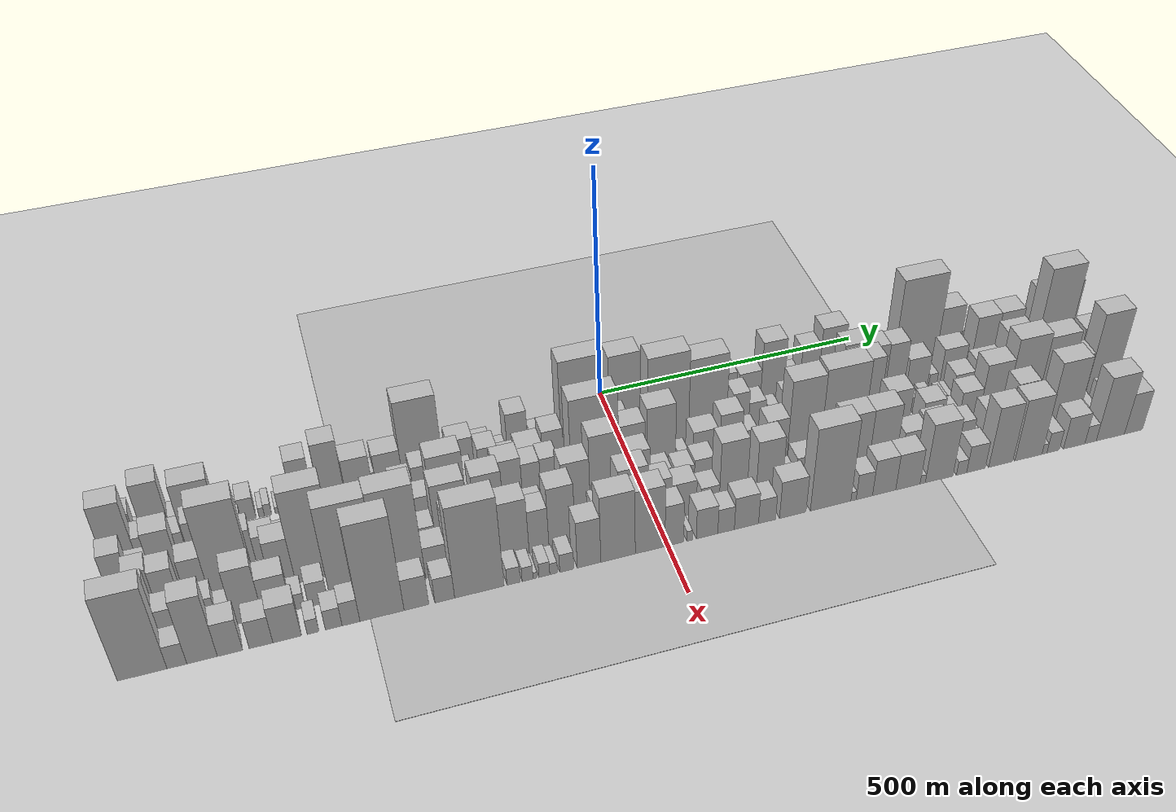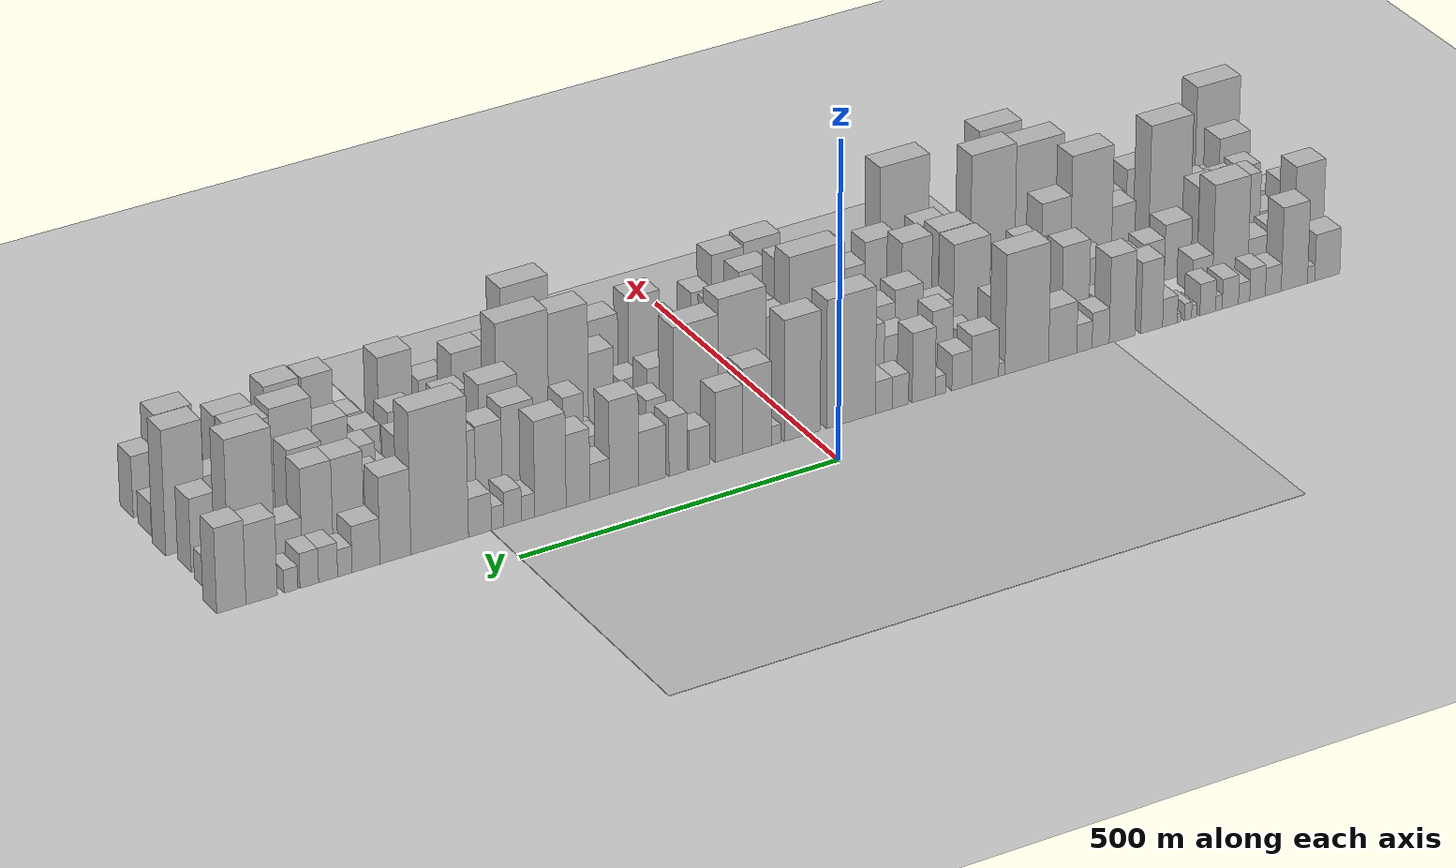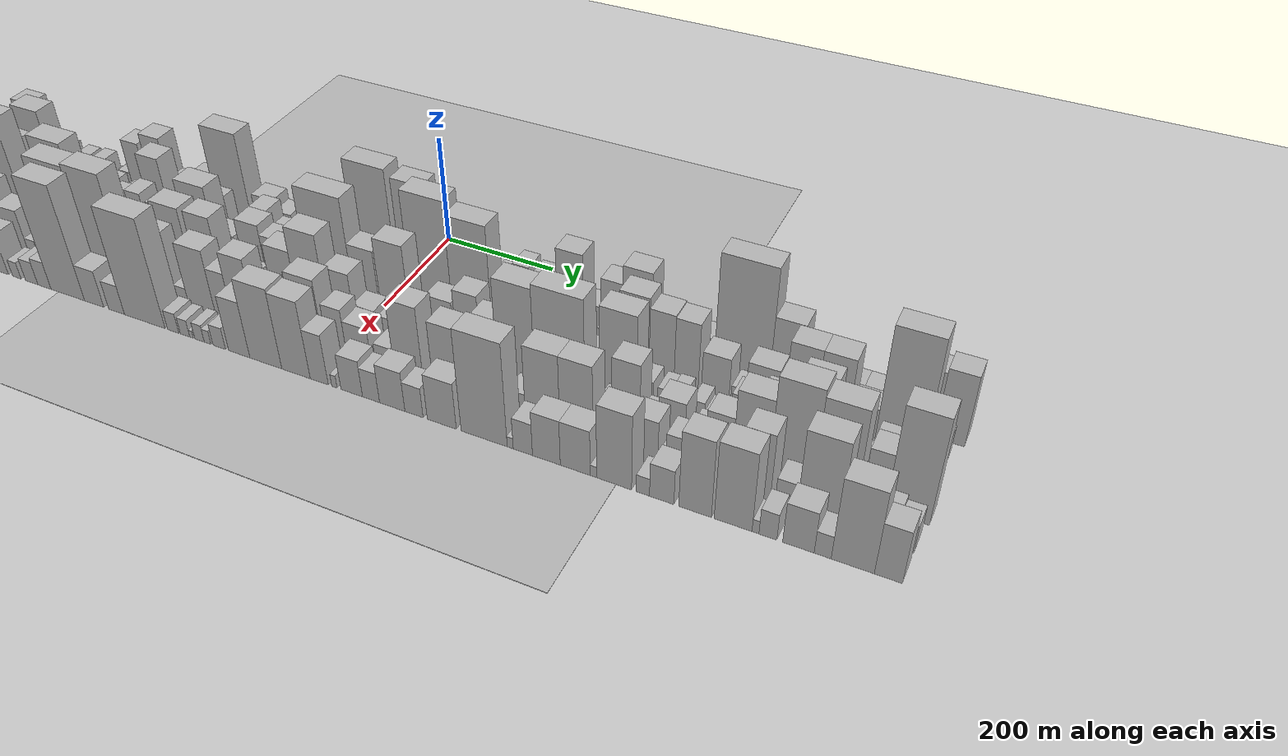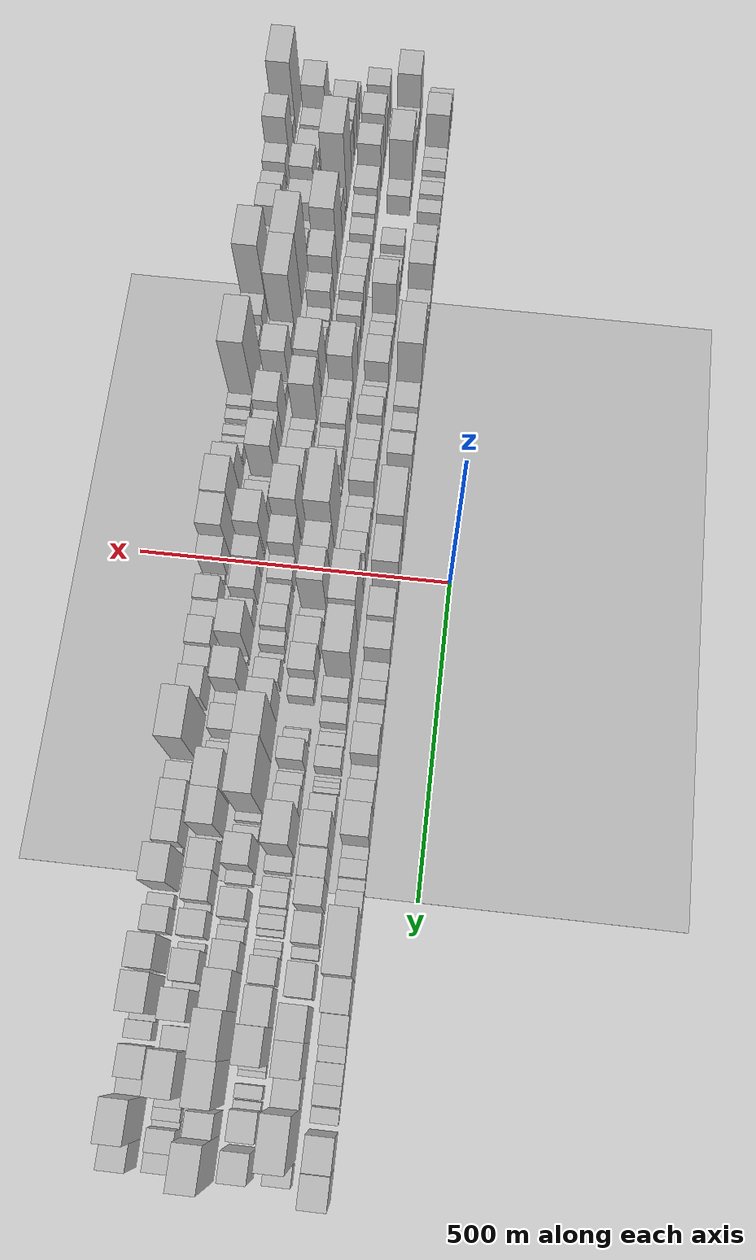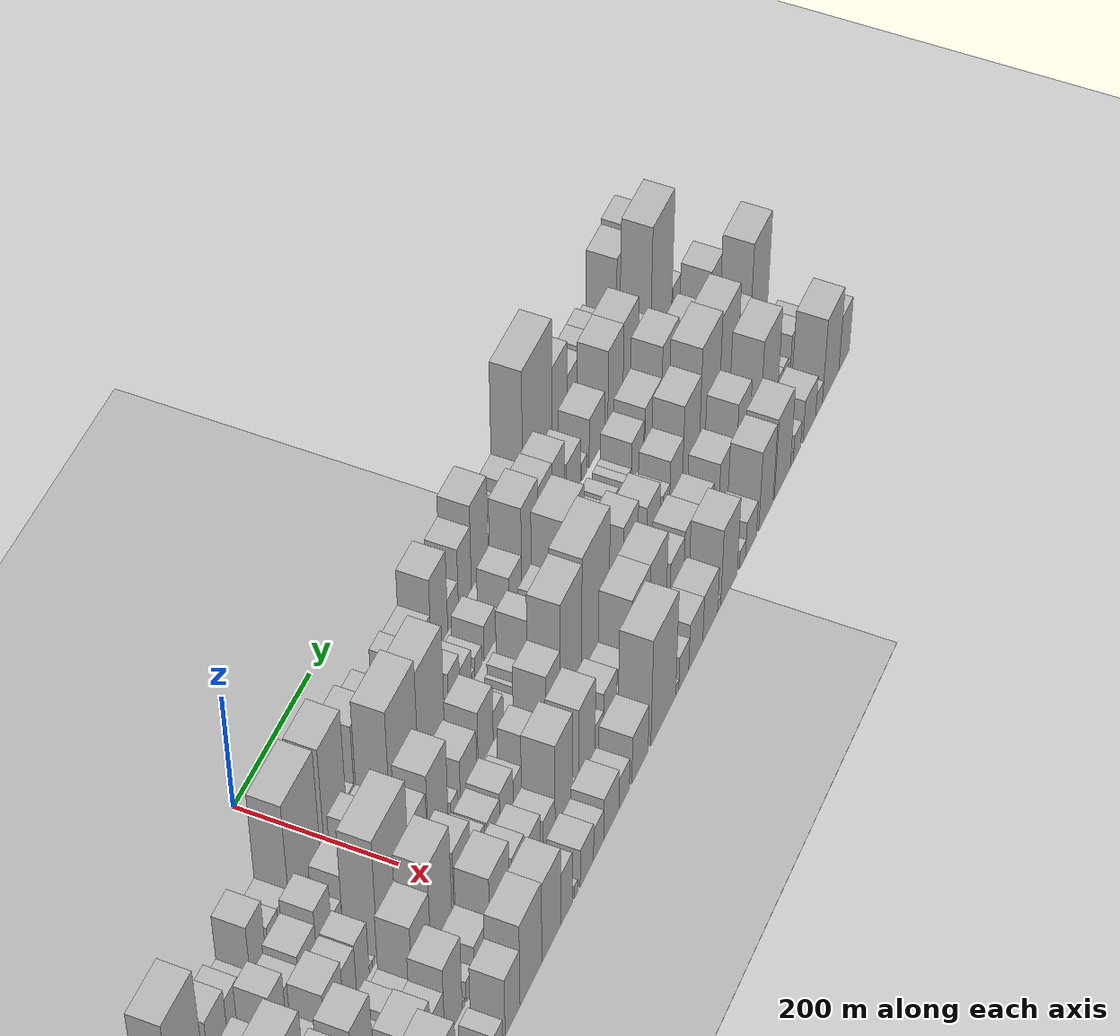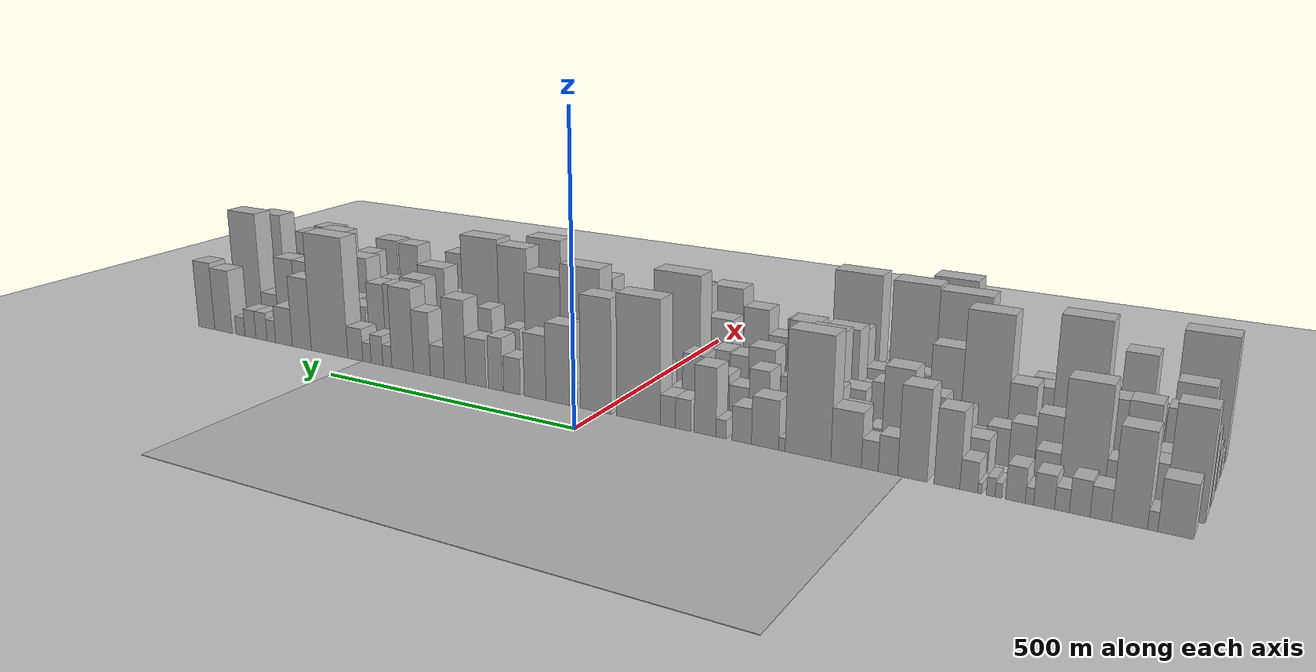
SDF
<?xml version="1.0" encoding="utf-8"?>

<sdf version="1.6">

   <world name="default">

      <gui fullscreen="0">

         <camera name="user_camera">

            <pose>-15 0 4.57585 0 0 0</pose>

            <view_controller>orbit</view_controller>

         </camera>

      </gui>

      <scene>

         <sky>

           <clouds>

             <speed>12</speed>

           </clouds>

         </sky>

         <ambient>0.4 0.4 0.4 1</ambient>

         <background>0.7 0.7 0.7 1</background>

         <shadows>1</shadows>

      </scene>

      <gravity>0 0 -9.8066</gravity>

      <magnetic_field>6e-06 2.3e-05 -4.2e-05</magnetic_field>

      <physics default="0" name="default_physics" type="ode">

         <ode>

            <solver>

               <type>quick</type>

               <iters>10</iters>

               <sor>1.0</sor>

               <use_dynamic_moi_rescaling>0</use_dynamic_moi_rescaling>

            </solver>

            <constraints>

               <cfm>0</cfm>

               <erp>0.2</erp>

               <contact_max_correcting_vel>100</contact_max_correcting_vel>

               <contact_surface_layer>0.001</contact_surface_layer>

            </constraints>

         </ode>

         <max_step_size>0.004</max_step_size>

         <real_time_factor>1</real_time_factor>

         <real_time_update_rate>250</real_time_update_rate>

      </physics>

      <light name="sun" type="directional">

         <cast_shadows>1</cast_shadows>

         <pose>0 0 10 0 0 0</pose>

         <diffuse>0.8 0.8 0.8 1</diffuse>

         <specular>0.2 0.2 0.2 1</specular>

         <attenuation>

            <range>1000</range>

            <constant>0.9</constant>

            <linear>0.01</linear>

            <quadratic>0.001</quadratic>

         </attenuation>

         <direction>-0.5 0.1 -0.9</direction>

      </light>

      <include>

         <name>ground_plane_1</name>

         <uri>model://HANNAS_ground_plane</uri>

         <pose>0 0 0  0 0 0</pose>

      </include>

      <include>

         <name>ground_plane_2</name>

         <uri>model://HANNAS_ground_plane</uri>

         <pose>100 0 0  0 0 0</pose>

      </include>

      <model name="building_1">

         <static>1</static>

         <pose frame="">100.0000 -861.5015 0 0.000000 0.000000 0.000000</pose>

         <link name="link">

            <pose frame="">0 0 37.50 0 0 0</pose>

            <collision name="collision">

               <geometry>

                  <box>

                     <size>40.0000 42.9970 75.0000</size>

                  </box>

               </geometry>

               <max_contacts>10</max_contacts>

               <surface>

                  <contact>

                     <ode/>

                  </contact>

                  <bounce/>

                  <friction>

                     <torsional>

                        <ode/>

                     </torsional>

                     <ode/>

                  </friction>

               </surface>

            </collision>

            <visual name="visual">

               <cast_shadows>0</cast_shadows>

               <geometry>

                  <box>

                     <size>40.0000 42.9970 75.0000</size>

                  </box>

               </geometry>

               <material>

                  <script>

                     <uri>model://HANNAS_wall/materials/scripts</uri>

                     <uri>model://HANNAS_wall/materials/textures</uri>

                     <name>vrc/HANNAS_wall</name>

                  </script>

               </material>

            </visual>

            <self_collide>0</self_collide>

            <enable_wind>0</enable_wind>

            <kinematic>0</kinematic>

         </link>

      </model>

      <model name="building_2">

         <static>1</static>

         <pose frame="">100.0000 -833.7153 0 0.000000 0.000000 0.000000</pose>

         <link name="link">

            <pose frame="">0 0 13.50 0 0 0</pose>

            <collision name="collision">

               <geometry>

                  <box>

                     <size>40.0000 12.5755 27.0000</size>

                  </box>

               </geometry>

               <max_contacts>10</max_contacts>

               <surface>

                  <contact>

                     <ode/>

                  </contact>

                  <bounce/>

                  <friction>

                     <torsional>

                        <ode/>

                     </torsional>

                     <ode/>

                  </friction>

               </surface>

            </collision>

            <visual name="visual">

               <cast_shadows>0</cast_shadows>

               <geometry>

                  <box>

                     <size>40.0000 12.5755 27.0000</size>

                  </box>

               </geometry>

               <material>

                  <script>

                     <uri>model://HANNAS_wall/materials/scripts</uri>

                     <uri>model://HANNAS_wall/materials/textures</uri>

                     <name>vrc/HANNAS_wall</name>

                  </script>

               </material>

            </visual>

            <self_collide>0</self_collide>

            <enable_wind>0</enable_wind>

            <kinematic>0</kinematic>

         </link>

      </model>

      <model name="building_3">

         <static>1</static>

         <pose frame="">100.0000 -804.9748 0 0.000000 0.000000 0.000000</pose>

         <link name="link">

            <pose frame="">0 0 67.50 0 0 0</pose>

            <collision name="collision">

               <geometry>

                  <box>

                     <size>40.0000 44.9055 135.0000</size>

                  </box>

               </geometry>

               <max_contacts>10</max_contacts>

               <surface>

                  <contact>

                     <ode/>

                  </contact>

                  <bounce/>

                  <friction>

                     <torsional>

                        <ode/>

                     </torsional>

                     <ode/>

                  </friction>

               </surface>

            </collision>

            <visual name="visual">

               <cast_shadows>0</cast_shadows>

               <geometry>

                  <box>

                     <size>40.0000 44.9055 135.0000</size>

                  </box>

               </geometry>

               <material>

                  <script>

                     <uri>model://HANNAS_wall/materials/scripts</uri>

                     <uri>model://HANNAS_wall/materials/textures</uri>

                     <name>vrc/HANNAS_wall</name>

                  </script>

               </material>

            </visual>

            <self_collide>0</self_collide>

            <enable_wind>0</enable_wind>

            <kinematic>0</kinematic>

         </link>

      </model>

      <model name="building_4">

         <static>1</static>

         <pose frame="">100.0000 -769.0350 0 0.000000 0.000000 0.000000</pose>

         <link name="link">

            <pose frame="">0 0 22.50 0 0 0</pose>

            <collision name="collision">

               <geometry>

                  <box>

                     <size>40.0000 26.9741 45.0000</size>

                  </box>

               </geometry>

               <max_contacts>10</max_contacts>

               <surface>

                  <contact>

                     <ode/>

                  </contact>

                  <bounce/>

                  <friction>

                     <torsional>

                        <ode/>

                     </torsional>

                     <ode/>

                  </friction>

               </surface>

            </collision>

            <visual name="visual">

               <cast_shadows>0</cast_shadows>

               <geometry>

                  <box>

                     <size>40.0000 26.9741 45.0000</size>

                  </box>

               </geometry>

               <material>

                  <script>

                     <uri>model://HANNAS_wall/materials/scripts</uri>

                     <uri>model://HANNAS_wall/materials/textures</uri>

                     <name>vrc/HANNAS_wall</name>

                  </script>

               </material>

            </visual>

            <self_collide>0</self_collide>

            <enable_wind>0</enable_wind>

            <kinematic>0</kinematic>

         </link>

      </model>

      <model name="building_5">

         <static>1</static>

         <pose frame="">100.0000 -742.2721 0 0.000000 0.000000 0.000000</pose>

         <link name="link">

            <pose frame="">0 0 25.50 0 0 0</pose>

            <collision name="collision">

               <geometry>

                  <box>

                     <size>40.0000 26.5517 51.0000</size>

                  </box>

               </geometry>

               <max_contacts>10</max_contacts>

               <surface>

                  <contact>

                     <ode/>

                  </contact>

                  <bounce/>

                  <friction>

                     <torsional>

                        <ode/>

                     </torsional>

                     <ode/>

                  </friction>

               </surface>

            </collision>

            <visual name="visual">

               <cast_shadows>0</cast_shadows>

               <geometry>

                  <box>

                     <size>40.0000 26.5517 51.0000</size>

                  </box>

               </geometry>

               <material>

                  <script>

                     <uri>model://HANNAS_wall/materials/scripts</uri>

                     <uri>model://HANNAS_wall/materials/textures</uri>

                     <name>vrc/HANNAS_wall</name>

                  </script>

               </material>

            </visual>

            <self_collide>0</self_collide>

            <enable_wind>0</enable_wind>

            <kinematic>0</kinematic>

         </link>

      </model>

      <model name="building_6">

         <static>1</static>

         <pose frame="">100.0000 -719.4111 0 0.000000 0.000000 0.000000</pose>

         <link name="link">

            <pose frame="">0 0 16.50 0 0 0</pose>

            <collision name="collision">

               <geometry>

                  <box>

                     <size>40.0000 19.1703 33.0000</size>

                  </box>

               </geometry>

               <max_contacts>10</max_contacts>

               <surface>

                  <contact>

                     <ode/>

                  </contact>

                  <bounce/>

                  <friction>

                     <torsional>

                        <ode/>

                     </torsional>

                     <ode/>

                  </friction>

               </surface>

            </collision>

            <visual name="visual">

               <cast_shadows>0</cast_shadows>

               <geometry>

                  <box>

                     <size>40.0000 19.1703 33.0000</size>

                  </box>

               </geometry>

               <material>

                  <script>

                     <uri>model://HANNAS_wall/materials/scripts</uri>

                     <uri>model://HANNAS_wall/materials/textures</uri>

                     <name>vrc/HANNAS_wall</name>

                  </script>

               </material>

            </visual>

            <self_collide>0</self_collide>

            <enable_wind>0</enable_wind>

            <kinematic>0</kinematic>

         </link>

      </model>

      <model name="building_7">

         <static>1</static>

         <pose frame="">100.0000 -696.0575 0 0.000000 0.000000 0.000000</pose>

         <link name="link">

            <pose frame="">0 0 24.00 0 0 0</pose>

            <collision name="collision">

               <geometry>

                  <box>

                     <size>40.0000 27.5370 48.0000</size>

                  </box>

               </geometry>

               <max_contacts>10</max_contacts>

               <surface>

                  <contact>

                     <ode/>

                  </contact>

                  <bounce/>

                  <friction>

                     <torsional>

                        <ode/>

                     </torsional>

                     <ode/>

                  </friction>

               </surface>

            </collision>

            <visual name="visual">

               <cast_shadows>0</cast_shadows>

               <geometry>

                  <box>

                     <size>40.0000 27.5370 48.0000</size>

                  </box>

               </geometry>

               <material>

                  <script>

                     <uri>model://HANNAS_wall/materials/scripts</uri>

                     <uri>model://HANNAS_wall/materials/textures</uri>

                     <name>vrc/HANNAS_wall</name>

                  </script>

               </material>

            </visual>

            <self_collide>0</self_collide>

            <enable_wind>0</enable_wind>

            <kinematic>0</kinematic>

         </link>

      </model>

      <model name="building_8">

         <static>1</static>

         <pose frame="">100.0000 -676.7047 0 0.000000 0.000000 0.000000</pose>

         <link name="link">

            <pose frame="">0 0 12.00 0 0 0</pose>

            <collision name="collision">

               <geometry>

                  <box>

                     <size>40.0000 11.1686 24.0000</size>

                  </box>

               </geometry>

               <max_contacts>10</max_contacts>

               <surface>

                  <contact>

                     <ode/>

                  </contact>

                  <bounce/>

                  <friction>

                     <torsional>

                        <ode/>

                     </torsional>

                     <ode/>

                  </friction>

               </surface>

            </collision>

            <visual name="visual">

               <cast_shadows>0</cast_shadows>

               <geometry>

                  <box>

                     <size>40.0000 11.1686 24.0000</size>

                  </box>

               </geometry>

               <material>

                  <script>

                     <uri>model://HANNAS_wall/materials/scripts</uri>

                     <uri>model://HANNAS_wall/materials/textures</uri>

                     <name>vrc/HANNAS_wall</name>

                  </script>

               </material>

            </visual>

            <self_collide>0</self_collide>

            <enable_wind>0</enable_wind>

            <kinematic>0</kinematic>

         </link>

      </model>

      <model name="building_9">

         <static>1</static>

         <pose frame="">100.0000 -657.8002 0 0.000000 0.000000 0.000000</pose>

         <link name="link">

            <pose frame="">0 0 25.50 0 0 0</pose>

            <collision name="collision">

               <geometry>

                  <box>

                     <size>40.0000 26.6404 51.0000</size>

                  </box>

               </geometry>

               <max_contacts>10</max_contacts>

               <surface>

                  <contact>

                     <ode/>

                  </contact>

                  <bounce/>

                  <friction>

                     <torsional>

                        <ode/>

                     </torsional>

                     <ode/>

                  </friction>

               </surface>

            </collision>

            <visual name="visual">

               <cast_shadows>0</cast_shadows>

               <geometry>

                  <box>

                     <size>40.0000 26.6404 51.0000</size>

                  </box>

               </geometry>

               <material>

                  <script>

                     <uri>model://HANNAS_wall/materials/scripts</uri>

                     <uri>model://HANNAS_wall/materials/textures</uri>

                     <name>vrc/HANNAS_wall</name>

                  </script>

               </material>

            </visual>

            <self_collide>0</self_collide>

            <enable_wind>0</enable_wind>

            <kinematic>0</kinematic>

         </link>

      </model>

      <model name="building_10">

         <static>1</static>

         <pose frame="">100.0000 -634.9543 0 0.000000 0.000000 0.000000</pose>

         <link name="link">

            <pose frame="">0 0 10.50 0 0 0</pose>

            <collision name="collision">

               <geometry>

                  <box>

                     <size>40.0000 9.0513 21.0000</size>

                  </box>

               </geometry>

               <max_contacts>10</max_contacts>

               <surface>

                  <contact>

                     <ode/>

                  </contact>

                  <bounce/>

                  <friction>

                     <torsional>

                        <ode/>

                     </torsional>

                     <ode/>

                  </friction>

               </surface>

            </collision>

            <visual name="visual">

               <cast_shadows>0</cast_shadows>

               <geometry>

                  <box>

                     <size>40.0000 9.0513 21.0000</size>

                  </box>

               </geometry>

               <material>

                  <script>

                     <uri>model://HANNAS_wall/materials/scripts</uri>

                     <uri>model://HANNAS_wall/materials/textures</uri>

                     <name>vrc/HANNAS_wall</name>

                  </script>

               </material>

            </visual>

            <self_collide>0</self_collide>

            <enable_wind>0</enable_wind>

            <kinematic>0</kinematic>

         </link>

      </model>

      <model name="building_11">

         <static>1</static>

         <pose frame="">100.0000 -624.3979 0 0.000000 0.000000 0.000000</pose>

         <link name="link">

            <pose frame="">0 0 13.50 0 0 0</pose>

            <collision name="collision">

               <geometry>

                  <box>

                     <size>40.0000 12.0615 27.0000</size>

                  </box>

               </geometry>

               <max_contacts>10</max_contacts>

               <surface>

                  <contact>

                     <ode/>

                  </contact>

                  <bounce/>

                  <friction>

                     <torsional>

                        <ode/>

                     </torsional>

                     <ode/>

                  </friction>

               </surface>

            </collision>

            <visual name="visual">

               <cast_shadows>0</cast_shadows>

               <geometry>

                  <box>

                     <size>40.0000 12.0615 27.0000</size>

                  </box>

               </geometry>

               <material>

                  <script>

                     <uri>model://HANNAS_wall/materials/scripts</uri>

                     <uri>model://HANNAS_wall/materials/textures</uri>

                     <name>vrc/HANNAS_wall</name>

                  </script>

               </material>

            </visual>

            <self_collide>0</self_collide>

            <enable_wind>0</enable_wind>

            <kinematic>0</kinematic>

         </link>

      </model>

      <model name="building_12">

         <static>1</static>

         <pose frame="">100.0000 -609.3551 0 0.000000 0.000000 0.000000</pose>

         <link name="link">

            <pose frame="">0 0 7.50 0 0 0</pose>

            <collision name="collision">

               <geometry>

                  <box>

                     <size>40.0000 6.0242 15.0000</size>

                  </box>

               </geometry>

               <max_contacts>10</max_contacts>

               <surface>

                  <contact>

                     <ode/>

                  </contact>

                  <bounce/>

                  <friction>

                     <torsional>

                        <ode/>

                     </torsional>

                     <ode/>

                  </friction>

               </surface>

            </collision>

            <visual name="visual">

               <cast_shadows>0</cast_shadows>

               <geometry>

                  <box>

                     <size>40.0000 6.0242 15.0000</size>

                  </box>

               </geometry>

               <material>

                  <script>

                     <uri>model://HANNAS_wall/materials/scripts</uri>

                     <uri>model://HANNAS_wall/materials/textures</uri>

                     <name>vrc/HANNAS_wall</name>

                  </script>

               </material>

            </visual>

            <self_collide>0</self_collide>

            <enable_wind>0</enable_wind>

            <kinematic>0</kinematic>

         </link>

      </model>

      <model name="building_13">

         <static>1</static>

         <pose frame="">100.0000 -593.9418 0 0.000000 0.000000 0.000000</pose>

         <link name="link">

            <pose frame="">0 0 22.50 0 0 0</pose>

            <collision name="collision">

               <geometry>

                  <box>

                     <size>40.0000 24.8023 45.0000</size>

                  </box>

               </geometry>

               <max_contacts>10</max_contacts>

               <surface>

                  <contact>

                     <ode/>

                  </contact>

                  <bounce/>

                  <friction>

                     <torsional>

                        <ode/>

                     </torsional>

                     <ode/>

                  </friction>

               </surface>

            </collision>

            <visual name="visual">

               <cast_shadows>0</cast_shadows>

               <geometry>

                  <box>

                     <size>40.0000 24.8023 45.0000</size>

                  </box>

               </geometry>

               <material>

                  <script>

                     <uri>model://HANNAS_wall/materials/scripts</uri>

                     <uri>model://HANNAS_wall/materials/textures</uri>

                     <name>vrc/HANNAS_wall</name>

                  </script>

               </material>

            </visual>

            <self_collide>0</self_collide>

            <enable_wind>0</enable_wind>

            <kinematic>0</kinematic>

         </link>

      </model>

      <model name="building_14">

         <static>1</static>

         <pose frame="">100.0000 -563.2996 0 0.000000 0.000000 0.000000</pose>

         <link name="link">

            <pose frame="">0 0 57.00 0 0 0</pose>

            <collision name="collision">

               <geometry>

                  <box>

                     <size>40.0000 36.4821 114.0000</size>

                  </box>

               </geometry>

               <max_contacts>10</max_contacts>

               <surface>

                  <contact>

                     <ode/>

                  </contact>

                  <bounce/>

                  <friction>

                     <torsional>

                        <ode/>

                     </torsional>

                     <ode/>

                  </friction>

               </surface>

            </collision>

            <visual name="visual">

               <cast_shadows>0</cast_shadows>

               <geometry>

                  <box>

                     <size>40.0000 36.4821 114.0000</size>

                  </box>

               </geometry>

               <material>

                  <script>

                     <uri>model://HANNAS_wall/materials/scripts</uri>

                     <uri>model://HANNAS_wall/materials/textures</uri>

                     <name>vrc/HANNAS_wall</name>

                  </script>

               </material>

            </visual>

            <self_collide>0</self_collide>

            <enable_wind>0</enable_wind>

            <kinematic>0</kinematic>

         </link>

      </model>

      <model name="building_15">

         <static>1</static>

         <pose frame="">100.0000 -513.6216 0 0.000000 0.000000 0.000000</pose>

         <link name="link">

            <pose frame="">0 0 69.00 0 0 0</pose>

            <collision name="collision">

               <geometry>

                  <box>

                     <size>40.0000 42.8740 138.0000</size>

                  </box>

               </geometry>

               <max_contacts>10</max_contacts>

               <surface>

                  <contact>

                     <ode/>

                  </contact>

                  <bounce/>

                  <friction>

                     <torsional>

                        <ode/>

                     </torsional>

                     <ode/>

                  </friction>

               </surface>

            </collision>

            <visual name="visual">

               <cast_shadows>0</cast_shadows>

               <geometry>

                  <box>

                     <size>40.0000 42.8740 138.0000</size>

                  </box>

               </geometry>

               <material>

                  <script>

                     <uri>model://HANNAS_wall/materials/scripts</uri>

                     <uri>model://HANNAS_wall/materials/textures</uri>

                     <name>vrc/HANNAS_wall</name>

                  </script>

               </material>

            </visual>

            <self_collide>0</self_collide>

            <enable_wind>0</enable_wind>

            <kinematic>0</kinematic>

         </link>

      </model>

      <model name="building_16">

         <static>1</static>

         <pose frame="">100.0000 -477.8767 0 0.000000 0.000000 0.000000</pose>

         <link name="link">

            <pose frame="">0 0 28.50 0 0 0</pose>

            <collision name="collision">

               <geometry>

                  <box>

                     <size>40.0000 28.6157 57.0000</size>

                  </box>

               </geometry>

               <max_contacts>10</max_contacts>

               <surface>

                  <contact>

                     <ode/>

                  </contact>

                  <bounce/>

                  <friction>

                     <torsional>

                        <ode/>

                     </torsional>

                     <ode/>

                  </friction>

               </surface>

            </collision>

            <visual name="visual">

               <cast_shadows>0</cast_shadows>

               <geometry>

                  <box>

                     <size>40.0000 28.6157 57.0000</size>

                  </box>

               </geometry>

               <material>

                  <script>

                     <uri>model://HANNAS_wall/materials/scripts</uri>

                     <uri>model://HANNAS_wall/materials/textures</uri>

                     <name>vrc/HANNAS_wall</name>

                  </script>

               </material>

            </visual>

            <self_collide>0</self_collide>

            <enable_wind>0</enable_wind>

            <kinematic>0</kinematic>

         </link>

      </model>

      <model name="building_17">

         <static>1</static>

         <pose frame="">100.0000 -450.7603 0 0.000000 0.000000 0.000000</pose>

         <link name="link">

            <pose frame="">0 0 22.50 0 0 0</pose>

            <collision name="collision">

               <geometry>

                  <box>

                     <size>40.0000 25.6171 45.0000</size>

                  </box>

               </geometry>

               <max_contacts>10</max_contacts>

               <surface>

                  <contact>

                     <ode/>

                  </contact>

                  <bounce/>

                  <friction>

                     <torsional>

                        <ode/>

                     </torsional>

                     <ode/>

                  </friction>

               </surface>

            </collision>

            <visual name="visual">

               <cast_shadows>0</cast_shadows>

               <geometry>

                  <box>

                     <size>40.0000 25.6171 45.0000</size>

                  </box>

               </geometry>

               <material>

                  <script>

                     <uri>model://HANNAS_wall/materials/scripts</uri>

                     <uri>model://HANNAS_wall/materials/textures</uri>

                     <name>vrc/HANNAS_wall</name>

                  </script>

               </material>

            </visual>

            <self_collide>0</self_collide>

            <enable_wind>0</enable_wind>

            <kinematic>0</kinematic>

         </link>

      </model>

      <model name="building_18">

         <static>1</static>

         <pose frame="">100.0000 -414.6206 0 0.000000 0.000000 0.000000</pose>

         <link name="link">

            <pose frame="">0 0 42.00 0 0 0</pose>

            <collision name="collision">

               <geometry>

                  <box>

                     <size>40.0000 46.6623 84.0000</size>

                  </box>

               </geometry>

               <max_contacts>10</max_contacts>

               <surface>

                  <contact>

                     <ode/>

                  </contact>

                  <bounce/>

                  <friction>

                     <torsional>

                        <ode/>

                     </torsional>

                     <ode/>

                  </friction>

               </surface>

            </collision>

            <visual name="visual">

               <cast_shadows>0</cast_shadows>

               <geometry>

                  <box>

                     <size>40.0000 46.6623 84.0000</size>

                  </box>

               </geometry>

               <material>

                  <script>

                     <uri>model://HANNAS_wall/materials/scripts</uri>

                     <uri>model://HANNAS_wall/materials/textures</uri>

                     <name>vrc/HANNAS_wall</name>

                  </script>

               </material>

            </visual>

            <self_collide>0</self_collide>

            <enable_wind>0</enable_wind>

            <kinematic>0</kinematic>

         </link>

      </model>

      <model name="building_19">

         <static>1</static>

         <pose frame="">100.0000 -355.2714 0 0.000000 0.000000 0.000000</pose>

         <link name="link">

            <pose frame="">0 0 96.00 0 0 0</pose>

            <collision name="collision">

               <geometry>

                  <box>

                     <size>40.0000 72.0362 192.0000</size>

                  </box>

               </geometry>

               <max_contacts>10</max_contacts>

               <surface>

                  <contact>

                     <ode/>

                  </contact>

                  <bounce/>

                  <friction>

                     <torsional>

                        <ode/>

                     </torsional>

                     <ode/>

                  </friction>

               </surface>

            </collision>

            <visual name="visual">

               <cast_shadows>0</cast_shadows>

               <geometry>

                  <box>

                     <size>40.0000 72.0362 192.0000</size>

                  </box>

               </geometry>

               <material>

                  <script>

                     <uri>model://HANNAS_wall/materials/scripts</uri>

                     <uri>model://HANNAS_wall/materials/textures</uri>

                     <name>vrc/HANNAS_wall</name>

                  </script>

               </material>

            </visual>

            <self_collide>0</self_collide>

            <enable_wind>0</enable_wind>

            <kinematic>0</kinematic>

         </link>

      </model>

      <model name="building_20">

         <static>1</static>

         <pose frame="">100.0000 -314.0269 0 0.000000 0.000000 0.000000</pose>

         <link name="link">

            <pose frame="">0 0 10.50 0 0 0</pose>

            <collision name="collision">

               <geometry>

                  <box>

                     <size>40.0000 10.4528 21.0000</size>

                  </box>

               </geometry>

               <max_contacts>10</max_contacts>

               <surface>

                  <contact>

                     <ode/>

                  </contact>

                  <bounce/>

                  <friction>

                     <torsional>

                        <ode/>

                     </torsional>

                     <ode/>

                  </friction>

               </surface>

            </collision>

            <visual name="visual">

               <cast_shadows>0</cast_shadows>

               <geometry>

                  <box>

                     <size>40.0000 10.4528 21.0000</size>

                  </box>

               </geometry>

               <material>

                  <script>

                     <uri>model://HANNAS_wall/materials/scripts</uri>

                     <uri>model://HANNAS_wall/materials/textures</uri>

                     <name>vrc/HANNAS_wall</name>

                  </script>

               </material>

            </visual>

            <self_collide>0</self_collide>

            <enable_wind>0</enable_wind>

            <kinematic>0</kinematic>

         </link>

      </model>

      <model name="building_21">

         <static>1</static>

         <pose frame="">100.0000 -286.6192 0 0.000000 0.000000 0.000000</pose>

         <link name="link">

            <pose frame="">0 0 39.00 0 0 0</pose>

            <collision name="collision">

               <geometry>

                  <box>

                     <size>40.0000 44.3624 78.0000</size>

                  </box>

               </geometry>

               <max_contacts>10</max_contacts>

               <surface>

                  <contact>

                     <ode/>

                  </contact>

                  <bounce/>

                  <friction>

                     <torsional>

                        <ode/>

                     </torsional>

                     <ode/>

                  </friction>

               </surface>

            </collision>

            <visual name="visual">

               <cast_shadows>0</cast_shadows>

               <geometry>

                  <box>

                     <size>40.0000 44.3624 78.0000</size>

                  </box>

               </geometry>

               <material>

                  <script>

                     <uri>model://HANNAS_wall/materials/scripts</uri>

                     <uri>model://HANNAS_wall/materials/textures</uri>

                     <name>vrc/HANNAS_wall</name>

                  </script>

               </material>

            </visual>

            <self_collide>0</self_collide>

            <enable_wind>0</enable_wind>

            <kinematic>0</kinematic>

         </link>

      </model>

      <model name="building_22">

         <static>1</static>

         <pose frame="">100.0000 -248.2549 0 0.000000 0.000000 0.000000</pose>

         <link name="link">

            <pose frame="">0 0 28.50 0 0 0</pose>

            <collision name="collision">

               <geometry>

                  <box>

                     <size>40.0000 32.3662 57.0000</size>

                  </box>

               </geometry>

               <max_contacts>10</max_contacts>

               <surface>

                  <contact>

                     <ode/>

                  </contact>

                  <bounce/>

                  <friction>

                     <torsional>

                        <ode/>

                     </torsional>

                     <ode/>

                  </friction>

               </surface>

            </collision>

            <visual name="visual">

               <cast_shadows>0</cast_shadows>

               <geometry>

                  <box>

                     <size>40.0000 32.3662 57.0000</size>

                  </box>

               </geometry>

               <material>

                  <script>

                     <uri>model://HANNAS_wall/materials/scripts</uri>

                     <uri>model://HANNAS_wall/materials/textures</uri>

                     <name>vrc/HANNAS_wall</name>

                  </script>

               </material>

            </visual>

            <self_collide>0</self_collide>

            <enable_wind>0</enable_wind>

            <kinematic>0</kinematic>

         </link>

      </model>

      <model name="building_23">

         <static>1</static>

         <pose frame="">100.0000 -213.4793 0 0.000000 0.000000 0.000000</pose>

         <link name="link">

            <pose frame="">0 0 15.00 0 0 0</pose>

            <collision name="collision">

               <geometry>

                  <box>

                     <size>40.0000 17.1850 30.0000</size>

                  </box>

               </geometry>

               <max_contacts>10</max_contacts>

               <surface>

                  <contact>

                     <ode/>

                  </contact>

                  <bounce/>

                  <friction>

                     <torsional>

                        <ode/>

                     </torsional>

                     <ode/>

                  </friction>

               </surface>

            </collision>

            <visual name="visual">

               <cast_shadows>0</cast_shadows>

               <geometry>

                  <box>

                     <size>40.0000 17.1850 30.0000</size>

                  </box>

               </geometry>

               <material>

                  <script>

                     <uri>model://HANNAS_wall/materials/scripts</uri>

                     <uri>model://HANNAS_wall/materials/textures</uri>

                     <name>vrc/HANNAS_wall</name>

                  </script>

               </material>

            </visual>

            <self_collide>0</self_collide>

            <enable_wind>0</enable_wind>

            <kinematic>0</kinematic>

         </link>

      </model>

      <model name="building_24">

         <static>1</static>

         <pose frame="">100.0000 -186.1850 0 0.000000 0.000000 0.000000</pose>

         <link name="link">

            <pose frame="">0 0 55.50 0 0 0</pose>

            <collision name="collision">

               <geometry>

                  <box>

                     <size>40.0000 37.4036 111.0000</size>

                  </box>

               </geometry>

               <max_contacts>10</max_contacts>

               <surface>

                  <contact>

                     <ode/>

                  </contact>

                  <bounce/>

                  <friction>

                     <torsional>

                        <ode/>

                     </torsional>

                     <ode/>

                  </friction>

               </surface>

            </collision>

            <visual name="visual">

               <cast_shadows>0</cast_shadows>

               <geometry>

                  <box>

                     <size>40.0000 37.4036 111.0000</size>

                  </box>

               </geometry>

               <material>

                  <script>

                     <uri>model://HANNAS_wall/materials/scripts</uri>

                     <uri>model://HANNAS_wall/materials/textures</uri>

                     <name>vrc/HANNAS_wall</name>

                  </script>

               </material>

            </visual>

            <self_collide>0</self_collide>

            <enable_wind>0</enable_wind>

            <kinematic>0</kinematic>

         </link>

      </model>

      <model name="building_25">

         <static>1</static>

         <pose frame="">100.0000 -148.1943 0 0.000000 0.000000 0.000000</pose>

         <link name="link">

            <pose frame="">0 0 25.50 0 0 0</pose>

            <collision name="collision">

               <geometry>

                  <box>

                     <size>40.0000 26.5778 51.0000</size>

                  </box>

               </geometry>

               <max_contacts>10</max_contacts>

               <surface>

                  <contact>

                     <ode/>

                  </contact>

                  <bounce/>

                  <friction>

                     <torsional>

                        <ode/>

                     </torsional>

                     <ode/>

                  </friction>

               </surface>

            </collision>

            <visual name="visual">

               <cast_shadows>0</cast_shadows>

               <geometry>

                  <box>

                     <size>40.0000 26.5778 51.0000</size>

                  </box>

               </geometry>

               <material>

                  <script>

                     <uri>model://HANNAS_wall/materials/scripts</uri>

                     <uri>model://HANNAS_wall/materials/textures</uri>

                     <name>vrc/HANNAS_wall</name>

                  </script>

               </material>

            </visual>

            <self_collide>0</self_collide>

            <enable_wind>0</enable_wind>

            <kinematic>0</kinematic>

         </link>

      </model>

      <model name="building_26">

         <static>1</static>

         <pose frame="">100.0000 -121.1936 0 0.000000 0.000000 0.000000</pose>

         <link name="link">

            <pose frame="">0 0 25.50 0 0 0</pose>

            <collision name="collision">

               <geometry>

                  <box>

                     <size>40.0000 27.4237 51.0000</size>

                  </box>

               </geometry>

               <max_contacts>10</max_contacts>

               <surface>

                  <contact>

                     <ode/>

                  </contact>

                  <bounce/>

                  <friction>

                     <torsional>

                        <ode/>

                     </torsional>

                     <ode/>

                  </friction>

               </surface>

            </collision>

            <visual name="visual">

               <cast_shadows>0</cast_shadows>

               <geometry>

                  <box>

                     <size>40.0000 27.4237 51.0000</size>

                  </box>

               </geometry>

               <material>

                  <script>

                     <uri>model://HANNAS_wall/materials/scripts</uri>

                     <uri>model://HANNAS_wall/materials/textures</uri>

                     <name>vrc/HANNAS_wall</name>

                  </script>

               </material>

            </visual>

            <self_collide>0</self_collide>

            <enable_wind>0</enable_wind>

            <kinematic>0</kinematic>

         </link>

      </model>

      <model name="building_27">

         <static>1</static>

         <pose frame="">100.0000 -68.1438 0 0.000000 0.000000 0.000000</pose>

         <link name="link">

            <pose frame="">0 0 102.00 0 0 0</pose>

            <collision name="collision">

               <geometry>

                  <box>

                     <size>40.0000 78.6760 204.0000</size>

                  </box>

               </geometry>

               <max_contacts>10</max_contacts>

               <surface>

                  <contact>

                     <ode/>

                  </contact>

                  <bounce/>

                  <friction>

                     <torsional>

                        <ode/>

                     </torsional>

                     <ode/>

                  </friction>

               </surface>

            </collision>

            <visual name="visual">

               <cast_shadows>0</cast_shadows>

               <geometry>

                  <box>

                     <size>40.0000 78.6760 204.0000</size>

                  </box>

               </geometry>

               <material>

                  <script>

                     <uri>model://HANNAS_wall/materials/scripts</uri>

                     <uri>model://HANNAS_wall/materials/textures</uri>

                     <name>vrc/HANNAS_wall</name>

                  </script>

               </material>

            </visual>

            <self_collide>0</self_collide>

            <enable_wind>0</enable_wind>

            <kinematic>0</kinematic>

         </link>

      </model>

      <model name="building_28">

         <static>1</static>

         <pose frame="">100.0000 10.0778 0 0.000000 0.000000 0.000000</pose>

         <link name="link">

            <pose frame="">0 0 96.00 0 0 0</pose>

            <collision name="collision">

               <geometry>

                  <box>

                     <size>40.0000 57.7671 192.0000</size>

                  </box>

               </geometry>

               <max_contacts>10</max_contacts>

               <surface>

                  <contact>

                     <ode/>

                  </contact>

                  <bounce/>

                  <friction>

                     <torsional>

                        <ode/>

                     </torsional>

                     <ode/>

                  </friction>

               </surface>

            </collision>

            <visual name="visual">

               <cast_shadows>0</cast_shadows>

               <geometry>

                  <box>

                     <size>40.0000 57.7671 192.0000</size>

                  </box>

               </geometry>

               <material>

                  <script>

                     <uri>model://HANNAS_wall/materials/scripts</uri>

                     <uri>model://HANNAS_wall/materials/textures</uri>

                     <name>vrc/HANNAS_wall</name>

                  </script>

               </material>

            </visual>

            <self_collide>0</self_collide>

            <enable_wind>0</enable_wind>

            <kinematic>0</kinematic>

         </link>

      </model>

      <model name="building_29">

         <static>1</static>

         <pose frame="">100.0000 52.5139 0 0.000000 0.000000 0.000000</pose>

         <link name="link">

            <pose frame="">0 0 15.00 0 0 0</pose>

            <collision name="collision">

               <geometry>

                  <box>

                     <size>40.0000 15.1052 30.0000</size>

                  </box>

               </geometry>

               <max_contacts>10</max_contacts>

               <surface>

                  <contact>

                     <ode/>

                  </contact>

                  <bounce/>

                  <friction>

                     <torsional>

                        <ode/>

                     </torsional>

                     <ode/>

                  </friction>

               </surface>

            </collision>

            <visual name="visual">

               <cast_shadows>0</cast_shadows>

               <geometry>

                  <box>

                     <size>40.0000 15.1052 30.0000</size>

                  </box>

               </geometry>

               <material>

                  <script>

                     <uri>model://HANNAS_wall/materials/scripts</uri>

                     <uri>model://HANNAS_wall/materials/textures</uri>

                     <name>vrc/HANNAS_wall</name>

                  </script>

               </material>

            </visual>

            <self_collide>0</self_collide>

            <enable_wind>0</enable_wind>

            <kinematic>0</kinematic>

         </link>

      </model>

      <model name="building_30">

         <static>1</static>

         <pose frame="">100.0000 83.0617 0 0.000000 0.000000 0.000000</pose>

         <link name="link">

            <pose frame="">0 0 67.50 0 0 0</pose>

            <collision name="collision">

               <geometry>

                  <box>

                     <size>40.0000 45.9904 135.0000</size>

                  </box>

               </geometry>

               <max_contacts>10</max_contacts>

               <surface>

                  <contact>

                     <ode/>

                  </contact>

                  <bounce/>

                  <friction>

                     <torsional>

                        <ode/>

                     </torsional>

                     <ode/>

                  </friction>

               </surface>

            </collision>

            <visual name="visual">

               <cast_shadows>0</cast_shadows>

               <geometry>

                  <box>

                     <size>40.0000 45.9904 135.0000</size>

                  </box>

               </geometry>

               <material>

                  <script>

                     <uri>model://HANNAS_wall/materials/scripts</uri>

                     <uri>model://HANNAS_wall/materials/textures</uri>

                     <name>vrc/HANNAS_wall</name>

                  </script>

               </material>

            </visual>

            <self_collide>0</self_collide>

            <enable_wind>0</enable_wind>

            <kinematic>0</kinematic>

         </link>

      </model>

      <model name="building_31">

         <static>1</static>

         <pose frame="">100.0000 127.6087 0 0.000000 0.000000 0.000000</pose>

         <link name="link">

            <pose frame="">0 0 55.50 0 0 0</pose>

            <collision name="collision">

               <geometry>

                  <box>

                     <size>40.0000 43.1036 111.0000</size>

                  </box>

               </geometry>

               <max_contacts>10</max_contacts>

               <surface>

                  <contact>

                     <ode/>

                  </contact>

                  <bounce/>

                  <friction>

                     <torsional>

                        <ode/>

                     </torsional>

                     <ode/>

                  </friction>

               </surface>

            </collision>

            <visual name="visual">

               <cast_shadows>0</cast_shadows>

               <geometry>

                  <box>

                     <size>40.0000 43.1036 111.0000</size>

                  </box>

               </geometry>

               <material>

                  <script>

                     <uri>model://HANNAS_wall/materials/scripts</uri>

                     <uri>model://HANNAS_wall/materials/textures</uri>

                     <name>vrc/HANNAS_wall</name>

                  </script>

               </material>

            </visual>

            <self_collide>0</self_collide>

            <enable_wind>0</enable_wind>

            <kinematic>0</kinematic>

         </link>

      </model>

      <model name="building_32">

         <static>1</static>

         <pose frame="">100.0000 173.8281 0 0.000000 0.000000 0.000000</pose>

         <link name="link">

            <pose frame="">0 0 31.50 0 0 0</pose>

            <collision name="collision">

               <geometry>

                  <box>

                     <size>40.0000 33.3352 63.0000</size>

                  </box>

               </geometry>

               <max_contacts>10</max_contacts>

               <surface>

                  <contact>

                     <ode/>

                  </contact>

                  <bounce/>

                  <friction>

                     <torsional>

                        <ode/>

                     </torsional>

                     <ode/>

                  </friction>

               </surface>

            </collision>

            <visual name="visual">

               <cast_shadows>0</cast_shadows>

               <geometry>

                  <box>

                     <size>40.0000 33.3352 63.0000</size>

                  </box>

               </geometry>

               <material>

                  <script>

                     <uri>model://HANNAS_wall/materials/scripts</uri>

                     <uri>model://HANNAS_wall/materials/textures</uri>

                     <name>vrc/HANNAS_wall</name>

                  </script>

               </material>

            </visual>

            <self_collide>0</self_collide>

            <enable_wind>0</enable_wind>

            <kinematic>0</kinematic>

         </link>

      </model>

      <model name="building_33">

         <static>1</static>

         <pose frame="">100.0000 207.8353 0 0.000000 0.000000 0.000000</pose>

         <link name="link">

            <pose frame="">0 0 46.50 0 0 0</pose>

            <collision name="collision">

               <geometry>

                  <box>

                     <size>40.0000 28.6792 93.0000</size>

                  </box>

               </geometry>

               <max_contacts>10</max_contacts>

               <surface>

                  <contact>

                     <ode/>

                  </contact>

                  <bounce/>

                  <friction>

                     <torsional>

                        <ode/>

                     </torsional>

                     <ode/>

                  </friction>

               </surface>

            </collision>

            <visual name="visual">

               <cast_shadows>0</cast_shadows>

               <geometry>

                  <box>

                     <size>40.0000 28.6792 93.0000</size>

                  </box>

               </geometry>

               <material>

                  <script>

                     <uri>model://HANNAS_wall/materials/scripts</uri>

                     <uri>model://HANNAS_wall/materials/textures</uri>

                     <name>vrc/HANNAS_wall</name>

                  </script>

               </material>

            </visual>

            <self_collide>0</self_collide>

            <enable_wind>0</enable_wind>

            <kinematic>0</kinematic>

         </link>

      </model>

      <model name="building_34">

         <static>1</static>

         <pose frame="">100.0000 248.5474 0 0.000000 0.000000 0.000000</pose>

         <link name="link">

            <pose frame="">0 0 42.00 0 0 0</pose>

            <collision name="collision">

               <geometry>

                  <box>

                     <size>40.0000 42.7449 84.0000</size>

                  </box>

               </geometry>

               <max_contacts>10</max_contacts>

               <surface>

                  <contact>

                     <ode/>

                  </contact>

                  <bounce/>

                  <friction>

                     <torsional>

                        <ode/>

                     </torsional>

                     <ode/>

                  </friction>

               </surface>

            </collision>

            <visual name="visual">

               <cast_shadows>0</cast_shadows>

               <geometry>

                  <box>

                     <size>40.0000 42.7449 84.0000</size>

                  </box>

               </geometry>

               <material>

                  <script>

                     <uri>model://HANNAS_wall/materials/scripts</uri>

                     <uri>model://HANNAS_wall/materials/textures</uri>

                     <name>vrc/HANNAS_wall</name>

                  </script>

               </material>

            </visual>

            <self_collide>0</self_collide>

            <enable_wind>0</enable_wind>

            <kinematic>0</kinematic>

         </link>

      </model>

      <model name="building_35">

         <static>1</static>

         <pose frame="">100.0000 292.8291 0 0.000000 0.000000 0.000000</pose>

         <link name="link">

            <pose frame="">0 0 73.50 0 0 0</pose>

            <collision name="collision">

               <geometry>

                  <box>

                     <size>40.0000 45.8186 147.0000</size>

                  </box>

               </geometry>

               <max_contacts>10</max_contacts>

               <surface>

                  <contact>

                     <ode/>

                  </contact>

                  <bounce/>

                  <friction>

                     <torsional>

                        <ode/>

                     </torsional>

                     <ode/>

                  </friction>

               </surface>

            </collision>

            <visual name="visual">

               <cast_shadows>0</cast_shadows>

               <geometry>

                  <box>

                     <size>40.0000 45.8186 147.0000</size>

                  </box>

               </geometry>

               <material>

                  <script>

                     <uri>model://HANNAS_wall/materials/scripts</uri>

                     <uri>model://HANNAS_wall/materials/textures</uri>

                     <name>vrc/HANNAS_wall</name>

                  </script>

               </material>

            </visual>

            <self_collide>0</self_collide>

            <enable_wind>0</enable_wind>

            <kinematic>0</kinematic>

         </link>

      </model>

      <model name="building_36">

         <static>1</static>

         <pose frame="">100.0000 330.9853 0 0.000000 0.000000 0.000000</pose>

         <link name="link">

            <pose frame="">0 0 28.50 0 0 0</pose>

            <collision name="collision">

               <geometry>

                  <box>

                     <size>40.0000 30.4937 57.0000</size>

                  </box>

               </geometry>

               <max_contacts>10</max_contacts>

               <surface>

                  <contact>

                     <ode/>

                  </contact>

                  <bounce/>

                  <friction>

                     <torsional>

                        <ode/>

                     </torsional>

                     <ode/>

                  </friction>

               </surface>

            </collision>

            <visual name="visual">

               <cast_shadows>0</cast_shadows>

               <geometry>

                  <box>

                     <size>40.0000 30.4937 57.0000</size>

                  </box>

               </geometry>

               <material>

                  <script>

                     <uri>model://HANNAS_wall/materials/scripts</uri>

                     <uri>model://HANNAS_wall/materials/textures</uri>

                     <name>vrc/HANNAS_wall</name>

                  </script>

               </material>

            </visual>

            <self_collide>0</self_collide>

            <enable_wind>0</enable_wind>

            <kinematic>0</kinematic>

         </link>

      </model>

      <model name="building_37">

         <static>1</static>

         <pose frame="">100.0000 364.7827 0 0.000000 0.000000 0.000000</pose>

         <link name="link">

            <pose frame="">0 0 57.00 0 0 0</pose>

            <collision name="collision">

               <geometry>

                  <box>

                     <size>40.0000 37.1011 114.0000</size>

                  </box>

               </geometry>

               <max_contacts>10</max_contacts>

               <surface>

                  <contact>

                     <ode/>

                  </contact>

                  <bounce/>

                  <friction>

                     <torsional>

                        <ode/>

                     </torsional>

                     <ode/>

                  </friction>

               </surface>

            </collision>

            <visual name="visual">

               <cast_shadows>0</cast_shadows>

               <geometry>

                  <box>

                     <size>40.0000 37.1011 114.0000</size>

                  </box>

               </geometry>

               <material>

                  <script>

                     <uri>model://HANNAS_wall/materials/scripts</uri>

                     <uri>model://HANNAS_wall/materials/textures</uri>

                     <name>vrc/HANNAS_wall</name>

                  </script>

               </material>

            </visual>

            <self_collide>0</self_collide>

            <enable_wind>0</enable_wind>

            <kinematic>0</kinematic>

         </link>

      </model>

      <model name="building_38">

         <static>1</static>

         <pose frame="">100.0000 407.6640 0 0.000000 0.000000 0.000000</pose>

         <link name="link">

            <pose frame="">0 0 75.00 0 0 0</pose>

            <collision name="collision">

               <geometry>

                  <box>

                     <size>40.0000 48.6615 150.0000</size>

                  </box>

               </geometry>

               <max_contacts>10</max_contacts>

               <surface>

                  <contact>

                     <ode/>

                  </contact>

                  <bounce/>

                  <friction>

                     <torsional>

                        <ode/>

                     </torsional>

                     <ode/>

                  </friction>

               </surface>

            </collision>

            <visual name="visual">

               <cast_shadows>0</cast_shadows>

               <geometry>

                  <box>

                     <size>40.0000 48.6615 150.0000</size>

                  </box>

               </geometry>

               <material>

                  <script>

                     <uri>model://HANNAS_wall/materials/scripts</uri>

                     <uri>model://HANNAS_wall/materials/textures</uri>

                     <name>vrc/HANNAS_wall</name>

                  </script>

               </material>

            </visual>

            <self_collide>0</self_collide>

            <enable_wind>0</enable_wind>

            <kinematic>0</kinematic>

         </link>

      </model>

      <model name="building_39">

         <static>1</static>

         <pose frame="">100.0000 442.3935 0 0.000000 0.000000 0.000000</pose>

         <link name="link">

            <pose frame="">0 0 19.50 0 0 0</pose>

            <collision name="collision">

               <geometry>

                  <box>

                     <size>40.0000 20.7976 39.0000</size>

                  </box>

               </geometry>

               <max_contacts>10</max_contacts>

               <surface>

                  <contact>

                     <ode/>

                  </contact>

                  <bounce/>

                  <friction>

                     <torsional>

                        <ode/>

                     </torsional>

                     <ode/>

                  </friction>

               </surface>

            </collision>

            <visual name="visual">

               <cast_shadows>0</cast_shadows>

               <geometry>

                  <box>

                     <size>40.0000 20.7976 39.0000</size>

                  </box>

               </geometry>

               <material>

                  <script>

                     <uri>model://HANNAS_wall/materials/scripts</uri>

                     <uri>model://HANNAS_wall/materials/textures</uri>

                     <name>vrc/HANNAS_wall</name>

                  </script>

               </material>

            </visual>

            <self_collide>0</self_collide>

            <enable_wind>0</enable_wind>

            <kinematic>0</kinematic>

         </link>

      </model>

      <model name="building_40">

         <static>1</static>

         <pose frame="">100.0000 466.3088 0 0.000000 0.000000 0.000000</pose>

         <link name="link">

            <pose frame="">0 0 27.00 0 0 0</pose>

            <collision name="collision">

               <geometry>

                  <box>

                     <size>40.0000 27.0331 54.0000</size>

                  </box>

               </geometry>

               <max_contacts>10</max_contacts>

               <surface>

                  <contact>

                     <ode/>

                  </contact>

                  <bounce/>

                  <friction>

                     <torsional>

                        <ode/>

                     </torsional>

                     <ode/>

                  </friction>

               </surface>

            </collision>

            <visual name="visual">

               <cast_shadows>0</cast_shadows>

               <geometry>

                  <box>

                     <size>40.0000 27.0331 54.0000</size>

                  </box>

               </geometry>

               <material>

                  <script>

                     <uri>model://HANNAS_wall/materials/scripts</uri>

                     <uri>model://HANNAS_wall/materials/textures</uri>

                     <name>vrc/HANNAS_wall</name>

                  </script>

               </material>

            </visual>

            <self_collide>0</self_collide>

            <enable_wind>0</enable_wind>

            <kinematic>0</kinematic>

         </link>

      </model>

      <model name="building_41">

         <static>1</static>

         <pose frame="">100.0000 489.4667 0 0.000000 0.000000 0.000000</pose>

         <link name="link">

            <pose frame="">0 0 18.00 0 0 0</pose>

            <collision name="collision">

               <geometry>

                  <box>

                     <size>40.0000 19.2828 36.0000</size>

                  </box>

               </geometry>

               <max_contacts>10</max_contacts>

               <surface>

                  <contact>

                     <ode/>

                  </contact>

                  <bounce/>

                  <friction>

                     <torsional>

                        <ode/>

                     </torsional>

                     <ode/>

                  </friction>

               </surface>

            </collision>

            <visual name="visual">

               <cast_shadows>0</cast_shadows>

               <geometry>

                  <box>

                     <size>40.0000 19.2828 36.0000</size>

                  </box>

               </geometry>

               <material>

                  <script>

                     <uri>model://HANNAS_wall/materials/scripts</uri>

                     <uri>model://HANNAS_wall/materials/textures</uri>

                     <name>vrc/HANNAS_wall</name>

                  </script>

               </material>

            </visual>

            <self_collide>0</self_collide>

            <enable_wind>0</enable_wind>

            <kinematic>0</kinematic>

         </link>

      </model>

      <model name="building_42">

         <static>1</static>

         <pose frame="">100.0000 516.7366 0 0.000000 0.000000 0.000000</pose>

         <link name="link">

            <pose frame="">0 0 30.00 0 0 0</pose>

            <collision name="collision">

               <geometry>

                  <box>

                     <size>40.0000 35.2570 60.0000</size>

                  </box>

               </geometry>

               <max_contacts>10</max_contacts>

               <surface>

                  <contact>

                     <ode/>

                  </contact>

                  <bounce/>

                  <friction>

                     <torsional>

                        <ode/>

                     </torsional>

                     <ode/>

                  </friction>

               </surface>

            </collision>

            <visual name="visual">

               <cast_shadows>0</cast_shadows>

               <geometry>

                  <box>

                     <size>40.0000 35.2570 60.0000</size>

                  </box>

               </geometry>

               <material>

                  <script>

                     <uri>model://HANNAS_wall/materials/scripts</uri>

                     <uri>model://HANNAS_wall/materials/textures</uri>

                     <name>vrc/HANNAS_wall</name>

                  </script>

               </material>

            </visual>

            <self_collide>0</self_collide>

            <enable_wind>0</enable_wind>

            <kinematic>0</kinematic>

         </link>

      </model>

      <model name="building_43">

         <static>1</static>

         <pose frame="">100.0000 578.4180 0 0.000000 0.000000 0.000000</pose>

         <link name="link">

            <pose frame="">0 0 111.00 0 0 0</pose>

            <collision name="collision">

               <geometry>

                  <box>

                     <size>40.0000 88.1057 222.0000</size>

                  </box>

               </geometry>

               <max_contacts>10</max_contacts>

               <surface>

                  <contact>

                     <ode/>

                  </contact>

                  <bounce/>

                  <friction>

                     <torsional>

                        <ode/>

                     </torsional>

                     <ode/>

                  </friction>

               </surface>

            </collision>

            <visual name="visual">

               <cast_shadows>0</cast_shadows>

               <geometry>

                  <box>

                     <size>40.0000 88.1057 222.0000</size>

                  </box>

               </geometry>

               <material>

                  <script>

                     <uri>model://HANNAS_wall/materials/scripts</uri>

                     <uri>model://HANNAS_wall/materials/textures</uri>

                     <name>vrc/HANNAS_wall</name>

                  </script>

               </material>

            </visual>

            <self_collide>0</self_collide>

            <enable_wind>0</enable_wind>

            <kinematic>0</kinematic>

         </link>

      </model>

      <model name="building_44">

         <static>1</static>

         <pose frame="">100.0000 646.0430 0 0.000000 0.000000 0.000000</pose>

         <link name="link">

            <pose frame="">0 0 67.50 0 0 0</pose>

            <collision name="collision">

               <geometry>

                  <box>

                     <size>40.0000 47.1443 135.0000</size>

                  </box>

               </geometry>

               <max_contacts>10</max_contacts>

               <surface>

                  <contact>

                     <ode/>

                  </contact>

                  <bounce/>

                  <friction>

                     <torsional>

                        <ode/>

                     </torsional>

                     <ode/>

                  </friction>

               </surface>

            </collision>

            <visual name="visual">

               <cast_shadows>0</cast_shadows>

               <geometry>

                  <box>

                     <size>40.0000 47.1443 135.0000</size>

                  </box>

               </geometry>

               <material>

                  <script>

                     <uri>model://HANNAS_wall/materials/scripts</uri>

                     <uri>model://HANNAS_wall/materials/textures</uri>

                     <name>vrc/HANNAS_wall</name>

                  </script>

               </material>

            </visual>

            <self_collide>0</self_collide>

            <enable_wind>0</enable_wind>

            <kinematic>0</kinematic>

         </link>

      </model>

      <model name="building_45">

         <static>1</static>

         <pose frame="">100.0000 690.7508 0 0.000000 0.000000 0.000000</pose>

         <link name="link">

            <pose frame="">0 0 36.00 0 0 0</pose>

            <collision name="collision">

               <geometry>

                  <box>

                     <size>40.0000 42.2714 72.0000</size>

                  </box>

               </geometry>

               <max_contacts>10</max_contacts>

               <surface>

                  <contact>

                     <ode/>

                  </contact>

                  <bounce/>

                  <friction>

                     <torsional>

                        <ode/>

                     </torsional>

                     <ode/>

                  </friction>

               </surface>

            </collision>

            <visual name="visual">

               <cast_shadows>0</cast_shadows>

               <geometry>

                  <box>

                     <size>40.0000 42.2714 72.0000</size>

                  </box>

               </geometry>

               <material>

                  <script>

                     <uri>model://HANNAS_wall/materials/scripts</uri>

                     <uri>model://HANNAS_wall/materials/textures</uri>

                     <name>vrc/HANNAS_wall</name>

                  </script>

               </material>

            </visual>

            <self_collide>0</self_collide>

            <enable_wind>0</enable_wind>

            <kinematic>0</kinematic>

         </link>

      </model>

      <model name="building_46">

         <static>1</static>

         <pose frame="">100.0000 722.8880 0 0.000000 0.000000 0.000000</pose>

         <link name="link">

            <pose frame="">0 0 21.00 0 0 0</pose>

            <collision name="collision">

               <geometry>

                  <box>

                     <size>40.0000 22.0030 42.0000</size>

                  </box>

               </geometry>

               <max_contacts>10</max_contacts>

               <surface>

                  <contact>

                     <ode/>

                  </contact>

                  <bounce/>

                  <friction>

                     <torsional>

                        <ode/>

                     </torsional>

                     <ode/>

                  </friction>

               </surface>

            </collision>

            <visual name="visual">

               <cast_shadows>0</cast_shadows>

               <geometry>

                  <box>

                     <size>40.0000 22.0030 42.0000</size>

                  </box>

               </geometry>

               <material>

                  <script>

                     <uri>model://HANNAS_wall/materials/scripts</uri>

                     <uri>model://HANNAS_wall/materials/textures</uri>

                     <name>vrc/HANNAS_wall</name>

                  </script>

               </material>

            </visual>

            <self_collide>0</self_collide>

            <enable_wind>0</enable_wind>

            <kinematic>0</kinematic>

         </link>

      </model>

      <model name="building_47">

         <static>1</static>

         <pose frame="">100.0000 748.2559 0 0.000000 0.000000 0.000000</pose>

         <link name="link">

            <pose frame="">0 0 27.00 0 0 0</pose>

            <collision name="collision">

               <geometry>

                  <box>

                     <size>40.0000 28.7328 54.0000</size>

                  </box>

               </geometry>

               <max_contacts>10</max_contacts>

               <surface>

                  <contact>

                     <ode/>

                  </contact>

                  <bounce/>

                  <friction>

                     <torsional>

                        <ode/>

                     </torsional>

                     <ode/>

                  </friction>

               </surface>

            </collision>

            <visual name="visual">

               <cast_shadows>0</cast_shadows>

               <geometry>

                  <box>

                     <size>40.0000 28.7328 54.0000</size>

                  </box>

               </geometry>

               <material>

                  <script>

                     <uri>model://HANNAS_wall/materials/scripts</uri>

                     <uri>model://HANNAS_wall/materials/textures</uri>

                     <name>vrc/HANNAS_wall</name>

                  </script>

               </material>

            </visual>

            <self_collide>0</self_collide>

            <enable_wind>0</enable_wind>

            <kinematic>0</kinematic>

         </link>

      </model>

      <model name="building_48">

         <static>1</static>

         <pose frame="">100.0000 776.6909 0 0.000000 0.000000 0.000000</pose>

         <link name="link">

            <pose frame="">0 0 27.00 0 0 0</pose>

            <collision name="collision">

               <geometry>

                  <box>

                     <size>40.0000 28.1374 54.0000</size>

                  </box>

               </geometry>

               <max_contacts>10</max_contacts>

               <surface>

                  <contact>

                     <ode/>

                  </contact>

                  <bounce/>

                  <friction>

                     <torsional>

                        <ode/>

                     </torsional>

                     <ode/>

                  </friction>

               </surface>

            </collision>

            <visual name="visual">

               <cast_shadows>0</cast_shadows>

               <geometry>

                  <box>

                     <size>40.0000 28.1374 54.0000</size>

                  </box>

               </geometry>

               <material>

                  <script>

                     <uri>model://HANNAS_wall/materials/scripts</uri>

                     <uri>model://HANNAS_wall/materials/textures</uri>

                     <name>vrc/HANNAS_wall</name>

                  </script>

               </material>

            </visual>

            <self_collide>0</self_collide>

            <enable_wind>0</enable_wind>

            <kinematic>0</kinematic>

         </link>

      </model>

      <model name="building_49">

         <static>1</static>

         <pose frame="">100.0000 804.2277 0 0.000000 0.000000 0.000000</pose>

         <link name="link">

            <pose frame="">0 0 18.00 0 0 0</pose>

            <collision name="collision">

               <geometry>

                  <box>

                     <size>40.0000 20.9361 36.0000</size>

                  </box>

               </geometry>

               <max_contacts>10</max_contacts>

               <surface>

                  <contact>

                     <ode/>

                  </contact>

                  <bounce/>

                  <friction>

                     <torsional>

                        <ode/>

                     </torsional>

                     <ode/>

                  </friction>

               </surface>

            </collision>

            <visual name="visual">

               <cast_shadows>0</cast_shadows>

               <geometry>

                  <box>

                     <size>40.0000 20.9361 36.0000</size>

                  </box>

               </geometry>

               <material>

                  <script>

                     <uri>model://HANNAS_wall/materials/scripts</uri>

                     <uri>model://HANNAS_wall/materials/textures</uri>

                     <name>vrc/HANNAS_wall</name>

                  </script>

               </material>

            </visual>

            <self_collide>0</self_collide>

            <enable_wind>0</enable_wind>

            <kinematic>0</kinematic>

         </link>

      </model>

      <model name="building_50">

         <static>1</static>

         <pose frame="">100.0000 848.2272 0 0.000000 0.000000 0.000000</pose>

         <link name="link">

            <pose frame="">0 0 61.50 0 0 0</pose>

            <collision name="collision">

               <geometry>

                  <box>

                     <size>40.0000 47.0630 123.0000</size>

                  </box>

               </geometry>

               <max_contacts>10</max_contacts>

               <surface>

                  <contact>

                     <ode/>

                  </contact>

                  <bounce/>

                  <friction>

                     <torsional>

                        <ode/>

                     </torsional>

                     <ode/>

                  </friction>

               </surface>

            </collision>

            <visual name="visual">

               <cast_shadows>0</cast_shadows>

               <geometry>

                  <box>

                     <size>40.0000 47.0630 123.0000</size>

                  </box>

               </geometry>

               <material>

                  <script>

                     <uri>model://HANNAS_wall/materials/scripts</uri>

                     <uri>model://HANNAS_wall/materials/textures</uri>

                     <name>vrc/HANNAS_wall</name>

                  </script>

               </material>

            </visual>

            <self_collide>0</self_collide>

            <enable_wind>0</enable_wind>

            <kinematic>0</kinematic>

         </link>

      </model>

      <model name="building_51">

         <static>1</static>

         <pose frame="">100.0000 893.5522 0 0.000000 0.000000 0.000000</pose>

         <link name="link">

            <pose frame="">0 0 66.00 0 0 0</pose>

            <collision name="collision">

               <geometry>

                  <box>

                     <size>40.0000 43.5870 132.0000</size>

                  </box>

               </geometry>

               <max_contacts>10</max_contacts>

               <surface>

                  <contact>

                     <ode/>

                  </contact>

                  <bounce/>

                  <friction>

                     <torsional>

                        <ode/>

                     </torsional>

                     <ode/>

                  </friction>

               </surface>

            </collision>

            <visual name="visual">

               <cast_shadows>0</cast_shadows>

               <geometry>

                  <box>

                     <size>40.0000 43.5870 132.0000</size>

                  </box>

               </geometry>

               <material>

                  <script>

                     <uri>model://HANNAS_wall/materials/scripts</uri>

                     <uri>model://HANNAS_wall/materials/textures</uri>

                     <name>vrc/HANNAS_wall</name>

                  </script>

               </material>

            </visual>

            <self_collide>0</self_collide>

            <enable_wind>0</enable_wind>

            <kinematic>0</kinematic>

         </link>

      </model>

      <model name="building_52">

         <static>1</static>

         <pose frame="">155.0000 -865.0894 0 0.000000 0.000000 0.000000</pose>

         <link name="link">

            <pose frame="">0 0 79.50 0 0 0</pose>

            <collision name="collision">

               <geometry>

                  <box>

                     <size>40.0000 49.8213 159.0000</size>

                  </box>

               </geometry>

               <max_contacts>10</max_contacts>

               <surface>

                  <contact>

                     <ode/>

                  </contact>

                  <bounce/>

                  <friction>

                     <torsional>

                        <ode/>

                     </torsional>

                     <ode/>

                  </friction>

               </surface>

            </collision>

            <visual name="visual">

               <cast_shadows>0</cast_shadows>

               <geometry>

                  <box>

                     <size>40.0000 49.8213 159.0000</size>

                  </box>

               </geometry>

               <material>

                  <script>

                     <uri>model://HANNAS_wall/materials/scripts</uri>

                     <uri>model://HANNAS_wall/materials/textures</uri>

                     <name>vrc/HANNAS_wall</name>

                  </script>

               </material>

            </visual>

            <self_collide>0</self_collide>

            <enable_wind>0</enable_wind>

            <kinematic>0</kinematic>

         </link>

      </model>

      <model name="building_53">

         <static>1</static>

         <pose frame="">155.0000 -818.9064 0 0.000000 0.000000 0.000000</pose>

         <link name="link">

            <pose frame="">0 0 36.00 0 0 0</pose>

            <collision name="collision">

               <geometry>

                  <box>

                     <size>40.0000 42.5446 72.0000</size>

                  </box>

               </geometry>

               <max_contacts>10</max_contacts>

               <surface>

                  <contact>

                     <ode/>

                  </contact>

                  <bounce/>

                  <friction>

                     <torsional>

                        <ode/>

                     </torsional>

                     <ode/>

                  </friction>

               </surface>

            </collision>

            <visual name="visual">

               <cast_shadows>0</cast_shadows>

               <geometry>

                  <box>

                     <size>40.0000 42.5446 72.0000</size>

                  </box>

               </geometry>

               <material>

                  <script>

                     <uri>model://HANNAS_wall/materials/scripts</uri>

                     <uri>model://HANNAS_wall/materials/textures</uri>

                     <name>vrc/HANNAS_wall</name>

                  </script>

               </material>

            </visual>

            <self_collide>0</self_collide>

            <enable_wind>0</enable_wind>

            <kinematic>0</kinematic>

         </link>

      </model>

      <model name="building_54">

         <static>1</static>

         <pose frame="">155.0000 -779.8081 0 0.000000 0.000000 0.000000</pose>

         <link name="link">

            <pose frame="">0 0 31.50 0 0 0</pose>

            <collision name="collision">

               <geometry>

                  <box>

                     <size>40.0000 35.6519 63.0000</size>

                  </box>

               </geometry>

               <max_contacts>10</max_contacts>

               <surface>

                  <contact>

                     <ode/>

                  </contact>

                  <bounce/>

                  <friction>

                     <torsional>

                        <ode/>

                     </torsional>

                     <ode/>

                  </friction>

               </surface>

            </collision>

            <visual name="visual">

               <cast_shadows>0</cast_shadows>

               <geometry>

                  <box>

                     <size>40.0000 35.6519 63.0000</size>

                  </box>

               </geometry>

               <material>

                  <script>

                     <uri>model://HANNAS_wall/materials/scripts</uri>

                     <uri>model://HANNAS_wall/materials/textures</uri>

                     <name>vrc/HANNAS_wall</name>

                  </script>

               </material>

            </visual>

            <self_collide>0</self_collide>

            <enable_wind>0</enable_wind>

            <kinematic>0</kinematic>

         </link>

      </model>

      <model name="building_55">

         <static>1</static>

         <pose frame="">155.0000 -731.9759 0 0.000000 0.000000 0.000000</pose>

         <link name="link">

            <pose frame="">0 0 84.00 0 0 0</pose>

            <collision name="collision">

               <geometry>

                  <box>

                     <size>40.0000 60.0126 168.0000</size>

                  </box>

               </geometry>

               <max_contacts>10</max_contacts>

               <surface>

                  <contact>

                     <ode/>

                  </contact>

                  <bounce/>

                  <friction>

                     <torsional>

                        <ode/>

                     </torsional>

                     <ode/>

                  </friction>

               </surface>

            </collision>

            <visual name="visual">

               <cast_shadows>0</cast_shadows>

               <geometry>

                  <box>

                     <size>40.0000 60.0126 168.0000</size>

                  </box>

               </geometry>

               <material>

                  <script>

                     <uri>model://HANNAS_wall/materials/scripts</uri>

                     <uri>model://HANNAS_wall/materials/textures</uri>

                     <name>vrc/HANNAS_wall</name>

                  </script>

               </material>

            </visual>

            <self_collide>0</self_collide>

            <enable_wind>0</enable_wind>

            <kinematic>0</kinematic>

         </link>

      </model>

      <model name="building_56">

         <static>1</static>

         <pose frame="">155.0000 -685.0413 0 0.000000 0.000000 0.000000</pose>

         <link name="link">

            <pose frame="">0 0 28.50 0 0 0</pose>

            <collision name="collision">

               <geometry>

                  <box>

                     <size>40.0000 33.8565 57.0000</size>

                  </box>

               </geometry>

               <max_contacts>10</max_contacts>

               <surface>

                  <contact>

                     <ode/>

                  </contact>

                  <bounce/>

                  <friction>

                     <torsional>

                        <ode/>

                     </torsional>

                     <ode/>

                  </friction>

               </surface>

            </collision>

            <visual name="visual">

               <cast_shadows>0</cast_shadows>

               <geometry>

                  <box>

                     <size>40.0000 33.8565 57.0000</size>

                  </box>

               </geometry>

               <material>

                  <script>

                     <uri>model://HANNAS_wall/materials/scripts</uri>

                     <uri>model://HANNAS_wall/materials/textures</uri>

                     <name>vrc/HANNAS_wall</name>

                  </script>

               </material>

            </visual>

            <self_collide>0</self_collide>

            <enable_wind>0</enable_wind>

            <kinematic>0</kinematic>

         </link>

      </model>

      <model name="building_57">

         <static>1</static>

         <pose frame="">155.0000 -587.5631 0 0.000000 0.000000 0.000000</pose>

         <link name="link">

            <pose frame="">0 0 28.50 0 0 0</pose>

            <collision name="collision">

               <geometry>

                  <box>

                     <size>40.0000 33.7000 57.0000</size>

                  </box>

               </geometry>

               <max_contacts>10</max_contacts>

               <surface>

                  <contact>

                     <ode/>

                  </contact>

                  <bounce/>

                  <friction>

                     <torsional>

                        <ode/>

                     </torsional>

                     <ode/>

                  </friction>

               </surface>

            </collision>

            <visual name="visual">

               <cast_shadows>0</cast_shadows>

               <geometry>

                  <box>

                     <size>40.0000 33.7000 57.0000</size>

                  </box>

               </geometry>

               <material>

                  <script>

                     <uri>model://HANNAS_wall/materials/scripts</uri>

                     <uri>model://HANNAS_wall/materials/textures</uri>

                     <name>vrc/HANNAS_wall</name>

                  </script>

               </material>

            </visual>

            <self_collide>0</self_collide>

            <enable_wind>0</enable_wind>

            <kinematic>0</kinematic>

         </link>

      </model>

      <model name="building_58">

         <static>1</static>

         <pose frame="">155.0000 -562.4655 0 0.000000 0.000000 0.000000</pose>

         <link name="link">

            <pose frame="">0 0 15.00 0 0 0</pose>

            <collision name="collision">

               <geometry>

                  <box>

                     <size>40.0000 16.4953 30.0000</size>

                  </box>

               </geometry>

               <max_contacts>10</max_contacts>

               <surface>

                  <contact>

                     <ode/>

                  </contact>

                  <bounce/>

                  <friction>

                     <torsional>

                        <ode/>

                     </torsional>

                     <ode/>

                  </friction>

               </surface>

            </collision>

            <visual name="visual">

               <cast_shadows>0</cast_shadows>

               <geometry>

                  <box>

                     <size>40.0000 16.4953 30.0000</size>

                  </box>

               </geometry>

               <material>

                  <script>

                     <uri>model://HANNAS_wall/materials/scripts</uri>

                     <uri>model://HANNAS_wall/materials/textures</uri>

                     <name>vrc/HANNAS_wall</name>

                  </script>

               </material>

            </visual>

            <self_collide>0</self_collide>

            <enable_wind>0</enable_wind>

            <kinematic>0</kinematic>

         </link>

      </model>

      <model name="building_59">

         <static>1</static>

         <pose frame="">155.0000 -541.3465 0 0.000000 0.000000 0.000000</pose>

         <link name="link">

            <pose frame="">0 0 24.00 0 0 0</pose>

            <collision name="collision">

               <geometry>

                  <box>

                     <size>40.0000 25.7426 48.0000</size>

                  </box>

               </geometry>

               <max_contacts>10</max_contacts>

               <surface>

                  <contact>

                     <ode/>

                  </contact>

                  <bounce/>

                  <friction>

                     <torsional>

                        <ode/>

                     </torsional>

                     <ode/>

                  </friction>

               </surface>

            </collision>

            <visual name="visual">

               <cast_shadows>0</cast_shadows>

               <geometry>

                  <box>

                     <size>40.0000 25.7426 48.0000</size>

                  </box>

               </geometry>

               <material>

                  <script>

                     <uri>model://HANNAS_wall/materials/scripts</uri>

                     <uri>model://HANNAS_wall/materials/textures</uri>

                     <name>vrc/HANNAS_wall</name>

                  </script>

               </material>

            </visual>

            <self_collide>0</self_collide>

            <enable_wind>0</enable_wind>

            <kinematic>0</kinematic>

         </link>

      </model>

      <model name="building_60">

         <static>1</static>

         <pose frame="">155.0000 -517.8775 0 0.000000 0.000000 0.000000</pose>

         <link name="link">

            <pose frame="">0 0 19.50 0 0 0</pose>

            <collision name="collision">

               <geometry>

                  <box>

                     <size>40.0000 21.1955 39.0000</size>

                  </box>

               </geometry>

               <max_contacts>10</max_contacts>

               <surface>

                  <contact>

                     <ode/>

                  </contact>

                  <bounce/>

                  <friction>

                     <torsional>

                        <ode/>

                     </torsional>

                     <ode/>

                  </friction>

               </surface>

            </collision>

            <visual name="visual">

               <cast_shadows>0</cast_shadows>

               <geometry>

                  <box>

                     <size>40.0000 21.1955 39.0000</size>

                  </box>

               </geometry>

               <material>

                  <script>

                     <uri>model://HANNAS_wall/materials/scripts</uri>

                     <uri>model://HANNAS_wall/materials/textures</uri>

                     <name>vrc/HANNAS_wall</name>

                  </script>

               </material>

            </visual>

            <self_collide>0</self_collide>

            <enable_wind>0</enable_wind>

            <kinematic>0</kinematic>

         </link>

      </model>

      <model name="building_61">

         <static>1</static>

         <pose frame="">155.0000 -497.1869 0 0.000000 0.000000 0.000000</pose>

         <link name="link">

            <pose frame="">0 0 9.00 0 0 0</pose>

            <collision name="collision">

               <geometry>

                  <box>

                     <size>40.0000 8.1856 18.0000</size>

                  </box>

               </geometry>

               <max_contacts>10</max_contacts>

               <surface>

                  <contact>

                     <ode/>

                  </contact>

                  <bounce/>

                  <friction>

                     <torsional>

                        <ode/>

                     </torsional>

                     <ode/>

                  </friction>

               </surface>

            </collision>

            <visual name="visual">

               <cast_shadows>0</cast_shadows>

               <geometry>

                  <box>

                     <size>40.0000 8.1856 18.0000</size>

                  </box>

               </geometry>

               <material>

                  <script>

                     <uri>model://HANNAS_wall/materials/scripts</uri>

                     <uri>model://HANNAS_wall/materials/textures</uri>

                     <name>vrc/HANNAS_wall</name>

                  </script>

               </material>

            </visual>

            <self_collide>0</self_collide>

            <enable_wind>0</enable_wind>

            <kinematic>0</kinematic>

         </link>

      </model>

      <model name="building_62">

         <static>1</static>

         <pose frame="">155.0000 -470.3761 0 0.000000 0.000000 0.000000</pose>

         <link name="link">

            <pose frame="">0 0 70.50 0 0 0</pose>

            <collision name="collision">

               <geometry>

                  <box>

                     <size>40.0000 45.4361 141.0000</size>

                  </box>

               </geometry>

               <max_contacts>10</max_contacts>

               <surface>

                  <contact>

                     <ode/>

                  </contact>

                  <bounce/>

                  <friction>

                     <torsional>

                        <ode/>

                     </torsional>

                     <ode/>

                  </friction>

               </surface>

            </collision>

            <visual name="visual">

               <cast_shadows>0</cast_shadows>

               <geometry>

                  <box>

                     <size>40.0000 45.4361 141.0000</size>

                  </box>

               </geometry>

               <material>

                  <script>

                     <uri>model://HANNAS_wall/materials/scripts</uri>

                     <uri>model://HANNAS_wall/materials/textures</uri>

                     <name>vrc/HANNAS_wall</name>

                  </script>

               </material>

            </visual>

            <self_collide>0</self_collide>

            <enable_wind>0</enable_wind>

            <kinematic>0</kinematic>

         </link>

      </model>

      <model name="building_63">

         <static>1</static>

         <pose frame="">155.0000 -436.8138 0 0.000000 0.000000 0.000000</pose>

         <link name="link">

            <pose frame="">0 0 21.00 0 0 0</pose>

            <collision name="collision">

               <geometry>

                  <box>

                     <size>40.0000 21.6886 42.0000</size>

                  </box>

               </geometry>

               <max_contacts>10</max_contacts>

               <surface>

                  <contact>

                     <ode/>

                  </contact>

                  <bounce/>

                  <friction>

                     <torsional>

                        <ode/>

                     </torsional>

                     <ode/>

                  </friction>

               </surface>

            </collision>

            <visual name="visual">

               <cast_shadows>0</cast_shadows>

               <geometry>

                  <box>

                     <size>40.0000 21.6886 42.0000</size>

                  </box>

               </geometry>

               <material>

                  <script>

                     <uri>model://HANNAS_wall/materials/scripts</uri>

                     <uri>model://HANNAS_wall/materials/textures</uri>

                     <name>vrc/HANNAS_wall</name>

                  </script>

               </material>

            </visual>

            <self_collide>0</self_collide>

            <enable_wind>0</enable_wind>

            <kinematic>0</kinematic>

         </link>

      </model>

      <model name="building_64">

         <static>1</static>

         <pose frame="">155.0000 -400.5244 0 0.000000 0.000000 0.000000</pose>

         <link name="link">

            <pose frame="">0 0 33.00 0 0 0</pose>

            <collision name="collision">

               <geometry>

                  <box>

                     <size>40.0000 36.8902 66.0000</size>

                  </box>

               </geometry>

               <max_contacts>10</max_contacts>

               <surface>

                  <contact>

                     <ode/>

                  </contact>

                  <bounce/>

                  <friction>

                     <torsional>

                        <ode/>

                     </torsional>

                     <ode/>

                  </friction>

               </surface>

            </collision>

            <visual name="visual">

               <cast_shadows>0</cast_shadows>

               <geometry>

                  <box>

                     <size>40.0000 36.8902 66.0000</size>

                  </box>

               </geometry>

               <material>

                  <script>

                     <uri>model://HANNAS_wall/materials/scripts</uri>

                     <uri>model://HANNAS_wall/materials/textures</uri>

                     <name>vrc/HANNAS_wall</name>

                  </script>

               </material>

            </visual>

            <self_collide>0</self_collide>

            <enable_wind>0</enable_wind>

            <kinematic>0</kinematic>

         </link>

      </model>

      <model name="building_65">

         <static>1</static>

         <pose frame="">155.0000 -357.3834 0 0.000000 0.000000 0.000000</pose>

         <link name="link">

            <pose frame="">0 0 45.00 0 0 0</pose>

            <collision name="collision">

               <geometry>

                  <box>

                     <size>40.0000 49.3919 90.0000</size>

                  </box>

               </geometry>

               <max_contacts>10</max_contacts>

               <surface>

                  <contact>

                     <ode/>

                  </contact>

                  <bounce/>

                  <friction>

                     <torsional>

                        <ode/>

                     </torsional>

                     <ode/>

                  </friction>

               </surface>

            </collision>

            <visual name="visual">

               <cast_shadows>0</cast_shadows>

               <geometry>

                  <box>

                     <size>40.0000 49.3919 90.0000</size>

                  </box>

               </geometry>

               <material>

                  <script>

                     <uri>model://HANNAS_wall/materials/scripts</uri>

                     <uri>model://HANNAS_wall/materials/textures</uri>

                     <name>vrc/HANNAS_wall</name>

                  </script>

               </material>

            </visual>

            <self_collide>0</self_collide>

            <enable_wind>0</enable_wind>

            <kinematic>0</kinematic>

         </link>

      </model>

      <model name="building_66">

         <static>1</static>

         <pose frame="">155.0000 -329.3998 0 0.000000 0.000000 0.000000</pose>

         <link name="link">

            <pose frame="">0 0 7.50 0 0 0</pose>

            <collision name="collision">

               <geometry>

                  <box>

                     <size>40.0000 6.5753 15.0000</size>

                  </box>

               </geometry>

               <max_contacts>10</max_contacts>

               <surface>

                  <contact>

                     <ode/>

                  </contact>

                  <bounce/>

                  <friction>

                     <torsional>

                        <ode/>

                     </torsional>

                     <ode/>

                  </friction>

               </surface>

            </collision>

            <visual name="visual">

               <cast_shadows>0</cast_shadows>

               <geometry>

                  <box>

                     <size>40.0000 6.5753 15.0000</size>

                  </box>

               </geometry>

               <material>

                  <script>

                     <uri>model://HANNAS_wall/materials/scripts</uri>

                     <uri>model://HANNAS_wall/materials/textures</uri>

                     <name>vrc/HANNAS_wall</name>

                  </script>

               </material>

            </visual>

            <self_collide>0</self_collide>

            <enable_wind>0</enable_wind>

            <kinematic>0</kinematic>

         </link>

      </model>

      <model name="building_67">

         <static>1</static>

         <pose frame="">155.0000 -316.3000 0 0.000000 0.000000 0.000000</pose>

         <link name="link">

            <pose frame="">0 0 16.50 0 0 0</pose>

            <collision name="collision">

               <geometry>

                  <box>

                     <size>40.0000 19.6243 33.0000</size>

                  </box>

               </geometry>

               <max_contacts>10</max_contacts>

               <surface>

                  <contact>

                     <ode/>

                  </contact>

                  <bounce/>

                  <friction>

                     <torsional>

                        <ode/>

                     </torsional>

                     <ode/>

                  </friction>

               </surface>

            </collision>

            <visual name="visual">

               <cast_shadows>0</cast_shadows>

               <geometry>

                  <box>

                     <size>40.0000 19.6243 33.0000</size>

                  </box>

               </geometry>

               <material>

                  <script>

                     <uri>model://HANNAS_wall/materials/scripts</uri>

                     <uri>model://HANNAS_wall/materials/textures</uri>

                     <name>vrc/HANNAS_wall</name>

                  </script>

               </material>

            </visual>

            <self_collide>0</self_collide>

            <enable_wind>0</enable_wind>

            <kinematic>0</kinematic>

         </link>

      </model>

      <model name="building_68">

         <static>1</static>

         <pose frame="">155.0000 -291.5817 0 0.000000 0.000000 0.000000</pose>

         <link name="link">

            <pose frame="">0 0 27.00 0 0 0</pose>

            <collision name="collision">

               <geometry>

                  <box>

                     <size>40.0000 29.8122 54.0000</size>

                  </box>

               </geometry>

               <max_contacts>10</max_contacts>

               <surface>

                  <contact>

                     <ode/>

                  </contact>

                  <bounce/>

                  <friction>

                     <torsional>

                        <ode/>

                     </torsional>

                     <ode/>

                  </friction>

               </surface>

            </collision>

            <visual name="visual">

               <cast_shadows>0</cast_shadows>

               <geometry>

                  <box>

                     <size>40.0000 29.8122 54.0000</size>

                  </box>

               </geometry>

               <material>

                  <script>

                     <uri>model://HANNAS_wall/materials/scripts</uri>

                     <uri>model://HANNAS_wall/materials/textures</uri>

                     <name>vrc/HANNAS_wall</name>

                  </script>

               </material>

            </visual>

            <self_collide>0</self_collide>

            <enable_wind>0</enable_wind>

            <kinematic>0</kinematic>

         </link>

      </model>

      <model name="building_69">

         <static>1</static>

         <pose frame="">155.0000 -250.6024 0 0.000000 0.000000 0.000000</pose>

         <link name="link">

            <pose frame="">0 0 49.50 0 0 0</pose>

            <collision name="collision">

               <geometry>

                  <box>

                     <size>40.0000 34.1465 99.0000</size>

                  </box>

               </geometry>

               <max_contacts>10</max_contacts>

               <surface>

                  <contact>

                     <ode/>

                  </contact>

                  <bounce/>

                  <friction>

                     <torsional>

                        <ode/>

                     </torsional>

                     <ode/>

                  </friction>

               </surface>

            </collision>

            <visual name="visual">

               <cast_shadows>0</cast_shadows>

               <geometry>

                  <box>

                     <size>40.0000 34.1465 99.0000</size>

                  </box>

               </geometry>

               <material>

                  <script>

                     <uri>model://HANNAS_wall/materials/scripts</uri>

                     <uri>model://HANNAS_wall/materials/textures</uri>

                     <name>vrc/HANNAS_wall</name>

                  </script>

               </material>

            </visual>

            <self_collide>0</self_collide>

            <enable_wind>0</enable_wind>

            <kinematic>0</kinematic>

         </link>

      </model>

      <model name="building_70">

         <static>1</static>

         <pose frame="">155.0000 -216.5741 0 0.000000 0.000000 0.000000</pose>

         <link name="link">

            <pose frame="">0 0 33.00 0 0 0</pose>

            <collision name="collision">

               <geometry>

                  <box>

                     <size>40.0000 33.9102 66.0000</size>

                  </box>

               </geometry>

               <max_contacts>10</max_contacts>

               <surface>

                  <contact>

                     <ode/>

                  </contact>

                  <bounce/>

                  <friction>

                     <torsional>

                        <ode/>

                     </torsional>

                     <ode/>

                  </friction>

               </surface>

            </collision>

            <visual name="visual">

               <cast_shadows>0</cast_shadows>

               <geometry>

                  <box>

                     <size>40.0000 33.9102 66.0000</size>

                  </box>

               </geometry>

               <material>

                  <script>

                     <uri>model://HANNAS_wall/materials/scripts</uri>

                     <uri>model://HANNAS_wall/materials/textures</uri>

                     <name>vrc/HANNAS_wall</name>

                  </script>

               </material>

            </visual>

            <self_collide>0</self_collide>

            <enable_wind>0</enable_wind>

            <kinematic>0</kinematic>

         </link>

      </model>

      <model name="building_71">

         <static>1</static>

         <pose frame="">155.0000 -177.3842 0 0.000000 0.000000 0.000000</pose>

         <link name="link">

            <pose frame="">0 0 40.50 0 0 0</pose>

            <collision name="collision">

               <geometry>

                  <box>

                     <size>40.0000 44.4696 81.0000</size>

                  </box>

               </geometry>

               <max_contacts>10</max_contacts>

               <surface>

                  <contact>

                     <ode/>

                  </contact>

                  <bounce/>

                  <friction>

                     <torsional>

                        <ode/>

                     </torsional>

                     <ode/>

                  </friction>

               </surface>

            </collision>

            <visual name="visual">

               <cast_shadows>0</cast_shadows>

               <geometry>

                  <box>

                     <size>40.0000 44.4696 81.0000</size>

                  </box>

               </geometry>

               <material>

                  <script>

                     <uri>model://HANNAS_wall/materials/scripts</uri>

                     <uri>model://HANNAS_wall/materials/textures</uri>

                     <name>vrc/HANNAS_wall</name>

                  </script>

               </material>

            </visual>

            <self_collide>0</self_collide>

            <enable_wind>0</enable_wind>

            <kinematic>0</kinematic>

         </link>

      </model>

      <model name="building_72">

         <static>1</static>

         <pose frame="">155.0000 -136.3937 0 0.000000 0.000000 0.000000</pose>

         <link name="link">

            <pose frame="">0 0 52.50 0 0 0</pose>

            <collision name="collision">

               <geometry>

                  <box>

                     <size>40.0000 37.5116 105.0000</size>

                  </box>

               </geometry>

               <max_contacts>10</max_contacts>

               <surface>

                  <contact>

                     <ode/>

                  </contact>

                  <bounce/>

                  <friction>

                     <torsional>

                        <ode/>

                     </torsional>

                     <ode/>

                  </friction>

               </surface>

            </collision>

            <visual name="visual">

               <cast_shadows>0</cast_shadows>

               <geometry>

                  <box>

                     <size>40.0000 37.5116 105.0000</size>

                  </box>

               </geometry>

               <material>

                  <script>

                     <uri>model://HANNAS_wall/materials/scripts</uri>

                     <uri>model://HANNAS_wall/materials/textures</uri>

                     <name>vrc/HANNAS_wall</name>

                  </script>

               </material>

            </visual>

            <self_collide>0</self_collide>

            <enable_wind>0</enable_wind>

            <kinematic>0</kinematic>

         </link>

      </model>

      <model name="building_73">

         <static>1</static>

         <pose frame="">155.0000 -105.1017 0 0.000000 0.000000 0.000000</pose>

         <link name="link">

            <pose frame="">0 0 21.00 0 0 0</pose>

            <collision name="collision">

               <geometry>

                  <box>

                     <size>40.0000 25.0723 42.0000</size>

                  </box>

               </geometry>

               <max_contacts>10</max_contacts>

               <surface>

                  <contact>

                     <ode/>

                  </contact>

                  <bounce/>

                  <friction>

                     <torsional>

                        <ode/>

                     </torsional>

                     <ode/>

                  </friction>

               </surface>

            </collision>

            <visual name="visual">

               <cast_shadows>0</cast_shadows>

               <geometry>

                  <box>

                     <size>40.0000 25.0723 42.0000</size>

                  </box>

               </geometry>

               <material>

                  <script>

                     <uri>model://HANNAS_wall/materials/scripts</uri>

                     <uri>model://HANNAS_wall/materials/textures</uri>

                     <name>vrc/HANNAS_wall</name>

                  </script>

               </material>

            </visual>

            <self_collide>0</self_collide>

            <enable_wind>0</enable_wind>

            <kinematic>0</kinematic>

         </link>

      </model>

      <model name="building_74">

         <static>1</static>

         <pose frame="">155.0000 -63.8630 0 0.000000 0.000000 0.000000</pose>

         <link name="link">

            <pose frame="">0 0 37.50 0 0 0</pose>

            <collision name="collision">

               <geometry>

                  <box>

                     <size>40.0000 43.4051 75.0000</size>

                  </box>

               </geometry>

               <max_contacts>10</max_contacts>

               <surface>

                  <contact>

                     <ode/>

                  </contact>

                  <bounce/>

                  <friction>

                     <torsional>

                        <ode/>

                     </torsional>

                     <ode/>

                  </friction>

               </surface>

            </collision>

            <visual name="visual">

               <cast_shadows>0</cast_shadows>

               <geometry>

                  <box>

                     <size>40.0000 43.4051 75.0000</size>

                  </box>

               </geometry>

               <material>

                  <script>

                     <uri>model://HANNAS_wall/materials/scripts</uri>

                     <uri>model://HANNAS_wall/materials/textures</uri>

                     <name>vrc/HANNAS_wall</name>

                  </script>

               </material>

            </visual>

            <self_collide>0</self_collide>

            <enable_wind>0</enable_wind>

            <kinematic>0</kinematic>

         </link>

      </model>

      <model name="building_75">

         <static>1</static>

         <pose frame="">155.0000 -38.7111 0 0.000000 0.000000 0.000000</pose>

         <link name="link">

            <pose frame="">0 0 7.50 0 0 0</pose>

            <collision name="collision">

               <geometry>

                  <box>

                     <size>40.0000 6.8988 15.0000</size>

                  </box>

               </geometry>

               <max_contacts>10</max_contacts>

               <surface>

                  <contact>

                     <ode/>

                  </contact>

                  <bounce/>

                  <friction>

                     <torsional>

                        <ode/>

                     </torsional>

                     <ode/>

                  </friction>

               </surface>

            </collision>

            <visual name="visual">

               <cast_shadows>0</cast_shadows>

               <geometry>

                  <box>

                     <size>40.0000 6.8988 15.0000</size>

                  </box>

               </geometry>

               <material>

                  <script>

                     <uri>model://HANNAS_wall/materials/scripts</uri>

                     <uri>model://HANNAS_wall/materials/textures</uri>

                     <name>vrc/HANNAS_wall</name>

                  </script>

               </material>

            </visual>

            <self_collide>0</self_collide>

            <enable_wind>0</enable_wind>

            <kinematic>0</kinematic>

         </link>

      </model>

      <model name="building_76">

         <static>1</static>

         <pose frame="">155.0000 -17.6326 0 0.000000 0.000000 0.000000</pose>

         <link name="link">

            <pose frame="">0 0 51.00 0 0 0</pose>

            <collision name="collision">

               <geometry>

                  <box>

                     <size>40.0000 35.2581 102.0000</size>

                  </box>

               </geometry>

               <max_contacts>10</max_contacts>

               <surface>

                  <contact>

                     <ode/>

                  </contact>

                  <bounce/>

                  <friction>

                     <torsional>

                        <ode/>

                     </torsional>

                     <ode/>

                  </friction>

               </surface>

            </collision>

            <visual name="visual">

               <cast_shadows>0</cast_shadows>

               <geometry>

                  <box>

                     <size>40.0000 35.2581 102.0000</size>

                  </box>

               </geometry>

               <material>

                  <script>

                     <uri>model://HANNAS_wall/materials/scripts</uri>

                     <uri>model://HANNAS_wall/materials/textures</uri>

                     <name>vrc/HANNAS_wall</name>

                  </script>

               </material>

            </visual>

            <self_collide>0</self_collide>

            <enable_wind>0</enable_wind>

            <kinematic>0</kinematic>

         </link>

      </model>

      <model name="building_77">

         <static>1</static>

         <pose frame="">155.0000 17.8826 0 0.000000 0.000000 0.000000</pose>

         <link name="link">

            <pose frame="">0 0 34.50 0 0 0</pose>

            <collision name="collision">

               <geometry>

                  <box>

                     <size>40.0000 35.7725 69.0000</size>

                  </box>

               </geometry>

               <max_contacts>10</max_contacts>

               <surface>

                  <contact>

                     <ode/>

                  </contact>

                  <bounce/>

                  <friction>

                     <torsional>

                        <ode/>

                     </torsional>

                     <ode/>

                  </friction>

               </surface>

            </collision>

            <visual name="visual">

               <cast_shadows>0</cast_shadows>

               <geometry>

                  <box>

                     <size>40.0000 35.7725 69.0000</size>

                  </box>

               </geometry>

               <material>

                  <script>

                     <uri>model://HANNAS_wall/materials/scripts</uri>

                     <uri>model://HANNAS_wall/materials/textures</uri>

                     <name>vrc/HANNAS_wall</name>

                  </script>

               </material>

            </visual>

            <self_collide>0</self_collide>

            <enable_wind>0</enable_wind>

            <kinematic>0</kinematic>

         </link>

      </model>

      <model name="building_78">

         <static>1</static>

         <pose frame="">155.0000 73.6876 0 0.000000 0.000000 0.000000</pose>

         <link name="link">

            <pose frame="">0 0 109.50 0 0 0</pose>

            <collision name="collision">

               <geometry>

                  <box>

                     <size>40.0000 75.8374 219.0000</size>

                  </box>

               </geometry>

               <max_contacts>10</max_contacts>

               <surface>

                  <contact>

                     <ode/>

                  </contact>

                  <bounce/>

                  <friction>

                     <torsional>

                        <ode/>

                     </torsional>

                     <ode/>

                  </friction>

               </surface>

            </collision>

            <visual name="visual">

               <cast_shadows>0</cast_shadows>

               <geometry>

                  <box>

                     <size>40.0000 75.8374 219.0000</size>

                  </box>

               </geometry>

               <material>

                  <script>

                     <uri>model://HANNAS_wall/materials/scripts</uri>

                     <uri>model://HANNAS_wall/materials/textures</uri>

                     <name>vrc/HANNAS_wall</name>

                  </script>

               </material>

            </visual>

            <self_collide>0</self_collide>

            <enable_wind>0</enable_wind>

            <kinematic>0</kinematic>

         </link>

      </model>

      <model name="building_79">

         <static>1</static>

         <pose frame="">155.0000 147.2306 0 0.000000 0.000000 0.000000</pose>

         <link name="link">

            <pose frame="">0 0 97.50 0 0 0</pose>

            <collision name="collision">

               <geometry>

                  <box>

                     <size>40.0000 71.2486 195.0000</size>

                  </box>

               </geometry>

               <max_contacts>10</max_contacts>

               <surface>

                  <contact>

                     <ode/>

                  </contact>

                  <bounce/>

                  <friction>

                     <torsional>

                        <ode/>

                     </torsional>

                     <ode/>

                  </friction>

               </surface>

            </collision>

            <visual name="visual">

               <cast_shadows>0</cast_shadows>

               <geometry>

                  <box>

                     <size>40.0000 71.2486 195.0000</size>

                  </box>

               </geometry>

               <material>

                  <script>

                     <uri>model://HANNAS_wall/materials/scripts</uri>

                     <uri>model://HANNAS_wall/materials/textures</uri>

                     <name>vrc/HANNAS_wall</name>

                  </script>

               </material>

            </visual>

            <self_collide>0</self_collide>

            <enable_wind>0</enable_wind>

            <kinematic>0</kinematic>

         </link>

      </model>

      <model name="building_80">

         <static>1</static>

         <pose frame="">155.0000 188.7575 0 0.000000 0.000000 0.000000</pose>

         <link name="link">

            <pose frame="">0 0 12.00 0 0 0</pose>

            <collision name="collision">

               <geometry>

                  <box>

                     <size>40.0000 11.8053 24.0000</size>

                  </box>

               </geometry>

               <max_contacts>10</max_contacts>

               <surface>

                  <contact>

                     <ode/>

                  </contact>

                  <bounce/>

                  <friction>

                     <torsional>

                        <ode/>

                     </torsional>

                     <ode/>

                  </friction>

               </surface>

            </collision>

            <visual name="visual">

               <cast_shadows>0</cast_shadows>

               <geometry>

                  <box>

                     <size>40.0000 11.8053 24.0000</size>

                  </box>

               </geometry>

               <material>

                  <script>

                     <uri>model://HANNAS_wall/materials/scripts</uri>

                     <uri>model://HANNAS_wall/materials/textures</uri>

                     <name>vrc/HANNAS_wall</name>

                  </script>

               </material>

            </visual>

            <self_collide>0</self_collide>

            <enable_wind>0</enable_wind>

            <kinematic>0</kinematic>

         </link>

      </model>

      <model name="building_81">

         <static>1</static>

         <pose frame="">155.0000 210.1403 0 0.000000 0.000000 0.000000</pose>

         <link name="link">

            <pose frame="">0 0 46.50 0 0 0</pose>

            <collision name="collision">

               <geometry>

                  <box>

                     <size>40.0000 30.9602 93.0000</size>

                  </box>

               </geometry>

               <max_contacts>10</max_contacts>

               <surface>

                  <contact>

                     <ode/>

                  </contact>

                  <bounce/>

                  <friction>

                     <torsional>

                        <ode/>

                     </torsional>

                     <ode/>

                  </friction>

               </surface>

            </collision>

            <visual name="visual">

               <cast_shadows>0</cast_shadows>

               <geometry>

                  <box>

                     <size>40.0000 30.9602 93.0000</size>

                  </box>

               </geometry>

               <material>

                  <script>

                     <uri>model://HANNAS_wall/materials/scripts</uri>

                     <uri>model://HANNAS_wall/materials/textures</uri>

                     <name>vrc/HANNAS_wall</name>

                  </script>

               </material>

            </visual>

            <self_collide>0</self_collide>

            <enable_wind>0</enable_wind>

            <kinematic>0</kinematic>

         </link>

      </model>

      <model name="building_82">

         <static>1</static>

         <pose frame="">155.0000 241.7593 0 0.000000 0.000000 0.000000</pose>

         <link name="link">

            <pose frame="">0 0 31.50 0 0 0</pose>

            <collision name="collision">

               <geometry>

                  <box>

                     <size>40.0000 32.2778 63.0000</size>

                  </box>

               </geometry>

               <max_contacts>10</max_contacts>

               <surface>

                  <contact>

                     <ode/>

                  </contact>

                  <bounce/>

                  <friction>

                     <torsional>

                        <ode/>

                     </torsional>

                     <ode/>

                  </friction>

               </surface>

            </collision>

            <visual name="visual">

               <cast_shadows>0</cast_shadows>

               <geometry>

                  <box>

                     <size>40.0000 32.2778 63.0000</size>

                  </box>

               </geometry>

               <material>

                  <script>

                     <uri>model://HANNAS_wall/materials/scripts</uri>

                     <uri>model://HANNAS_wall/materials/textures</uri>

                     <name>vrc/HANNAS_wall</name>

                  </script>

               </material>

            </visual>

            <self_collide>0</self_collide>

            <enable_wind>0</enable_wind>

            <kinematic>0</kinematic>

         </link>

      </model>

      <model name="building_83">

         <static>1</static>

         <pose frame="">155.0000 262.3826 0 0.000000 0.000000 0.000000</pose>

         <link name="link">

            <pose frame="">0 0 9.00 0 0 0</pose>

            <collision name="collision">

               <geometry>

                  <box>

                     <size>40.0000 8.9688 18.0000</size>

                  </box>

               </geometry>

               <max_contacts>10</max_contacts>

               <surface>

                  <contact>

                     <ode/>

                  </contact>

                  <bounce/>

                  <friction>

                     <torsional>

                        <ode/>

                     </torsional>

                     <ode/>

                  </friction>

               </surface>

            </collision>

            <visual name="visual">

               <cast_shadows>0</cast_shadows>

               <geometry>

                  <box>

                     <size>40.0000 8.9688 18.0000</size>

                  </box>

               </geometry>

               <material>

                  <script>

                     <uri>model://HANNAS_wall/materials/scripts</uri>

                     <uri>model://HANNAS_wall/materials/textures</uri>

                     <name>vrc/HANNAS_wall</name>

                  </script>

               </material>

            </visual>

            <self_collide>0</self_collide>

            <enable_wind>0</enable_wind>

            <kinematic>0</kinematic>

         </link>

      </model>

      <model name="building_84">

         <static>1</static>

         <pose frame="">155.0000 277.1066 0 0.000000 0.000000 0.000000</pose>

         <link name="link">

            <pose frame="">0 0 18.00 0 0 0</pose>

            <collision name="collision">

               <geometry>

                  <box>

                     <size>40.0000 20.4792 36.0000</size>

                  </box>

               </geometry>

               <max_contacts>10</max_contacts>

               <surface>

                  <contact>

                     <ode/>

                  </contact>

                  <bounce/>

                  <friction>

                     <torsional>

                        <ode/>

                     </torsional>

                     <ode/>

                  </friction>

               </surface>

            </collision>

            <visual name="visual">

               <cast_shadows>0</cast_shadows>

               <geometry>

                  <box>

                     <size>40.0000 20.4792 36.0000</size>

                  </box>

               </geometry>

               <material>

                  <script>

                     <uri>model://HANNAS_wall/materials/scripts</uri>

                     <uri>model://HANNAS_wall/materials/textures</uri>

                     <name>vrc/HANNAS_wall</name>

                  </script>

               </material>

            </visual>

            <self_collide>0</self_collide>

            <enable_wind>0</enable_wind>

            <kinematic>0</kinematic>

         </link>

      </model>

      <model name="building_85">

         <static>1</static>

         <pose frame="">155.0000 309.4111 0 0.000000 0.000000 0.000000</pose>

         <link name="link">

            <pose frame="">0 0 31.50 0 0 0</pose>

            <collision name="collision">

               <geometry>

                  <box>

                     <size>40.0000 32.1298 63.0000</size>

                  </box>

               </geometry>

               <max_contacts>10</max_contacts>

               <surface>

                  <contact>

                     <ode/>

                  </contact>

                  <bounce/>

                  <friction>

                     <torsional>

                        <ode/>

                     </torsional>

                     <ode/>

                  </friction>

               </surface>

            </collision>

            <visual name="visual">

               <cast_shadows>0</cast_shadows>

               <geometry>

                  <box>

                     <size>40.0000 32.1298 63.0000</size>

                  </box>

               </geometry>

               <material>

                  <script>

                     <uri>model://HANNAS_wall/materials/scripts</uri>

                     <uri>model://HANNAS_wall/materials/textures</uri>

                     <name>vrc/HANNAS_wall</name>

                  </script>

               </material>

            </visual>

            <self_collide>0</self_collide>

            <enable_wind>0</enable_wind>

            <kinematic>0</kinematic>

         </link>

      </model>

      <model name="building_86">

         <static>1</static>

         <pose frame="">155.0000 335.9000 0 0.000000 0.000000 0.000000</pose>

         <link name="link">

            <pose frame="">0 0 7.50 0 0 0</pose>

            <collision name="collision">

               <geometry>

                  <box>

                     <size>40.0000 6.8479 15.0000</size>

                  </box>

               </geometry>

               <max_contacts>10</max_contacts>

               <surface>

                  <contact>

                     <ode/>

                  </contact>

                  <bounce/>

                  <friction>

                     <torsional>

                        <ode/>

                     </torsional>

                     <ode/>

                  </friction>

               </surface>

            </collision>

            <visual name="visual">

               <cast_shadows>0</cast_shadows>

               <geometry>

                  <box>

                     <size>40.0000 6.8479 15.0000</size>

                  </box>

               </geometry>

               <material>

                  <script>

                     <uri>model://HANNAS_wall/materials/scripts</uri>

                     <uri>model://HANNAS_wall/materials/textures</uri>

                     <name>vrc/HANNAS_wall</name>

                  </script>

               </material>

            </visual>

            <self_collide>0</self_collide>

            <enable_wind>0</enable_wind>

            <kinematic>0</kinematic>

         </link>

      </model>

      <model name="building_87">

         <static>1</static>

         <pose frame="">155.0000 343.7761 0 0.000000 0.000000 0.000000</pose>

         <link name="link">

            <pose frame="">0 0 9.00 0 0 0</pose>

            <collision name="collision">

               <geometry>

                  <box>

                     <size>40.0000 8.9042 18.0000</size>

                  </box>

               </geometry>

               <max_contacts>10</max_contacts>

               <surface>

                  <contact>

                     <ode/>

                  </contact>

                  <bounce/>

                  <friction>

                     <torsional>

                        <ode/>

                     </torsional>

                     <ode/>

                  </friction>

               </surface>

            </collision>

            <visual name="visual">

               <cast_shadows>0</cast_shadows>

               <geometry>

                  <box>

                     <size>40.0000 8.9042 18.0000</size>

                  </box>

               </geometry>

               <material>

                  <script>

                     <uri>model://HANNAS_wall/materials/scripts</uri>

                     <uri>model://HANNAS_wall/materials/textures</uri>

                     <name>vrc/HANNAS_wall</name>

                  </script>

               </material>

            </visual>

            <self_collide>0</self_collide>

            <enable_wind>0</enable_wind>

            <kinematic>0</kinematic>

         </link>

      </model>

      <model name="building_88">

         <static>1</static>

         <pose frame="">155.0000 352.4520 0 0.000000 0.000000 0.000000</pose>

         <link name="link">

            <pose frame="">0 0 9.00 0 0 0</pose>

            <collision name="collision">

               <geometry>

                  <box>

                     <size>40.0000 8.4478 18.0000</size>

                  </box>

               </geometry>

               <max_contacts>10</max_contacts>

               <surface>

                  <contact>

                     <ode/>

                  </contact>

                  <bounce/>

                  <friction>

                     <torsional>

                        <ode/>

                     </torsional>

                     <ode/>

                  </friction>

               </surface>

            </collision>

            <visual name="visual">

               <cast_shadows>0</cast_shadows>

               <geometry>

                  <box>

                     <size>40.0000 8.4478 18.0000</size>

                  </box>

               </geometry>

               <material>

                  <script>

                     <uri>model://HANNAS_wall/materials/scripts</uri>

                     <uri>model://HANNAS_wall/materials/textures</uri>

                     <name>vrc/HANNAS_wall</name>

                  </script>

               </material>

            </visual>

            <self_collide>0</self_collide>

            <enable_wind>0</enable_wind>

            <kinematic>0</kinematic>

         </link>

      </model>

      <model name="building_89">

         <static>1</static>

         <pose frame="">155.0000 384.0610 0 0.000000 0.000000 0.000000</pose>

         <link name="link">

            <pose frame="">0 0 33.00 0 0 0</pose>

            <collision name="collision">

               <geometry>

                  <box>

                     <size>40.0000 36.7701 66.0000</size>

                  </box>

               </geometry>

               <max_contacts>10</max_contacts>

               <surface>

                  <contact>

                     <ode/>

                  </contact>

                  <bounce/>

                  <friction>

                     <torsional>

                        <ode/>

                     </torsional>

                     <ode/>

                  </friction>

               </surface>

            </collision>

            <visual name="visual">

               <cast_shadows>0</cast_shadows>

               <geometry>

                  <box>

                     <size>40.0000 36.7701 66.0000</size>

                  </box>

               </geometry>

               <material>

                  <script>

                     <uri>model://HANNAS_wall/materials/scripts</uri>

                     <uri>model://HANNAS_wall/materials/textures</uri>

                     <name>vrc/HANNAS_wall</name>

                  </script>

               </material>

            </visual>

            <self_collide>0</self_collide>

            <enable_wind>0</enable_wind>

            <kinematic>0</kinematic>

         </link>

      </model>

      <model name="building_90">

         <static>1</static>

         <pose frame="">155.0000 427.0287 0 0.000000 0.000000 0.000000</pose>

         <link name="link">

            <pose frame="">0 0 75.00 0 0 0</pose>

            <collision name="collision">

               <geometry>

                  <box>

                     <size>40.0000 49.1653 150.0000</size>

                  </box>

               </geometry>

               <max_contacts>10</max_contacts>

               <surface>

                  <contact>

                     <ode/>

                  </contact>

                  <bounce/>

                  <friction>

                     <torsional>

                        <ode/>

                     </torsional>

                     <ode/>

                  </friction>

               </surface>

            </collision>

            <visual name="visual">

               <cast_shadows>0</cast_shadows>

               <geometry>

                  <box>

                     <size>40.0000 49.1653 150.0000</size>

                  </box>

               </geometry>

               <material>

                  <script>

                     <uri>model://HANNAS_wall/materials/scripts</uri>

                     <uri>model://HANNAS_wall/materials/textures</uri>

                     <name>vrc/HANNAS_wall</name>

                  </script>

               </material>

            </visual>

            <self_collide>0</self_collide>

            <enable_wind>0</enable_wind>

            <kinematic>0</kinematic>

         </link>

      </model>

      <model name="building_91">

         <static>1</static>

         <pose frame="">155.0000 472.0223 0 0.000000 0.000000 0.000000</pose>

         <link name="link">

            <pose frame="">0 0 66.00 0 0 0</pose>

            <collision name="collision">

               <geometry>

                  <box>

                     <size>40.0000 40.8221 132.0000</size>

                  </box>

               </geometry>

               <max_contacts>10</max_contacts>

               <surface>

                  <contact>

                     <ode/>

                  </contact>

                  <bounce/>

                  <friction>

                     <torsional>

                        <ode/>

                     </torsional>

                     <ode/>

                  </friction>

               </surface>

            </collision>

            <visual name="visual">

               <cast_shadows>0</cast_shadows>

               <geometry>

                  <box>

                     <size>40.0000 40.8221 132.0000</size>

                  </box>

               </geometry>

               <material>

                  <script>

                     <uri>model://HANNAS_wall/materials/scripts</uri>

                     <uri>model://HANNAS_wall/materials/textures</uri>

                     <name>vrc/HANNAS_wall</name>

                  </script>

               </material>

            </visual>

            <self_collide>0</self_collide>

            <enable_wind>0</enable_wind>

            <kinematic>0</kinematic>

         </link>

      </model>

      <model name="building_92">

         <static>1</static>

         <pose frame="">155.0000 511.8199 0 0.000000 0.000000 0.000000</pose>

         <link name="link">

            <pose frame="">0 0 64.50 0 0 0</pose>

            <collision name="collision">

               <geometry>

                  <box>

                     <size>40.0000 38.7729 129.0000</size>

                  </box>

               </geometry>

               <max_contacts>10</max_contacts>

               <surface>

                  <contact>

                     <ode/>

                  </contact>

                  <bounce/>

                  <friction>

                     <torsional>

                        <ode/>

                     </torsional>

                     <ode/>

                  </friction>

               </surface>

            </collision>

            <visual name="visual">

               <cast_shadows>0</cast_shadows>

               <geometry>

                  <box>

                     <size>40.0000 38.7729 129.0000</size>

                  </box>

               </geometry>

               <material>

                  <script>

                     <uri>model://HANNAS_wall/materials/scripts</uri>

                     <uri>model://HANNAS_wall/materials/textures</uri>

                     <name>vrc/HANNAS_wall</name>

                  </script>

               </material>

            </visual>

            <self_collide>0</self_collide>

            <enable_wind>0</enable_wind>

            <kinematic>0</kinematic>

         </link>

      </model>

      <model name="building_93">

         <static>1</static>

         <pose frame="">155.0000 558.0868 0 0.000000 0.000000 0.000000</pose>

         <link name="link">

            <pose frame="">0 0 40.50 0 0 0</pose>

            <collision name="collision">

               <geometry>

                  <box>

                     <size>40.0000 43.7610 81.0000</size>

                  </box>

               </geometry>

               <max_contacts>10</max_contacts>

               <surface>

                  <contact>

                     <ode/>

                  </contact>

                  <bounce/>

                  <friction>

                     <torsional>

                        <ode/>

                     </torsional>

                     <ode/>

                  </friction>

               </surface>

            </collision>

            <visual name="visual">

               <cast_shadows>0</cast_shadows>

               <geometry>

                  <box>

                     <size>40.0000 43.7610 81.0000</size>

                  </box>

               </geometry>

               <material>

                  <script>

                     <uri>model://HANNAS_wall/materials/scripts</uri>

                     <uri>model://HANNAS_wall/materials/textures</uri>

                     <name>vrc/HANNAS_wall</name>

                  </script>

               </material>

            </visual>

            <self_collide>0</self_collide>

            <enable_wind>0</enable_wind>

            <kinematic>0</kinematic>

         </link>

      </model>

      <model name="building_94">

         <static>1</static>

         <pose frame="">155.0000 591.2206 0 0.000000 0.000000 0.000000</pose>

         <link name="link">

            <pose frame="">0 0 16.50 0 0 0</pose>

            <collision name="collision">

               <geometry>

                  <box>

                     <size>40.0000 16.5066 33.0000</size>

                  </box>

               </geometry>

               <max_contacts>10</max_contacts>

               <surface>

                  <contact>

                     <ode/>

                  </contact>

                  <bounce/>

                  <friction>

                     <torsional>

                        <ode/>

                     </torsional>

                     <ode/>

                  </friction>

               </surface>

            </collision>

            <visual name="visual">

               <cast_shadows>0</cast_shadows>

               <geometry>

                  <box>

                     <size>40.0000 16.5066 33.0000</size>

                  </box>

               </geometry>

               <material>

                  <script>

                     <uri>model://HANNAS_wall/materials/scripts</uri>

                     <uri>model://HANNAS_wall/materials/textures</uri>

                     <name>vrc/HANNAS_wall</name>

                  </script>

               </material>

            </visual>

            <self_collide>0</self_collide>

            <enable_wind>0</enable_wind>

            <kinematic>0</kinematic>

         </link>

      </model>

      <model name="building_95">

         <static>1</static>

         <pose frame="">155.0000 629.5169 0 0.000000 0.000000 0.000000</pose>

         <link name="link">

            <pose frame="">0 0 43.50 0 0 0</pose>

            <collision name="collision">

               <geometry>

                  <box>

                     <size>40.0000 48.0860 87.0000</size>

                  </box>

               </geometry>

               <max_contacts>10</max_contacts>

               <surface>

                  <contact>

                     <ode/>

                  </contact>

                  <bounce/>

                  <friction>

                     <torsional>

                        <ode/>

                     </torsional>

                     <ode/>

                  </friction>

               </surface>

            </collision>

            <visual name="visual">

               <cast_shadows>0</cast_shadows>

               <geometry>

                  <box>

                     <size>40.0000 48.0860 87.0000</size>

                  </box>

               </geometry>

               <material>

                  <script>

                     <uri>model://HANNAS_wall/materials/scripts</uri>

                     <uri>model://HANNAS_wall/materials/textures</uri>

                     <name>vrc/HANNAS_wall</name>

                  </script>

               </material>

            </visual>

            <self_collide>0</self_collide>

            <enable_wind>0</enable_wind>

            <kinematic>0</kinematic>

         </link>

      </model>

      <model name="building_96">

         <static>1</static>

         <pose frame="">155.0000 687.3685 0 0.000000 0.000000 0.000000</pose>

         <link name="link">

            <pose frame="">0 0 73.50 0 0 0</pose>

            <collision name="collision">

               <geometry>

                  <box>

                     <size>40.0000 47.6174 147.0000</size>

                  </box>

               </geometry>

               <max_contacts>10</max_contacts>

               <surface>

                  <contact>

                     <ode/>

                  </contact>

                  <bounce/>

                  <friction>

                     <torsional>

                        <ode/>

                     </torsional>

                     <ode/>

                  </friction>

               </surface>

            </collision>

            <visual name="visual">

               <cast_shadows>0</cast_shadows>

               <geometry>

                  <box>

                     <size>40.0000 47.6174 147.0000</size>

                  </box>

               </geometry>

               <material>

                  <script>

                     <uri>model://HANNAS_wall/materials/scripts</uri>

                     <uri>model://HANNAS_wall/materials/textures</uri>

                     <name>vrc/HANNAS_wall</name>

                  </script>

               </material>

            </visual>

            <self_collide>0</self_collide>

            <enable_wind>0</enable_wind>

            <kinematic>0</kinematic>

         </link>

      </model>

      <model name="building_97">

         <static>1</static>

         <pose frame="">155.0000 734.7473 0 0.000000 0.000000 0.000000</pose>

         <link name="link">

            <pose frame="">0 0 73.50 0 0 0</pose>

            <collision name="collision">

               <geometry>

                  <box>

                     <size>40.0000 47.1403 147.0000</size>

                  </box>

               </geometry>

               <max_contacts>10</max_contacts>

               <surface>

                  <contact>

                     <ode/>

                  </contact>

                  <bounce/>

                  <friction>

                     <torsional>

                        <ode/>

                     </torsional>

                     <ode/>

                  </friction>

               </surface>

            </collision>

            <visual name="visual">

               <cast_shadows>0</cast_shadows>

               <geometry>

                  <box>

                     <size>40.0000 47.1403 147.0000</size>

                  </box>

               </geometry>

               <material>

                  <script>

                     <uri>model://HANNAS_wall/materials/scripts</uri>

                     <uri>model://HANNAS_wall/materials/textures</uri>

                     <name>vrc/HANNAS_wall</name>

                  </script>

               </material>

            </visual>

            <self_collide>0</self_collide>

            <enable_wind>0</enable_wind>

            <kinematic>0</kinematic>

         </link>

      </model>

      <model name="building_98">

         <static>1</static>

         <pose frame="">155.0000 778.5762 0 0.000000 0.000000 0.000000</pose>

         <link name="link">

            <pose frame="">0 0 36.00 0 0 0</pose>

            <collision name="collision">

               <geometry>

                  <box>

                     <size>40.0000 40.5175 72.0000</size>

                  </box>

               </geometry>

               <max_contacts>10</max_contacts>

               <surface>

                  <contact>

                     <ode/>

                  </contact>

                  <bounce/>

                  <friction>

                     <torsional>

                        <ode/>

                     </torsional>

                     <ode/>

                  </friction>

               </surface>

            </collision>

            <visual name="visual">

               <cast_shadows>0</cast_shadows>

               <geometry>

                  <box>

                     <size>40.0000 40.5175 72.0000</size>

                  </box>

               </geometry>

               <material>

                  <script>

                     <uri>model://HANNAS_wall/materials/scripts</uri>

                     <uri>model://HANNAS_wall/materials/textures</uri>

                     <name>vrc/HANNAS_wall</name>

                  </script>

               </material>

            </visual>

            <self_collide>0</self_collide>

            <enable_wind>0</enable_wind>

            <kinematic>0</kinematic>

         </link>

      </model>

      <model name="building_99">

         <static>1</static>

         <pose frame="">155.0000 833.8166 0 0.000000 0.000000 0.000000</pose>

         <link name="link">

            <pose frame="">0 0 112.50 0 0 0</pose>

            <collision name="collision">

               <geometry>

                  <box>

                     <size>40.0000 69.9632 225.0000</size>

                  </box>

               </geometry>

               <max_contacts>10</max_contacts>

               <surface>

                  <contact>

                     <ode/>

                  </contact>

                  <bounce/>

                  <friction>

                     <torsional>

                        <ode/>

                     </torsional>

                     <ode/>

                  </friction>

               </surface>

            </collision>

            <visual name="visual">

               <cast_shadows>0</cast_shadows>

               <geometry>

                  <box>

                     <size>40.0000 69.9632 225.0000</size>

                  </box>

               </geometry>

               <material>

                  <script>

                     <uri>model://HANNAS_wall/materials/scripts</uri>

                     <uri>model://HANNAS_wall/materials/textures</uri>

                     <name>vrc/HANNAS_wall</name>

                  </script>

               </material>

            </visual>

            <self_collide>0</self_collide>

            <enable_wind>0</enable_wind>

            <kinematic>0</kinematic>

         </link>

      </model>

      <model name="building_100">

         <static>1</static>

         <pose frame="">155.0000 885.9425 0 0.000000 0.000000 0.000000</pose>

         <link name="link">

            <pose frame="">0 0 24.00 0 0 0</pose>

            <collision name="collision">

               <geometry>

                  <box>

                     <size>40.0000 28.2886 48.0000</size>

                  </box>

               </geometry>

               <max_contacts>10</max_contacts>

               <surface>

                  <contact>

                     <ode/>

                  </contact>

                  <bounce/>

                  <friction>

                     <torsional>

                        <ode/>

                     </torsional>

                     <ode/>

                  </friction>

               </surface>

            </collision>

            <visual name="visual">

               <cast_shadows>0</cast_shadows>

               <geometry>

                  <box>

                     <size>40.0000 28.2886 48.0000</size>

                  </box>

               </geometry>

               <material>

                  <script>

                     <uri>model://HANNAS_wall/materials/scripts</uri>

                     <uri>model://HANNAS_wall/materials/textures</uri>

                     <name>vrc/HANNAS_wall</name>

                  </script>

               </material>

            </visual>

            <self_collide>0</self_collide>

            <enable_wind>0</enable_wind>

            <kinematic>0</kinematic>

         </link>

      </model>

      <model name="building_101">

         <static>1</static>

         <pose frame="">210.0000 -871.7727 0 0.000000 0.000000 0.000000</pose>

         <link name="link">

            <pose frame="">0 0 52.50 0 0 0</pose>

            <collision name="collision">

               <geometry>

                  <box>

                     <size>40.0000 36.4546 105.0000</size>

                  </box>

               </geometry>

               <max_contacts>10</max_contacts>

               <surface>

                  <contact>

                     <ode/>

                  </contact>

                  <bounce/>

                  <friction>

                     <torsional>

                        <ode/>

                     </torsional>

                     <ode/>

                  </friction>

               </surface>

            </collision>

            <visual name="visual">

               <cast_shadows>0</cast_shadows>

               <geometry>

                  <box>

                     <size>40.0000 36.4546 105.0000</size>

                  </box>

               </geometry>

               <material>

                  <script>

                     <uri>model://HANNAS_wall/materials/scripts</uri>

                     <uri>model://HANNAS_wall/materials/textures</uri>

                     <name>vrc/HANNAS_wall</name>

                  </script>

               </material>

            </visual>

            <self_collide>0</self_collide>

            <enable_wind>0</enable_wind>

            <kinematic>0</kinematic>

         </link>

      </model>

      <model name="building_102">

         <static>1</static>

         <pose frame="">210.0000 -835.5904 0 0.000000 0.000000 0.000000</pose>

         <link name="link">

            <pose frame="">0 0 33.00 0 0 0</pose>

            <collision name="collision">

               <geometry>

                  <box>

                     <size>40.0000 35.9101 66.0000</size>

                  </box>

               </geometry>

               <max_contacts>10</max_contacts>

               <surface>

                  <contact>

                     <ode/>

                  </contact>

                  <bounce/>

                  <friction>

                     <torsional>

                        <ode/>

                     </torsional>

                     <ode/>

                  </friction>

               </surface>

            </collision>

            <visual name="visual">

               <cast_shadows>0</cast_shadows>

               <geometry>

                  <box>

                     <size>40.0000 35.9101 66.0000</size>

                  </box>

               </geometry>

               <material>

                  <script>

                     <uri>model://HANNAS_wall/materials/scripts</uri>

                     <uri>model://HANNAS_wall/materials/textures</uri>

                     <name>vrc/HANNAS_wall</name>

                  </script>

               </material>

            </visual>

            <self_collide>0</self_collide>

            <enable_wind>0</enable_wind>

            <kinematic>0</kinematic>

         </link>

      </model>

      <model name="building_103">

         <static>1</static>

         <pose frame="">210.0000 -796.1075 0 0.000000 0.000000 0.000000</pose>

         <link name="link">

            <pose frame="">0 0 66.00 0 0 0</pose>

            <collision name="collision">

               <geometry>

                  <box>

                     <size>40.0000 43.0557 132.0000</size>

                  </box>

               </geometry>

               <max_contacts>10</max_contacts>

               <surface>

                  <contact>

                     <ode/>

                  </contact>

                  <bounce/>

                  <friction>

                     <torsional>

                        <ode/>

                     </torsional>

                     <ode/>

                  </friction>

               </surface>

            </collision>

            <visual name="visual">

               <cast_shadows>0</cast_shadows>

               <geometry>

                  <box>

                     <size>40.0000 43.0557 132.0000</size>

                  </box>

               </geometry>

               <material>

                  <script>

                     <uri>model://HANNAS_wall/materials/scripts</uri>

                     <uri>model://HANNAS_wall/materials/textures</uri>

                     <name>vrc/HANNAS_wall</name>

                  </script>

               </material>

            </visual>

            <self_collide>0</self_collide>

            <enable_wind>0</enable_wind>

            <kinematic>0</kinematic>

         </link>

      </model>

      <model name="building_104">

         <static>1</static>

         <pose frame="">210.0000 -766.7831 0 0.000000 0.000000 0.000000</pose>

         <link name="link">

            <pose frame="">0 0 15.00 0 0 0</pose>

            <collision name="collision">

               <geometry>

                  <box>

                     <size>40.0000 15.5932 30.0000</size>

                  </box>

               </geometry>

               <max_contacts>10</max_contacts>

               <surface>

                  <contact>

                     <ode/>

                  </contact>

                  <bounce/>

                  <friction>

                     <torsional>

                        <ode/>

                     </torsional>

                     <ode/>

                  </friction>

               </surface>

            </collision>

            <visual name="visual">

               <cast_shadows>0</cast_shadows>

               <geometry>

                  <box>

                     <size>40.0000 15.5932 30.0000</size>

                  </box>

               </geometry>

               <material>

                  <script>

                     <uri>model://HANNAS_wall/materials/scripts</uri>

                     <uri>model://HANNAS_wall/materials/textures</uri>

                     <name>vrc/HANNAS_wall</name>

                  </script>

               </material>

            </visual>

            <self_collide>0</self_collide>

            <enable_wind>0</enable_wind>

            <kinematic>0</kinematic>

         </link>

      </model>

      <model name="building_105">

         <static>1</static>

         <pose frame="">210.0000 -732.7394 0 0.000000 0.000000 0.000000</pose>

         <link name="link">

            <pose frame="">0 0 67.50 0 0 0</pose>

            <collision name="collision">

               <geometry>

                  <box>

                     <size>40.0000 42.4941 135.0000</size>

                  </box>

               </geometry>

               <max_contacts>10</max_contacts>

               <surface>

                  <contact>

                     <ode/>

                  </contact>

                  <bounce/>

                  <friction>

                     <torsional>

                        <ode/>

                     </torsional>

                     <ode/>

                  </friction>

               </surface>

            </collision>

            <visual name="visual">

               <cast_shadows>0</cast_shadows>

               <geometry>

                  <box>

                     <size>40.0000 42.4941 135.0000</size>

                  </box>

               </geometry>

               <material>

                  <script>

                     <uri>model://HANNAS_wall/materials/scripts</uri>

                     <uri>model://HANNAS_wall/materials/textures</uri>

                     <name>vrc/HANNAS_wall</name>

                  </script>

               </material>

            </visual>

            <self_collide>0</self_collide>

            <enable_wind>0</enable_wind>

            <kinematic>0</kinematic>

         </link>

      </model>

      <model name="building_106">

         <static>1</static>

         <pose frame="">210.0000 -678.8380 0 0.000000 0.000000 0.000000</pose>

         <link name="link">

            <pose frame="">0 0 45.00 0 0 0</pose>

            <collision name="collision">

               <geometry>

                  <box>

                     <size>40.0000 45.3088 90.0000</size>

                  </box>

               </geometry>

               <max_contacts>10</max_contacts>

               <surface>

                  <contact>

                     <ode/>

                  </contact>

                  <bounce/>

                  <friction>

                     <torsional>

                        <ode/>

                     </torsional>

                     <ode/>

                  </friction>

               </surface>

            </collision>

            <visual name="visual">

               <cast_shadows>0</cast_shadows>

               <geometry>

                  <box>

                     <size>40.0000 45.3088 90.0000</size>

                  </box>

               </geometry>

               <material>

                  <script>

                     <uri>model://HANNAS_wall/materials/scripts</uri>

                     <uri>model://HANNAS_wall/materials/textures</uri>

                     <name>vrc/HANNAS_wall</name>

                  </script>

               </material>

            </visual>

            <self_collide>0</self_collide>

            <enable_wind>0</enable_wind>

            <kinematic>0</kinematic>

         </link>

      </model>

      <model name="building_107">

         <static>1</static>

         <pose frame="">210.0000 -638.0122 0 0.000000 0.000000 0.000000</pose>

         <link name="link">

            <pose frame="">0 0 34.50 0 0 0</pose>

            <collision name="collision">

               <geometry>

                  <box>

                     <size>40.0000 36.3427 69.0000</size>

                  </box>

               </geometry>

               <max_contacts>10</max_contacts>

               <surface>

                  <contact>

                     <ode/>

                  </contact>

                  <bounce/>

                  <friction>

                     <torsional>

                        <ode/>

                     </torsional>

                     <ode/>

                  </friction>

               </surface>

            </collision>

            <visual name="visual">

               <cast_shadows>0</cast_shadows>

               <geometry>

                  <box>

                     <size>40.0000 36.3427 69.0000</size>

                  </box>

               </geometry>

               <material>

                  <script>

                     <uri>model://HANNAS_wall/materials/scripts</uri>

                     <uri>model://HANNAS_wall/materials/textures</uri>

                     <name>vrc/HANNAS_wall</name>

                  </script>

               </material>

            </visual>

            <self_collide>0</self_collide>

            <enable_wind>0</enable_wind>

            <kinematic>0</kinematic>

         </link>

      </model>

      <model name="building_108">

         <static>1</static>

         <pose frame="">210.0000 -602.9122 0 0.000000 0.000000 0.000000</pose>

         <link name="link">

            <pose frame="">0 0 28.50 0 0 0</pose>

            <collision name="collision">

               <geometry>

                  <box>

                     <size>40.0000 33.8573 57.0000</size>

                  </box>

               </geometry>

               <max_contacts>10</max_contacts>

               <surface>

                  <contact>

                     <ode/>

                  </contact>

                  <bounce/>

                  <friction>

                     <torsional>

                        <ode/>

                     </torsional>

                     <ode/>

                  </friction>

               </surface>

            </collision>

            <visual name="visual">

               <cast_shadows>0</cast_shadows>

               <geometry>

                  <box>

                     <size>40.0000 33.8573 57.0000</size>

                  </box>

               </geometry>

               <material>

                  <script>

                     <uri>model://HANNAS_wall/materials/scripts</uri>

                     <uri>model://HANNAS_wall/materials/textures</uri>

                     <name>vrc/HANNAS_wall</name>

                  </script>

               </material>

            </visual>

            <self_collide>0</self_collide>

            <enable_wind>0</enable_wind>

            <kinematic>0</kinematic>

         </link>

      </model>

      <model name="building_109">

         <static>1</static>

         <pose frame="">210.0000 -571.1260 0 0.000000 0.000000 0.000000</pose>

         <link name="link">

            <pose frame="">0 0 19.50 0 0 0</pose>

            <collision name="collision">

               <geometry>

                  <box>

                     <size>40.0000 19.7151 39.0000</size>

                  </box>

               </geometry>

               <max_contacts>10</max_contacts>

               <surface>

                  <contact>

                     <ode/>

                  </contact>

                  <bounce/>

                  <friction>

                     <torsional>

                        <ode/>

                     </torsional>

                     <ode/>

                  </friction>

               </surface>

            </collision>

            <visual name="visual">

               <cast_shadows>0</cast_shadows>

               <geometry>

                  <box>

                     <size>40.0000 19.7151 39.0000</size>

                  </box>

               </geometry>

               <material>

                  <script>

                     <uri>model://HANNAS_wall/materials/scripts</uri>

                     <uri>model://HANNAS_wall/materials/textures</uri>

                     <name>vrc/HANNAS_wall</name>

                  </script>

               </material>

            </visual>

            <self_collide>0</self_collide>

            <enable_wind>0</enable_wind>

            <kinematic>0</kinematic>

         </link>

      </model>

      <model name="building_110">

         <static>1</static>

         <pose frame="">210.0000 -541.9757 0 0.000000 0.000000 0.000000</pose>

         <link name="link">

            <pose frame="">0 0 36.00 0 0 0</pose>

            <collision name="collision">

               <geometry>

                  <box>

                     <size>40.0000 38.5856 72.0000</size>

                  </box>

               </geometry>

               <max_contacts>10</max_contacts>

               <surface>

                  <contact>

                     <ode/>

                  </contact>

                  <bounce/>

                  <friction>

                     <torsional>

                        <ode/>

                     </torsional>

                     <ode/>

                  </friction>

               </surface>

            </collision>

            <visual name="visual">

               <cast_shadows>0</cast_shadows>

               <geometry>

                  <box>

                     <size>40.0000 38.5856 72.0000</size>

                  </box>

               </geometry>

               <material>

                  <script>

                     <uri>model://HANNAS_wall/materials/scripts</uri>

                     <uri>model://HANNAS_wall/materials/textures</uri>

                     <name>vrc/HANNAS_wall</name>

                  </script>

               </material>

            </visual>

            <self_collide>0</self_collide>

            <enable_wind>0</enable_wind>

            <kinematic>0</kinematic>

         </link>

      </model>

      <model name="building_111">

         <static>1</static>

         <pose frame="">210.0000 -500.7694 0 0.000000 0.000000 0.000000</pose>

         <link name="link">

            <pose frame="">0 0 43.50 0 0 0</pose>

            <collision name="collision">

               <geometry>

                  <box>

                     <size>40.0000 43.8269 87.0000</size>

                  </box>

               </geometry>

               <max_contacts>10</max_contacts>

               <surface>

                  <contact>

                     <ode/>

                  </contact>

                  <bounce/>

                  <friction>

                     <torsional>

                        <ode/>

                     </torsional>

                     <ode/>

                  </friction>

               </surface>

            </collision>

            <visual name="visual">

               <cast_shadows>0</cast_shadows>

               <geometry>

                  <box>

                     <size>40.0000 43.8269 87.0000</size>

                  </box>

               </geometry>

               <material>

                  <script>

                     <uri>model://HANNAS_wall/materials/scripts</uri>

                     <uri>model://HANNAS_wall/materials/textures</uri>

                     <name>vrc/HANNAS_wall</name>

                  </script>

               </material>

            </visual>

            <self_collide>0</self_collide>

            <enable_wind>0</enable_wind>

            <kinematic>0</kinematic>

         </link>

      </model>

      <model name="building_112">

         <static>1</static>

         <pose frame="">210.0000 -463.0493 0 0.000000 0.000000 0.000000</pose>

         <link name="link">

            <pose frame="">0 0 52.50 0 0 0</pose>

            <collision name="collision">

               <geometry>

                  <box>

                     <size>40.0000 31.6133 105.0000</size>

                  </box>

               </geometry>

               <max_contacts>10</max_contacts>

               <surface>

                  <contact>

                     <ode/>

                  </contact>

                  <bounce/>

                  <friction>

                     <torsional>

                        <ode/>

                     </torsional>

                     <ode/>

                  </friction>

               </surface>

            </collision>

            <visual name="visual">

               <cast_shadows>0</cast_shadows>

               <geometry>

                  <box>

                     <size>40.0000 31.6133 105.0000</size>

                  </box>

               </geometry>

               <material>

                  <script>

                     <uri>model://HANNAS_wall/materials/scripts</uri>

                     <uri>model://HANNAS_wall/materials/textures</uri>

                     <name>vrc/HANNAS_wall</name>

                  </script>

               </material>

            </visual>

            <self_collide>0</self_collide>

            <enable_wind>0</enable_wind>

            <kinematic>0</kinematic>

         </link>

      </model>

      <model name="building_113">

         <static>1</static>

         <pose frame="">210.0000 -442.8718 0 0.000000 0.000000 0.000000</pose>

         <link name="link">

            <pose frame="">0 0 10.50 0 0 0</pose>

            <collision name="collision">

               <geometry>

                  <box>

                     <size>40.0000 8.7417 21.0000</size>

                  </box>

               </geometry>

               <max_contacts>10</max_contacts>

               <surface>

                  <contact>

                     <ode/>

                  </contact>

                  <bounce/>

                  <friction>

                     <torsional>

                        <ode/>

                     </torsional>

                     <ode/>

                  </friction>

               </surface>

            </collision>

            <visual name="visual">

               <cast_shadows>0</cast_shadows>

               <geometry>

                  <box>

                     <size>40.0000 8.7417 21.0000</size>

                  </box>

               </geometry>

               <material>

                  <script>

                     <uri>model://HANNAS_wall/materials/scripts</uri>

                     <uri>model://HANNAS_wall/materials/textures</uri>

                     <name>vrc/HANNAS_wall</name>

                  </script>

               </material>

            </visual>

            <self_collide>0</self_collide>

            <enable_wind>0</enable_wind>

            <kinematic>0</kinematic>

         </link>

      </model>

      <model name="building_114">

         <static>1</static>

         <pose frame="">210.0000 -424.3715 0 0.000000 0.000000 0.000000</pose>

         <link name="link">

            <pose frame="">0 0 46.50 0 0 0</pose>

            <collision name="collision">

               <geometry>

                  <box>

                     <size>40.0000 28.2588 93.0000</size>

                  </box>

               </geometry>

               <max_contacts>10</max_contacts>

               <surface>

                  <contact>

                     <ode/>

                  </contact>

                  <bounce/>

                  <friction>

                     <torsional>

                        <ode/>

                     </torsional>

                     <ode/>

                  </friction>

               </surface>

            </collision>

            <visual name="visual">

               <cast_shadows>0</cast_shadows>

               <geometry>

                  <box>

                     <size>40.0000 28.2588 93.0000</size>

                  </box>

               </geometry>

               <material>

                  <script>

                     <uri>model://HANNAS_wall/materials/scripts</uri>

                     <uri>model://HANNAS_wall/materials/textures</uri>

                     <name>vrc/HANNAS_wall</name>

                  </script>

               </material>

            </visual>

            <self_collide>0</self_collide>

            <enable_wind>0</enable_wind>

            <kinematic>0</kinematic>

         </link>

      </model>

      <model name="building_115">

         <static>1</static>

         <pose frame="">210.0000 -381.7486 0 0.000000 0.000000 0.000000</pose>

         <link name="link">

            <pose frame="">0 0 37.50 0 0 0</pose>

            <collision name="collision">

               <geometry>

                  <box>

                     <size>40.0000 38.9871 75.0000</size>

                  </box>

               </geometry>

               <max_contacts>10</max_contacts>

               <surface>

                  <contact>

                     <ode/>

                  </contact>

                  <bounce/>

                  <friction>

                     <torsional>

                        <ode/>

                     </torsional>

                     <ode/>

                  </friction>

               </surface>

            </collision>

            <visual name="visual">

               <cast_shadows>0</cast_shadows>

               <geometry>

                  <box>

                     <size>40.0000 38.9871 75.0000</size>

                  </box>

               </geometry>

               <material>

                  <script>

                     <uri>model://HANNAS_wall/materials/scripts</uri>

                     <uri>model://HANNAS_wall/materials/textures</uri>

                     <name>vrc/HANNAS_wall</name>

                  </script>

               </material>

            </visual>

            <self_collide>0</self_collide>

            <enable_wind>0</enable_wind>

            <kinematic>0</kinematic>

         </link>

      </model>

      <model name="building_116">

         <static>1</static>

         <pose frame="">210.0000 -332.3035 0 0.000000 0.000000 0.000000</pose>

         <link name="link">

            <pose frame="">0 0 79.50 0 0 0</pose>

            <collision name="collision">

               <geometry>

                  <box>

                     <size>40.0000 59.9031 159.0000</size>

                  </box>

               </geometry>

               <max_contacts>10</max_contacts>

               <surface>

                  <contact>

                     <ode/>

                  </contact>

                  <bounce/>

                  <friction>

                     <torsional>

                        <ode/>

                     </torsional>

                     <ode/>

                  </friction>

               </surface>

            </collision>

            <visual name="visual">

               <cast_shadows>0</cast_shadows>

               <geometry>

                  <box>

                     <size>40.0000 59.9031 159.0000</size>

                  </box>

               </geometry>

               <material>

                  <script>

                     <uri>model://HANNAS_wall/materials/scripts</uri>

                     <uri>model://HANNAS_wall/materials/textures</uri>

                     <name>vrc/HANNAS_wall</name>

                  </script>

               </material>

            </visual>

            <self_collide>0</self_collide>

            <enable_wind>0</enable_wind>

            <kinematic>0</kinematic>

         </link>

      </model>

      <model name="building_117">

         <static>1</static>

         <pose frame="">210.0000 -281.9909 0 0.000000 0.000000 0.000000</pose>

         <link name="link">

            <pose frame="">0 0 37.50 0 0 0</pose>

            <collision name="collision">

               <geometry>

                  <box>

                     <size>40.0000 40.7219 75.0000</size>

                  </box>

               </geometry>

               <max_contacts>10</max_contacts>

               <surface>

                  <contact>

                     <ode/>

                  </contact>

                  <bounce/>

                  <friction>

                     <torsional>

                        <ode/>

                     </torsional>

                     <ode/>

                  </friction>

               </surface>

            </collision>

            <visual name="visual">

               <cast_shadows>0</cast_shadows>

               <geometry>

                  <box>

                     <size>40.0000 40.7219 75.0000</size>

                  </box>

               </geometry>

               <material>

                  <script>

                     <uri>model://HANNAS_wall/materials/scripts</uri>

                     <uri>model://HANNAS_wall/materials/textures</uri>

                     <name>vrc/HANNAS_wall</name>

                  </script>

               </material>

            </visual>

            <self_collide>0</self_collide>

            <enable_wind>0</enable_wind>

            <kinematic>0</kinematic>

         </link>

      </model>

      <model name="building_118">

         <static>1</static>

         <pose frame="">210.0000 -228.9417 0 0.000000 0.000000 0.000000</pose>

         <link name="link">

            <pose frame="">0 0 57.00 0 0 0</pose>

            <collision name="collision">

               <geometry>

                  <box>

                     <size>40.0000 45.3765 114.0000</size>

                  </box>

               </geometry>

               <max_contacts>10</max_contacts>

               <surface>

                  <contact>

                     <ode/>

                  </contact>

                  <bounce/>

                  <friction>

                     <torsional>

                        <ode/>

                     </torsional>

                     <ode/>

                  </friction>

               </surface>

            </collision>

            <visual name="visual">

               <cast_shadows>0</cast_shadows>

               <geometry>

                  <box>

                     <size>40.0000 45.3765 114.0000</size>

                  </box>

               </geometry>

               <material>

                  <script>

                     <uri>model://HANNAS_wall/materials/scripts</uri>

                     <uri>model://HANNAS_wall/materials/textures</uri>

                     <name>vrc/HANNAS_wall</name>

                  </script>

               </material>

            </visual>

            <self_collide>0</self_collide>

            <enable_wind>0</enable_wind>

            <kinematic>0</kinematic>

         </link>

      </model>

      <model name="building_119">

         <static>1</static>

         <pose frame="">210.0000 -190.0148 0 0.000000 0.000000 0.000000</pose>

         <link name="link">

            <pose frame="">0 0 48.00 0 0 0</pose>

            <collision name="collision">

               <geometry>

                  <box>

                     <size>40.0000 32.4773 96.0000</size>

                  </box>

               </geometry>

               <max_contacts>10</max_contacts>

               <surface>

                  <contact>

                     <ode/>

                  </contact>

                  <bounce/>

                  <friction>

                     <torsional>

                        <ode/>

                     </torsional>

                     <ode/>

                  </friction>

               </surface>

            </collision>

            <visual name="visual">

               <cast_shadows>0</cast_shadows>

               <geometry>

                  <box>

                     <size>40.0000 32.4773 96.0000</size>

                  </box>

               </geometry>

               <material>

                  <script>

                     <uri>model://HANNAS_wall/materials/scripts</uri>

                     <uri>model://HANNAS_wall/materials/textures</uri>

                     <name>vrc/HANNAS_wall</name>

                  </script>

               </material>

            </visual>

            <self_collide>0</self_collide>

            <enable_wind>0</enable_wind>

            <kinematic>0</kinematic>

         </link>

      </model>

      <model name="building_120">

         <static>1</static>

         <pose frame="">210.0000 -157.8847 0 0.000000 0.000000 0.000000</pose>

         <link name="link">

            <pose frame="">0 0 49.50 0 0 0</pose>

            <collision name="collision">

               <geometry>

                  <box>

                     <size>40.0000 31.7828 99.0000</size>

                  </box>

               </geometry>

               <max_contacts>10</max_contacts>

               <surface>

                  <contact>

                     <ode/>

                  </contact>

                  <bounce/>

                  <friction>

                     <torsional>

                        <ode/>

                     </torsional>

                     <ode/>

                  </friction>

               </surface>

            </collision>

            <visual name="visual">

               <cast_shadows>0</cast_shadows>

               <geometry>

                  <box>

                     <size>40.0000 31.7828 99.0000</size>

                  </box>

               </geometry>

               <material>

                  <script>

                     <uri>model://HANNAS_wall/materials/scripts</uri>

                     <uri>model://HANNAS_wall/materials/textures</uri>

                     <name>vrc/HANNAS_wall</name>

                  </script>

               </material>

            </visual>

            <self_collide>0</self_collide>

            <enable_wind>0</enable_wind>

            <kinematic>0</kinematic>

         </link>

      </model>

      <model name="building_121">

         <static>1</static>

         <pose frame="">210.0000 -138.2729 0 0.000000 0.000000 0.000000</pose>

         <link name="link">

            <pose frame="">0 0 7.50 0 0 0</pose>

            <collision name="collision">

               <geometry>

                  <box>

                     <size>40.0000 7.4409 15.0000</size>

                  </box>

               </geometry>

               <max_contacts>10</max_contacts>

               <surface>

                  <contact>

                     <ode/>

                  </contact>

                  <bounce/>

                  <friction>

                     <torsional>

                        <ode/>

                     </torsional>

                     <ode/>

                  </friction>

               </surface>

            </collision>

            <visual name="visual">

               <cast_shadows>0</cast_shadows>

               <geometry>

                  <box>

                     <size>40.0000 7.4409 15.0000</size>

                  </box>

               </geometry>

               <material>

                  <script>

                     <uri>model://HANNAS_wall/materials/scripts</uri>

                     <uri>model://HANNAS_wall/materials/textures</uri>

                     <name>vrc/HANNAS_wall</name>

                  </script>

               </material>

            </visual>

            <self_collide>0</self_collide>

            <enable_wind>0</enable_wind>

            <kinematic>0</kinematic>

         </link>

      </model>

      <model name="building_122">

         <static>1</static>

         <pose frame="">210.0000 -131.0907 0 0.000000 0.000000 0.000000</pose>

         <link name="link">

            <pose frame="">0 0 7.50 0 0 0</pose>

            <collision name="collision">

               <geometry>

                  <box>

                     <size>40.0000 6.9236 15.0000</size>

                  </box>

               </geometry>

               <max_contacts>10</max_contacts>

               <surface>

                  <contact>

                     <ode/>

                  </contact>

                  <bounce/>

                  <friction>

                     <torsional>

                        <ode/>

                     </torsional>

                     <ode/>

                  </friction>

               </surface>

            </collision>

            <visual name="visual">

               <cast_shadows>0</cast_shadows>

               <geometry>

                  <box>

                     <size>40.0000 6.9236 15.0000</size>

                  </box>

               </geometry>

               <material>

                  <script>

                     <uri>model://HANNAS_wall/materials/scripts</uri>

                     <uri>model://HANNAS_wall/materials/textures</uri>

                     <name>vrc/HANNAS_wall</name>

                  </script>

               </material>

            </visual>

            <self_collide>0</self_collide>

            <enable_wind>0</enable_wind>

            <kinematic>0</kinematic>

         </link>

      </model>

      <model name="building_123">

         <static>1</static>

         <pose frame="">210.0000 -77.0937 0 0.000000 0.000000 0.000000</pose>

         <link name="link">

            <pose frame="">0 0 108.00 0 0 0</pose>

            <collision name="collision">

               <geometry>

                  <box>

                     <size>40.0000 85.0703 216.0000</size>

                  </box>

               </geometry>

               <max_contacts>10</max_contacts>

               <surface>

                  <contact>

                     <ode/>

                  </contact>

                  <bounce/>

                  <friction>

                     <torsional>

                        <ode/>

                     </torsional>

                     <ode/>

                  </friction>

               </surface>

            </collision>

            <visual name="visual">

               <cast_shadows>0</cast_shadows>

               <geometry>

                  <box>

                     <size>40.0000 85.0703 216.0000</size>

                  </box>

               </geometry>

               <material>

                  <script>

                     <uri>model://HANNAS_wall/materials/scripts</uri>

                     <uri>model://HANNAS_wall/materials/textures</uri>

                     <name>vrc/HANNAS_wall</name>

                  </script>

               </material>

            </visual>

            <self_collide>0</self_collide>

            <enable_wind>0</enable_wind>

            <kinematic>0</kinematic>

         </link>

      </model>

      <model name="building_124">

         <static>1</static>

         <pose frame="">210.0000 -10.9256 0 0.000000 0.000000 0.000000</pose>

         <link name="link">

            <pose frame="">0 0 66.00 0 0 0</pose>

            <collision name="collision">

               <geometry>

                  <box>

                     <size>40.0000 47.2660 132.0000</size>

                  </box>

               </geometry>

               <max_contacts>10</max_contacts>

               <surface>

                  <contact>

                     <ode/>

                  </contact>

                  <bounce/>

                  <friction>

                     <torsional>

                        <ode/>

                     </torsional>

                     <ode/>

                  </friction>

               </surface>

            </collision>

            <visual name="visual">

               <cast_shadows>0</cast_shadows>

               <geometry>

                  <box>

                     <size>40.0000 47.2660 132.0000</size>

                  </box>

               </geometry>

               <material>

                  <script>

                     <uri>model://HANNAS_wall/materials/scripts</uri>

                     <uri>model://HANNAS_wall/materials/textures</uri>

                     <name>vrc/HANNAS_wall</name>

                  </script>

               </material>

            </visual>

            <self_collide>0</self_collide>

            <enable_wind>0</enable_wind>

            <kinematic>0</kinematic>

         </link>

      </model>

      <model name="building_125">

         <static>1</static>

         <pose frame="">210.0000 41.9455 0 0.000000 0.000000 0.000000</pose>

         <link name="link">

            <pose frame="">0 0 79.50 0 0 0</pose>

            <collision name="collision">

               <geometry>

                  <box>

                     <size>40.0000 52.4761 159.0000</size>

                  </box>

               </geometry>

               <max_contacts>10</max_contacts>

               <surface>

                  <contact>

                     <ode/>

                  </contact>

                  <bounce/>

                  <friction>

                     <torsional>

                        <ode/>

                     </torsional>

                     <ode/>

                  </friction>

               </surface>

            </collision>

            <visual name="visual">

               <cast_shadows>0</cast_shadows>

               <geometry>

                  <box>

                     <size>40.0000 52.4761 159.0000</size>

                  </box>

               </geometry>

               <material>

                  <script>

                     <uri>model://HANNAS_wall/materials/scripts</uri>

                     <uri>model://HANNAS_wall/materials/textures</uri>

                     <name>vrc/HANNAS_wall</name>

                  </script>

               </material>

            </visual>

            <self_collide>0</self_collide>

            <enable_wind>0</enable_wind>

            <kinematic>0</kinematic>

         </link>

      </model>

      <model name="building_126">

         <static>1</static>

         <pose frame="">210.0000 85.0455 0 0.000000 0.000000 0.000000</pose>

         <link name="link">

            <pose frame="">0 0 16.50 0 0 0</pose>

            <collision name="collision">

               <geometry>

                  <box>

                     <size>40.0000 19.7239 33.0000</size>

                  </box>

               </geometry>

               <max_contacts>10</max_contacts>

               <surface>

                  <contact>

                     <ode/>

                  </contact>

                  <bounce/>

                  <friction>

                     <torsional>

                        <ode/>

                     </torsional>

                     <ode/>

                  </friction>

               </surface>

            </collision>

            <visual name="visual">

               <cast_shadows>0</cast_shadows>

               <geometry>

                  <box>

                     <size>40.0000 19.7239 33.0000</size>

                  </box>

               </geometry>

               <material>

                  <script>

                     <uri>model://HANNAS_wall/materials/scripts</uri>

                     <uri>model://HANNAS_wall/materials/textures</uri>

                     <name>vrc/HANNAS_wall</name>

                  </script>

               </material>

            </visual>

            <self_collide>0</self_collide>

            <enable_wind>0</enable_wind>

            <kinematic>0</kinematic>

         </link>

      </model>

      <model name="building_127">

         <static>1</static>

         <pose frame="">210.0000 123.6763 0 0.000000 0.000000 0.000000</pose>

         <link name="link">

            <pose frame="">0 0 39.00 0 0 0</pose>

            <collision name="collision">

               <geometry>

                  <box>

                     <size>40.0000 45.5378 78.0000</size>

                  </box>

               </geometry>

               <max_contacts>10</max_contacts>

               <surface>

                  <contact>

                     <ode/>

                  </contact>

                  <bounce/>

                  <friction>

                     <torsional>

                        <ode/>

                     </torsional>

                     <ode/>

                  </friction>

               </surface>

            </collision>

            <visual name="visual">

               <cast_shadows>0</cast_shadows>

               <geometry>

                  <box>

                     <size>40.0000 45.5378 78.0000</size>

                  </box>

               </geometry>

               <material>

                  <script>

                     <uri>model://HANNAS_wall/materials/scripts</uri>

                     <uri>model://HANNAS_wall/materials/textures</uri>

                     <name>vrc/HANNAS_wall</name>

                  </script>

               </material>

            </visual>

            <self_collide>0</self_collide>

            <enable_wind>0</enable_wind>

            <kinematic>0</kinematic>

         </link>

      </model>

      <model name="building_128">

         <static>1</static>

         <pose frame="">210.0000 171.4161 0 0.000000 0.000000 0.000000</pose>

         <link name="link">

            <pose frame="">0 0 52.50 0 0 0</pose>

            <collision name="collision">

               <geometry>

                  <box>

                     <size>40.0000 41.9418 105.0000</size>

                  </box>

               </geometry>

               <max_contacts>10</max_contacts>

               <surface>

                  <contact>

                     <ode/>

                  </contact>

                  <bounce/>

                  <friction>

                     <torsional>

                        <ode/>

                     </torsional>

                     <ode/>

                  </friction>

               </surface>

            </collision>

            <visual name="visual">

               <cast_shadows>0</cast_shadows>

               <geometry>

                  <box>

                     <size>40.0000 41.9418 105.0000</size>

                  </box>

               </geometry>

               <material>

                  <script>

                     <uri>model://HANNAS_wall/materials/scripts</uri>

                     <uri>model://HANNAS_wall/materials/textures</uri>

                     <name>vrc/HANNAS_wall</name>

                  </script>

               </material>

            </visual>

            <self_collide>0</self_collide>

            <enable_wind>0</enable_wind>

            <kinematic>0</kinematic>

         </link>

      </model>

      <model name="building_129">

         <static>1</static>

         <pose frame="">210.0000 206.7017 0 0.000000 0.000000 0.000000</pose>

         <link name="link">

            <pose frame="">0 0 27.00 0 0 0</pose>

            <collision name="collision">

               <geometry>

                  <box>

                     <size>40.0000 28.6295 54.0000</size>

                  </box>

               </geometry>

               <max_contacts>10</max_contacts>

               <surface>

                  <contact>

                     <ode/>

                  </contact>

                  <bounce/>

                  <friction>

                     <torsional>

                        <ode/>

                     </torsional>

                     <ode/>

                  </friction>

               </surface>

            </collision>

            <visual name="visual">

               <cast_shadows>0</cast_shadows>

               <geometry>

                  <box>

                     <size>40.0000 28.6295 54.0000</size>

                  </box>

               </geometry>

               <material>

                  <script>

                     <uri>model://HANNAS_wall/materials/scripts</uri>

                     <uri>model://HANNAS_wall/materials/textures</uri>

                     <name>vrc/HANNAS_wall</name>

                  </script>

               </material>

            </visual>

            <self_collide>0</self_collide>

            <enable_wind>0</enable_wind>

            <kinematic>0</kinematic>

         </link>

      </model>

      <model name="building_130">

         <static>1</static>

         <pose frame="">210.0000 264.2033 0 0.000000 0.000000 0.000000</pose>

         <link name="link">

            <pose frame="">0 0 7.50 0 0 0</pose>

            <collision name="collision">

               <geometry>

                  <box>

                     <size>40.0000 6.1246 15.0000</size>

                  </box>

               </geometry>

               <max_contacts>10</max_contacts>

               <surface>

                  <contact>

                     <ode/>

                  </contact>

                  <bounce/>

                  <friction>

                     <torsional>

                        <ode/>

                     </torsional>

                     <ode/>

                  </friction>

               </surface>

            </collision>

            <visual name="visual">

               <cast_shadows>0</cast_shadows>

               <geometry>

                  <box>

                     <size>40.0000 6.1246 15.0000</size>

                  </box>

               </geometry>

               <material>

                  <script>

                     <uri>model://HANNAS_wall/materials/scripts</uri>

                     <uri>model://HANNAS_wall/materials/textures</uri>

                     <name>vrc/HANNAS_wall</name>

                  </script>

               </material>

            </visual>

            <self_collide>0</self_collide>

            <enable_wind>0</enable_wind>

            <kinematic>0</kinematic>

         </link>

      </model>

      <model name="building_131">

         <static>1</static>

         <pose frame="">210.0000 276.5284 0 0.000000 0.000000 0.000000</pose>

         <link name="link">

            <pose frame="">0 0 16.50 0 0 0</pose>

            <collision name="collision">

               <geometry>

                  <box>

                     <size>40.0000 18.5256 33.0000</size>

                  </box>

               </geometry>

               <max_contacts>10</max_contacts>

               <surface>

                  <contact>

                     <ode/>

                  </contact>

                  <bounce/>

                  <friction>

                     <torsional>

                        <ode/>

                     </torsional>

                     <ode/>

                  </friction>

               </surface>

            </collision>

            <visual name="visual">

               <cast_shadows>0</cast_shadows>

               <geometry>

                  <box>

                     <size>40.0000 18.5256 33.0000</size>

                  </box>

               </geometry>

               <material>

                  <script>

                     <uri>model://HANNAS_wall/materials/scripts</uri>

                     <uri>model://HANNAS_wall/materials/textures</uri>

                     <name>vrc/HANNAS_wall</name>

                  </script>

               </material>

            </visual>

            <self_collide>0</self_collide>

            <enable_wind>0</enable_wind>

            <kinematic>0</kinematic>

         </link>

      </model>

      <model name="building_132">

         <static>1</static>

         <pose frame="">210.0000 309.9984 0 0.000000 0.000000 0.000000</pose>

         <link name="link">

            <pose frame="">0 0 49.50 0 0 0</pose>

            <collision name="collision">

               <geometry>

                  <box>

                     <size>40.0000 32.4144 99.0000</size>

                  </box>

               </geometry>

               <max_contacts>10</max_contacts>

               <surface>

                  <contact>

                     <ode/>

                  </contact>

                  <bounce/>

                  <friction>

                     <torsional>

                        <ode/>

                     </torsional>

                     <ode/>

                  </friction>

               </surface>

            </collision>

            <visual name="visual">

               <cast_shadows>0</cast_shadows>

               <geometry>

                  <box>

                     <size>40.0000 32.4144 99.0000</size>

                  </box>

               </geometry>

               <material>

                  <script>

                     <uri>model://HANNAS_wall/materials/scripts</uri>

                     <uri>model://HANNAS_wall/materials/textures</uri>

                     <name>vrc/HANNAS_wall</name>

                  </script>

               </material>

            </visual>

            <self_collide>0</self_collide>

            <enable_wind>0</enable_wind>

            <kinematic>0</kinematic>

         </link>

      </model>

      <model name="building_133">

         <static>1</static>

         <pose frame="">210.0000 330.3408 0 0.000000 0.000000 0.000000</pose>

         <link name="link">

            <pose frame="">0 0 9.00 0 0 0</pose>

            <collision name="collision">

               <geometry>

                  <box>

                     <size>40.0000 8.2704 18.0000</size>

                  </box>

               </geometry>

               <max_contacts>10</max_contacts>

               <surface>

                  <contact>

                     <ode/>

                  </contact>

                  <bounce/>

                  <friction>

                     <torsional>

                        <ode/>

                     </torsional>

                     <ode/>

                  </friction>

               </surface>

            </collision>

            <visual name="visual">

               <cast_shadows>0</cast_shadows>

               <geometry>

                  <box>

                     <size>40.0000 8.2704 18.0000</size>

                  </box>

               </geometry>

               <material>

                  <script>

                     <uri>model://HANNAS_wall/materials/scripts</uri>

                     <uri>model://HANNAS_wall/materials/textures</uri>

                     <name>vrc/HANNAS_wall</name>

                  </script>

               </material>

            </visual>

            <self_collide>0</self_collide>

            <enable_wind>0</enable_wind>

            <kinematic>0</kinematic>

         </link>

      </model>

      <model name="building_134">

         <static>1</static>

         <pose frame="">210.0000 345.7050 0 0.000000 0.000000 0.000000</pose>

         <link name="link">

            <pose frame="">0 0 21.00 0 0 0</pose>

            <collision name="collision">

               <geometry>

                  <box>

                     <size>40.0000 22.4581 42.0000</size>

                  </box>

               </geometry>

               <max_contacts>10</max_contacts>

               <surface>

                  <contact>

                     <ode/>

                  </contact>

                  <bounce/>

                  <friction>

                     <torsional>

                        <ode/>

                     </torsional>

                     <ode/>

                  </friction>

               </surface>

            </collision>

            <visual name="visual">

               <cast_shadows>0</cast_shadows>

               <geometry>

                  <box>

                     <size>40.0000 22.4581 42.0000</size>

                  </box>

               </geometry>

               <material>

                  <script>

                     <uri>model://HANNAS_wall/materials/scripts</uri>

                     <uri>model://HANNAS_wall/materials/textures</uri>

                     <name>vrc/HANNAS_wall</name>

                  </script>

               </material>

            </visual>

            <self_collide>0</self_collide>

            <enable_wind>0</enable_wind>

            <kinematic>0</kinematic>

         </link>

      </model>

      <model name="building_135">

         <static>1</static>

         <pose frame="">210.0000 376.3959 0 0.000000 0.000000 0.000000</pose>

         <link name="link">

            <pose frame="">0 0 33.00 0 0 0</pose>

            <collision name="collision">

               <geometry>

                  <box>

                     <size>40.0000 38.9238 66.0000</size>

                  </box>

               </geometry>

               <max_contacts>10</max_contacts>

               <surface>

                  <contact>

                     <ode/>

                  </contact>

                  <bounce/>

                  <friction>

                     <torsional>

                        <ode/>

                     </torsional>

                     <ode/>

                  </friction>

               </surface>

            </collision>

            <visual name="visual">

               <cast_shadows>0</cast_shadows>

               <geometry>

                  <box>

                     <size>40.0000 38.9238 66.0000</size>

                  </box>

               </geometry>

               <material>

                  <script>

                     <uri>model://HANNAS_wall/materials/scripts</uri>

                     <uri>model://HANNAS_wall/materials/textures</uri>

                     <name>vrc/HANNAS_wall</name>

                  </script>

               </material>

            </visual>

            <self_collide>0</self_collide>

            <enable_wind>0</enable_wind>

            <kinematic>0</kinematic>

         </link>

      </model>

      <model name="building_136">

         <static>1</static>

         <pose frame="">210.0000 426.0237 0 0.000000 0.000000 0.000000</pose>

         <link name="link">

            <pose frame="">0 0 79.50 0 0 0</pose>

            <collision name="collision">

               <geometry>

                  <box>

                     <size>40.0000 60.3318 159.0000</size>

                  </box>

               </geometry>

               <max_contacts>10</max_contacts>

               <surface>

                  <contact>

                     <ode/>

                  </contact>

                  <bounce/>

                  <friction>

                     <torsional>

                        <ode/>

                     </torsional>

                     <ode/>

                  </friction>

               </surface>

            </collision>

            <visual name="visual">

               <cast_shadows>0</cast_shadows>

               <geometry>

                  <box>

                     <size>40.0000 60.3318 159.0000</size>

                  </box>

               </geometry>

               <material>

                  <script>

                     <uri>model://HANNAS_wall/materials/scripts</uri>

                     <uri>model://HANNAS_wall/materials/textures</uri>

                     <name>vrc/HANNAS_wall</name>

                  </script>

               </material>

            </visual>

            <self_collide>0</self_collide>

            <enable_wind>0</enable_wind>

            <kinematic>0</kinematic>

         </link>

      </model>

      <model name="building_137">

         <static>1</static>

         <pose frame="">210.0000 470.8934 0 0.000000 0.000000 0.000000</pose>

         <link name="link">

            <pose frame="">0 0 22.50 0 0 0</pose>

            <collision name="collision">

               <geometry>

                  <box>

                     <size>40.0000 23.4076 45.0000</size>

                  </box>

               </geometry>

               <max_contacts>10</max_contacts>

               <surface>

                  <contact>

                     <ode/>

                  </contact>

                  <bounce/>

                  <friction>

                     <torsional>

                        <ode/>

                     </torsional>

                     <ode/>

                  </friction>

               </surface>

            </collision>

            <visual name="visual">

               <cast_shadows>0</cast_shadows>

               <geometry>

                  <box>

                     <size>40.0000 23.4076 45.0000</size>

                  </box>

               </geometry>

               <material>

                  <script>

                     <uri>model://HANNAS_wall/materials/scripts</uri>

                     <uri>model://HANNAS_wall/materials/textures</uri>

                     <name>vrc/HANNAS_wall</name>

                  </script>

               </material>

            </visual>

            <self_collide>0</self_collide>

            <enable_wind>0</enable_wind>

            <kinematic>0</kinematic>

         </link>

      </model>

      <model name="building_138">

         <static>1</static>

         <pose frame="">210.0000 499.9682 0 0.000000 0.000000 0.000000</pose>

         <link name="link">

            <pose frame="">0 0 19.50 0 0 0</pose>

            <collision name="collision">

               <geometry>

                  <box>

                     <size>40.0000 20.7420 39.0000</size>

                  </box>

               </geometry>

               <max_contacts>10</max_contacts>

               <surface>

                  <contact>

                     <ode/>

                  </contact>

                  <bounce/>

                  <friction>

                     <torsional>

                        <ode/>

                     </torsional>

                     <ode/>

                  </friction>

               </surface>

            </collision>

            <visual name="visual">

               <cast_shadows>0</cast_shadows>

               <geometry>

                  <box>

                     <size>40.0000 20.7420 39.0000</size>

                  </box>

               </geometry>

               <material>

                  <script>

                     <uri>model://HANNAS_wall/materials/scripts</uri>

                     <uri>model://HANNAS_wall/materials/textures</uri>

                     <name>vrc/HANNAS_wall</name>

                  </script>

               </material>

            </visual>

            <self_collide>0</self_collide>

            <enable_wind>0</enable_wind>

            <kinematic>0</kinematic>

         </link>

      </model>

      <model name="building_139">

         <static>1</static>

         <pose frame="">210.0000 521.3492 0 0.000000 0.000000 0.000000</pose>

         <link name="link">

            <pose frame="">0 0 21.00 0 0 0</pose>

            <collision name="collision">

               <geometry>

                  <box>

                     <size>40.0000 22.0198 42.0000</size>

                  </box>

               </geometry>

               <max_contacts>10</max_contacts>

               <surface>

                  <contact>

                     <ode/>

                  </contact>

                  <bounce/>

                  <friction>

                     <torsional>

                        <ode/>

                     </torsional>

                     <ode/>

                  </friction>

               </surface>

            </collision>

            <visual name="visual">

               <cast_shadows>0</cast_shadows>

               <geometry>

                  <box>

                     <size>40.0000 22.0198 42.0000</size>

                  </box>

               </geometry>

               <material>

                  <script>

                     <uri>model://HANNAS_wall/materials/scripts</uri>

                     <uri>model://HANNAS_wall/materials/textures</uri>

                     <name>vrc/HANNAS_wall</name>

                  </script>

               </material>

            </visual>

            <self_collide>0</self_collide>

            <enable_wind>0</enable_wind>

            <kinematic>0</kinematic>

         </link>

      </model>

      <model name="building_140">

         <static>1</static>

         <pose frame="">210.0000 537.5571 0 0.000000 0.000000 0.000000</pose>

         <link name="link">

            <pose frame="">0 0 10.50 0 0 0</pose>

            <collision name="collision">

               <geometry>

                  <box>

                     <size>40.0000 10.3960 21.0000</size>

                  </box>

               </geometry>

               <max_contacts>10</max_contacts>

               <surface>

                  <contact>

                     <ode/>

                  </contact>

                  <bounce/>

                  <friction>

                     <torsional>

                        <ode/>

                     </torsional>

                     <ode/>

                  </friction>

               </surface>

            </collision>

            <visual name="visual">

               <cast_shadows>0</cast_shadows>

               <geometry>

                  <box>

                     <size>40.0000 10.3960 21.0000</size>

                  </box>

               </geometry>

               <material>

                  <script>

                     <uri>model://HANNAS_wall/materials/scripts</uri>

                     <uri>model://HANNAS_wall/materials/textures</uri>

                     <name>vrc/HANNAS_wall</name>

                  </script>

               </material>

            </visual>

            <self_collide>0</self_collide>

            <enable_wind>0</enable_wind>

            <kinematic>0</kinematic>

         </link>

      </model>

      <model name="building_141">

         <static>1</static>

         <pose frame="">210.0000 552.9837 0 0.000000 0.000000 0.000000</pose>

         <link name="link">

            <pose frame="">0 0 18.00 0 0 0</pose>

            <collision name="collision">

               <geometry>

                  <box>

                     <size>40.0000 20.4572 36.0000</size>

                  </box>

               </geometry>

               <max_contacts>10</max_contacts>

               <surface>

                  <contact>

                     <ode/>

                  </contact>

                  <bounce/>

                  <friction>

                     <torsional>

                        <ode/>

                     </torsional>

                     <ode/>

                  </friction>

               </surface>

            </collision>

            <visual name="visual">

               <cast_shadows>0</cast_shadows>

               <geometry>

                  <box>

                     <size>40.0000 20.4572 36.0000</size>

                  </box>

               </geometry>

               <material>

                  <script>

                     <uri>model://HANNAS_wall/materials/scripts</uri>

                     <uri>model://HANNAS_wall/materials/textures</uri>

                     <name>vrc/HANNAS_wall</name>

                  </script>

               </material>

            </visual>

            <self_collide>0</self_collide>

            <enable_wind>0</enable_wind>

            <kinematic>0</kinematic>

         </link>

      </model>

      <model name="building_142">

         <static>1</static>

         <pose frame="">210.0000 567.9849 0 0.000000 0.000000 0.000000</pose>

         <link name="link">

            <pose frame="">0 0 10.50 0 0 0</pose>

            <collision name="collision">

               <geometry>

                  <box>

                     <size>40.0000 9.5453 21.0000</size>

                  </box>

               </geometry>

               <max_contacts>10</max_contacts>

               <surface>

                  <contact>

                     <ode/>

                  </contact>

                  <bounce/>

                  <friction>

                     <torsional>

                        <ode/>

                     </torsional>

                     <ode/>

                  </friction>

               </surface>

            </collision>

            <visual name="visual">

               <cast_shadows>0</cast_shadows>

               <geometry>

                  <box>

                     <size>40.0000 9.5453 21.0000</size>

                  </box>

               </geometry>

               <material>

                  <script>

                     <uri>model://HANNAS_wall/materials/scripts</uri>

                     <uri>model://HANNAS_wall/materials/textures</uri>

                     <name>vrc/HANNAS_wall</name>

                  </script>

               </material>

            </visual>

            <self_collide>0</self_collide>

            <enable_wind>0</enable_wind>

            <kinematic>0</kinematic>

         </link>

      </model>

      <model name="building_143">

         <static>1</static>

         <pose frame="">210.0000 585.3094 0 0.000000 0.000000 0.000000</pose>

         <link name="link">

            <pose frame="">0 0 13.50 0 0 0</pose>

            <collision name="collision">

               <geometry>

                  <box>

                     <size>40.0000 13.1037 27.0000</size>

                  </box>

               </geometry>

               <max_contacts>10</max_contacts>

               <surface>

                  <contact>

                     <ode/>

                  </contact>

                  <bounce/>

                  <friction>

                     <torsional>

                        <ode/>

                     </torsional>

                     <ode/>

                  </friction>

               </surface>

            </collision>

            <visual name="visual">

               <cast_shadows>0</cast_shadows>

               <geometry>

                  <box>

                     <size>40.0000 13.1037 27.0000</size>

                  </box>

               </geometry>

               <material>

                  <script>

                     <uri>model://HANNAS_wall/materials/scripts</uri>

                     <uri>model://HANNAS_wall/materials/textures</uri>

                     <name>vrc/HANNAS_wall</name>

                  </script>

               </material>

            </visual>

            <self_collide>0</self_collide>

            <enable_wind>0</enable_wind>

            <kinematic>0</kinematic>

         </link>

      </model>

      <model name="building_144">

         <static>1</static>

         <pose frame="">210.0000 597.3687 0 0.000000 0.000000 0.000000</pose>

         <link name="link">

            <pose frame="">0 0 13.50 0 0 0</pose>

            <collision name="collision">

               <geometry>

                  <box>

                     <size>40.0000 11.0148 27.0000</size>

                  </box>

               </geometry>

               <max_contacts>10</max_contacts>

               <surface>

                  <contact>

                     <ode/>

                  </contact>

                  <bounce/>

                  <friction>

                     <torsional>

                        <ode/>

                     </torsional>

                     <ode/>

                  </friction>

               </surface>

            </collision>

            <visual name="visual">

               <cast_shadows>0</cast_shadows>

               <geometry>

                  <box>

                     <size>40.0000 11.0148 27.0000</size>

                  </box>

               </geometry>

               <material>

                  <script>

                     <uri>model://HANNAS_wall/materials/scripts</uri>

                     <uri>model://HANNAS_wall/materials/textures</uri>

                     <name>vrc/HANNAS_wall</name>

                  </script>

               </material>

            </visual>

            <self_collide>0</self_collide>

            <enable_wind>0</enable_wind>

            <kinematic>0</kinematic>

         </link>

      </model>

      <model name="building_145">

         <static>1</static>

         <pose frame="">210.0000 622.0674 0 0.000000 0.000000 0.000000</pose>

         <link name="link">

            <pose frame="">0 0 36.00 0 0 0</pose>

            <collision name="collision">

               <geometry>

                  <box>

                     <size>40.0000 38.3825 72.0000</size>

                  </box>

               </geometry>

               <max_contacts>10</max_contacts>

               <surface>

                  <contact>

                     <ode/>

                  </contact>

                  <bounce/>

                  <friction>

                     <torsional>

                        <ode/>

                     </torsional>

                     <ode/>

                  </friction>

               </surface>

            </collision>

            <visual name="visual">

               <cast_shadows>0</cast_shadows>

               <geometry>

                  <box>

                     <size>40.0000 38.3825 72.0000</size>

                  </box>

               </geometry>

               <material>

                  <script>

                     <uri>model://HANNAS_wall/materials/scripts</uri>

                     <uri>model://HANNAS_wall/materials/textures</uri>

                     <name>vrc/HANNAS_wall</name>

                  </script>

               </material>

            </visual>

            <self_collide>0</self_collide>

            <enable_wind>0</enable_wind>

            <kinematic>0</kinematic>

         </link>

      </model>

      <model name="building_146">

         <static>1</static>

         <pose frame="">210.0000 670.5503 0 0.000000 0.000000 0.000000</pose>

         <link name="link">

            <pose frame="">0 0 45.00 0 0 0</pose>

            <collision name="collision">

               <geometry>

                  <box>

                     <size>40.0000 52.5833 90.0000</size>

                  </box>

               </geometry>

               <max_contacts>10</max_contacts>

               <surface>

                  <contact>

                     <ode/>

                  </contact>

                  <bounce/>

                  <friction>

                     <torsional>

                        <ode/>

                     </torsional>

                     <ode/>

                  </friction>

               </surface>

            </collision>

            <visual name="visual">

               <cast_shadows>0</cast_shadows>

               <geometry>

                  <box>

                     <size>40.0000 52.5833 90.0000</size>

                  </box>

               </geometry>

               <material>

                  <script>

                     <uri>model://HANNAS_wall/materials/scripts</uri>

                     <uri>model://HANNAS_wall/materials/textures</uri>

                     <name>vrc/HANNAS_wall</name>

                  </script>

               </material>

            </visual>

            <self_collide>0</self_collide>

            <enable_wind>0</enable_wind>

            <kinematic>0</kinematic>

         </link>

      </model>

      <model name="building_147">

         <static>1</static>

         <pose frame="">210.0000 722.7126 0 0.000000 0.000000 0.000000</pose>

         <link name="link">

            <pose frame="">0 0 72.00 0 0 0</pose>

            <collision name="collision">

               <geometry>

                  <box>

                     <size>40.0000 51.7413 144.0000</size>

                  </box>

               </geometry>

               <max_contacts>10</max_contacts>

               <surface>

                  <contact>

                     <ode/>

                  </contact>

                  <bounce/>

                  <friction>

                     <torsional>

                        <ode/>

                     </torsional>

                     <ode/>

                  </friction>

               </surface>

            </collision>

            <visual name="visual">

               <cast_shadows>0</cast_shadows>

               <geometry>

                  <box>

                     <size>40.0000 51.7413 144.0000</size>

                  </box>

               </geometry>

               <material>

                  <script>

                     <uri>model://HANNAS_wall/materials/scripts</uri>

                     <uri>model://HANNAS_wall/materials/textures</uri>

                     <name>vrc/HANNAS_wall</name>

                  </script>

               </material>

            </visual>

            <self_collide>0</self_collide>

            <enable_wind>0</enable_wind>

            <kinematic>0</kinematic>

         </link>

      </model>

      <model name="building_148">

         <static>1</static>

         <pose frame="">210.0000 752.8027 0 0.000000 0.000000 0.000000</pose>

         <link name="link">

            <pose frame="">0 0 10.50 0 0 0</pose>

            <collision name="collision">

               <geometry>

                  <box>

                     <size>40.0000 8.4390 21.0000</size>

                  </box>

               </geometry>

               <max_contacts>10</max_contacts>

               <surface>

                  <contact>

                     <ode/>

                  </contact>

                  <bounce/>

                  <friction>

                     <torsional>

                        <ode/>

                     </torsional>

                     <ode/>

                  </friction>

               </surface>

            </collision>

            <visual name="visual">

               <cast_shadows>0</cast_shadows>

               <geometry>

                  <box>

                     <size>40.0000 8.4390 21.0000</size>

                  </box>

               </geometry>

               <material>

                  <script>

                     <uri>model://HANNAS_wall/materials/scripts</uri>

                     <uri>model://HANNAS_wall/materials/textures</uri>

                     <name>vrc/HANNAS_wall</name>

                  </script>

               </material>

            </visual>

            <self_collide>0</self_collide>

            <enable_wind>0</enable_wind>

            <kinematic>0</kinematic>

         </link>

      </model>

      <model name="building_149">

         <static>1</static>

         <pose frame="">210.0000 761.3507 0 0.000000 0.000000 0.000000</pose>

         <link name="link">

            <pose frame="">0 0 9.00 0 0 0</pose>

            <collision name="collision">

               <geometry>

                  <box>

                     <size>40.0000 8.6570 18.0000</size>

                  </box>

               </geometry>

               <max_contacts>10</max_contacts>

               <surface>

                  <contact>

                     <ode/>

                  </contact>

                  <bounce/>

                  <friction>

                     <torsional>

                        <ode/>

                     </torsional>

                     <ode/>

                  </friction>

               </surface>

            </collision>

            <visual name="visual">

               <cast_shadows>0</cast_shadows>

               <geometry>

                  <box>

                     <size>40.0000 8.6570 18.0000</size>

                  </box>

               </geometry>

               <material>

                  <script>

                     <uri>model://HANNAS_wall/materials/scripts</uri>

                     <uri>model://HANNAS_wall/materials/textures</uri>

                     <name>vrc/HANNAS_wall</name>

                  </script>

               </material>

            </visual>

            <self_collide>0</self_collide>

            <enable_wind>0</enable_wind>

            <kinematic>0</kinematic>

         </link>

      </model>

      <model name="building_150">

         <static>1</static>

         <pose frame="">210.0000 784.7726 0 0.000000 0.000000 0.000000</pose>

         <link name="link">

            <pose frame="">0 0 16.50 0 0 0</pose>

            <collision name="collision">

               <geometry>

                  <box>

                     <size>40.0000 18.1867 33.0000</size>

                  </box>

               </geometry>

               <max_contacts>10</max_contacts>

               <surface>

                  <contact>

                     <ode/>

                  </contact>

                  <bounce/>

                  <friction>

                     <torsional>

                        <ode/>

                     </torsional>

                     <ode/>

                  </friction>

               </surface>

            </collision>

            <visual name="visual">

               <cast_shadows>0</cast_shadows>

               <geometry>

                  <box>

                     <size>40.0000 18.1867 33.0000</size>

                  </box>

               </geometry>

               <material>

                  <script>

                     <uri>model://HANNAS_wall/materials/scripts</uri>

                     <uri>model://HANNAS_wall/materials/textures</uri>

                     <name>vrc/HANNAS_wall</name>

                  </script>

               </material>

            </visual>

            <self_collide>0</self_collide>

            <enable_wind>0</enable_wind>

            <kinematic>0</kinematic>

         </link>

      </model>

      <model name="building_151">

         <static>1</static>

         <pose frame="">210.0000 802.3585 0 0.000000 0.000000 0.000000</pose>

         <link name="link">

            <pose frame="">0 0 13.50 0 0 0</pose>

            <collision name="collision">

               <geometry>

                  <box>

                     <size>40.0000 10.9849 27.0000</size>

                  </box>

               </geometry>

               <max_contacts>10</max_contacts>

               <surface>

                  <contact>

                     <ode/>

                  </contact>

                  <bounce/>

                  <friction>

                     <torsional>

                        <ode/>

                     </torsional>

                     <ode/>

                  </friction>

               </surface>

            </collision>

            <visual name="visual">

               <cast_shadows>0</cast_shadows>

               <geometry>

                  <box>

                     <size>40.0000 10.9849 27.0000</size>

                  </box>

               </geometry>

               <material>

                  <script>

                     <uri>model://HANNAS_wall/materials/scripts</uri>

                     <uri>model://HANNAS_wall/materials/textures</uri>

                     <name>vrc/HANNAS_wall</name>

                  </script>

               </material>

            </visual>

            <self_collide>0</self_collide>

            <enable_wind>0</enable_wind>

            <kinematic>0</kinematic>

         </link>

      </model>

      <model name="building_152">

         <static>1</static>

         <pose frame="">210.0000 828.3510 0 0.000000 0.000000 0.000000</pose>

         <link name="link">

            <pose frame="">0 0 34.50 0 0 0</pose>

            <collision name="collision">

               <geometry>

                  <box>

                     <size>40.0000 41.0002 69.0000</size>

                  </box>

               </geometry>

               <max_contacts>10</max_contacts>

               <surface>

                  <contact>

                     <ode/>

                  </contact>

                  <bounce/>

                  <friction>

                     <torsional>

                        <ode/>

                     </torsional>

                     <ode/>

                  </friction>

               </surface>

            </collision>

            <visual name="visual">

               <cast_shadows>0</cast_shadows>

               <geometry>

                  <box>

                     <size>40.0000 41.0002 69.0000</size>

                  </box>

               </geometry>

               <material>

                  <script>

                     <uri>model://HANNAS_wall/materials/scripts</uri>

                     <uri>model://HANNAS_wall/materials/textures</uri>

                     <name>vrc/HANNAS_wall</name>

                  </script>

               </material>

            </visual>

            <self_collide>0</self_collide>

            <enable_wind>0</enable_wind>

            <kinematic>0</kinematic>

         </link>

      </model>

      <model name="building_153">

         <static>1</static>

         <pose frame="">210.0000 876.8654 0 0.000000 0.000000 0.000000</pose>

         <link name="link">

            <pose frame="">0 0 57.00 0 0 0</pose>

            <collision name="collision">

               <geometry>

                  <box>

                     <size>40.0000 40.0284 114.0000</size>

                  </box>

               </geometry>

               <max_contacts>10</max_contacts>

               <surface>

                  <contact>

                     <ode/>

                  </contact>

                  <bounce/>

                  <friction>

                     <torsional>

                        <ode/>

                     </torsional>

                     <ode/>

                  </friction>

               </surface>

            </collision>

            <visual name="visual">

               <cast_shadows>0</cast_shadows>

               <geometry>

                  <box>

                     <size>40.0000 40.0284 114.0000</size>

                  </box>

               </geometry>

               <material>

                  <script>

                     <uri>model://HANNAS_wall/materials/scripts</uri>

                     <uri>model://HANNAS_wall/materials/textures</uri>

                     <name>vrc/HANNAS_wall</name>

                  </script>

               </material>

            </visual>

            <self_collide>0</self_collide>

            <enable_wind>0</enable_wind>

            <kinematic>0</kinematic>

         </link>

      </model>

      <model name="building_154">

         <static>1</static>

         <pose frame="">265.0000 -871.6681 0 0.000000 0.000000 0.000000</pose>

         <link name="link">

            <pose frame="">0 0 31.50 0 0 0</pose>

            <collision name="collision">

               <geometry>

                  <box>

                     <size>40.0000 36.6637 63.0000</size>

                  </box>

               </geometry>

               <max_contacts>10</max_contacts>

               <surface>

                  <contact>

                     <ode/>

                  </contact>

                  <bounce/>

                  <friction>

                     <torsional>

                        <ode/>

                     </torsional>

                     <ode/>

                  </friction>

               </surface>

            </collision>

            <visual name="visual">

               <cast_shadows>0</cast_shadows>

               <geometry>

                  <box>

                     <size>40.0000 36.6637 63.0000</size>

                  </box>

               </geometry>

               <material>

                  <script>

                     <uri>model://HANNAS_wall/materials/scripts</uri>

                     <uri>model://HANNAS_wall/materials/textures</uri>

                     <name>vrc/HANNAS_wall</name>

                  </script>

               </material>

            </visual>

            <self_collide>0</self_collide>

            <enable_wind>0</enable_wind>

            <kinematic>0</kinematic>

         </link>

      </model>

      <model name="building_155">

         <static>1</static>

         <pose frame="">265.0000 -835.5537 0 0.000000 0.000000 0.000000</pose>

         <link name="link">

            <pose frame="">0 0 55.50 0 0 0</pose>

            <collision name="collision">

               <geometry>

                  <box>

                     <size>40.0000 35.5651 111.0000</size>

                  </box>

               </geometry>

               <max_contacts>10</max_contacts>

               <surface>

                  <contact>

                     <ode/>

                  </contact>

                  <bounce/>

                  <friction>

                     <torsional>

                        <ode/>

                     </torsional>

                     <ode/>

                  </friction>

               </surface>

            </collision>

            <visual name="visual">

               <cast_shadows>0</cast_shadows>

               <geometry>

                  <box>

                     <size>40.0000 35.5651 111.0000</size>

                  </box>

               </geometry>

               <material>

                  <script>

                     <uri>model://HANNAS_wall/materials/scripts</uri>

                     <uri>model://HANNAS_wall/materials/textures</uri>

                     <name>vrc/HANNAS_wall</name>

                  </script>

               </material>

            </visual>

            <self_collide>0</self_collide>

            <enable_wind>0</enable_wind>

            <kinematic>0</kinematic>

         </link>

      </model>

      <model name="building_156">

         <static>1</static>

         <pose frame="">265.0000 -799.4669 0 0.000000 0.000000 0.000000</pose>

         <link name="link">

            <pose frame="">0 0 51.00 0 0 0</pose>

            <collision name="collision">

               <geometry>

                  <box>

                     <size>40.0000 36.6086 102.0000</size>

                  </box>

               </geometry>

               <max_contacts>10</max_contacts>

               <surface>

                  <contact>

                     <ode/>

                  </contact>

                  <bounce/>

                  <friction>

                     <torsional>

                        <ode/>

                     </torsional>

                     <ode/>

                  </friction>

               </surface>

            </collision>

            <visual name="visual">

               <cast_shadows>0</cast_shadows>

               <geometry>

                  <box>

                     <size>40.0000 36.6086 102.0000</size>

                  </box>

               </geometry>

               <material>

                  <script>

                     <uri>model://HANNAS_wall/materials/scripts</uri>

                     <uri>model://HANNAS_wall/materials/textures</uri>

                     <name>vrc/HANNAS_wall</name>

                  </script>

               </material>

            </visual>

            <self_collide>0</self_collide>

            <enable_wind>0</enable_wind>

            <kinematic>0</kinematic>

         </link>

      </model>

      <model name="building_157">

         <static>1</static>

         <pose frame="">265.0000 -776.3651 0 0.000000 0.000000 0.000000</pose>

         <link name="link">

            <pose frame="">0 0 10.50 0 0 0</pose>

            <collision name="collision">

               <geometry>

                  <box>

                     <size>40.0000 9.5949 21.0000</size>

                  </box>

               </geometry>

               <max_contacts>10</max_contacts>

               <surface>

                  <contact>

                     <ode/>

                  </contact>

                  <bounce/>

                  <friction>

                     <torsional>

                        <ode/>

                     </torsional>

                     <ode/>

                  </friction>

               </surface>

            </collision>

            <visual name="visual">

               <cast_shadows>0</cast_shadows>

               <geometry>

                  <box>

                     <size>40.0000 9.5949 21.0000</size>

                  </box>

               </geometry>

               <material>

                  <script>

                     <uri>model://HANNAS_wall/materials/scripts</uri>

                     <uri>model://HANNAS_wall/materials/textures</uri>

                     <name>vrc/HANNAS_wall</name>

                  </script>

               </material>

            </visual>

            <self_collide>0</self_collide>

            <enable_wind>0</enable_wind>

            <kinematic>0</kinematic>

         </link>

      </model>

      <model name="building_158">

         <static>1</static>

         <pose frame="">265.0000 -753.6155 0 0.000000 0.000000 0.000000</pose>

         <link name="link">

            <pose frame="">0 0 55.50 0 0 0</pose>

            <collision name="collision">

               <geometry>

                  <box>

                     <size>40.0000 35.9044 111.0000</size>

                  </box>

               </geometry>

               <max_contacts>10</max_contacts>

               <surface>

                  <contact>

                     <ode/>

                  </contact>

                  <bounce/>

                  <friction>

                     <torsional>

                        <ode/>

                     </torsional>

                     <ode/>

                  </friction>

               </surface>

            </collision>

            <visual name="visual">

               <cast_shadows>0</cast_shadows>

               <geometry>

                  <box>

                     <size>40.0000 35.9044 111.0000</size>

                  </box>

               </geometry>

               <material>

                  <script>

                     <uri>model://HANNAS_wall/materials/scripts</uri>

                     <uri>model://HANNAS_wall/materials/textures</uri>

                     <name>vrc/HANNAS_wall</name>

                  </script>

               </material>

            </visual>

            <self_collide>0</self_collide>

            <enable_wind>0</enable_wind>

            <kinematic>0</kinematic>

         </link>

      </model>

      <model name="building_159">

         <static>1</static>

         <pose frame="">265.0000 -700.0100 0 0.000000 0.000000 0.000000</pose>

         <link name="link">

            <pose frame="">0 0 111.00 0 0 0</pose>

            <collision name="collision">

               <geometry>

                  <box>

                     <size>40.0000 71.3065 222.0000</size>

                  </box>

               </geometry>

               <max_contacts>10</max_contacts>

               <surface>

                  <contact>

                     <ode/>

                  </contact>

                  <bounce/>

                  <friction>

                     <torsional>

                        <ode/>

                     </torsional>

                     <ode/>

                  </friction>

               </surface>

            </collision>

            <visual name="visual">

               <cast_shadows>0</cast_shadows>

               <geometry>

                  <box>

                     <size>40.0000 71.3065 222.0000</size>

                  </box>

               </geometry>

               <material>

                  <script>

                     <uri>model://HANNAS_wall/materials/scripts</uri>

                     <uri>model://HANNAS_wall/materials/textures</uri>

                     <name>vrc/HANNAS_wall</name>

                  </script>

               </material>

            </visual>

            <self_collide>0</self_collide>

            <enable_wind>0</enable_wind>

            <kinematic>0</kinematic>

         </link>

      </model>

      <model name="building_160">

         <static>1</static>

         <pose frame="">265.0000 -649.5622 0 0.000000 0.000000 0.000000</pose>

         <link name="link">

            <pose frame="">0 0 16.50 0 0 0</pose>

            <collision name="collision">

               <geometry>

                  <box>

                     <size>40.0000 17.5892 33.0000</size>

                  </box>

               </geometry>

               <max_contacts>10</max_contacts>

               <surface>

                  <contact>

                     <ode/>

                  </contact>

                  <bounce/>

                  <friction>

                     <torsional>

                        <ode/>

                     </torsional>

                     <ode/>

                  </friction>

               </surface>

            </collision>

            <visual name="visual">

               <cast_shadows>0</cast_shadows>

               <geometry>

                  <box>

                     <size>40.0000 17.5892 33.0000</size>

                  </box>

               </geometry>

               <material>

                  <script>

                     <uri>model://HANNAS_wall/materials/scripts</uri>

                     <uri>model://HANNAS_wall/materials/textures</uri>

                     <name>vrc/HANNAS_wall</name>

                  </script>

               </material>

            </visual>

            <self_collide>0</self_collide>

            <enable_wind>0</enable_wind>

            <kinematic>0</kinematic>

         </link>

      </model>

      <model name="building_161">

         <static>1</static>

         <pose frame="">265.0000 -621.1177 0 0.000000 0.000000 0.000000</pose>

         <link name="link">

            <pose frame="">0 0 54.00 0 0 0</pose>

            <collision name="collision">

               <geometry>

                  <box>

                     <size>40.0000 39.2999 108.0000</size>

                  </box>

               </geometry>

               <max_contacts>10</max_contacts>

               <surface>

                  <contact>

                     <ode/>

                  </contact>

                  <bounce/>

                  <friction>

                     <torsional>

                        <ode/>

                     </torsional>

                     <ode/>

                  </friction>

               </surface>

            </collision>

            <visual name="visual">

               <cast_shadows>0</cast_shadows>

               <geometry>

                  <box>

                     <size>40.0000 39.2999 108.0000</size>

                  </box>

               </geometry>

               <material>

                  <script>

                     <uri>model://HANNAS_wall/materials/scripts</uri>

                     <uri>model://HANNAS_wall/materials/textures</uri>

                     <name>vrc/HANNAS_wall</name>

                  </script>

               </material>

            </visual>

            <self_collide>0</self_collide>

            <enable_wind>0</enable_wind>

            <kinematic>0</kinematic>

         </link>

      </model>

      <model name="building_162">

         <static>1</static>

         <pose frame="">265.0000 -566.6998 0 0.000000 0.000000 0.000000</pose>

         <link name="link">

            <pose frame="">0 0 105.00 0 0 0</pose>

            <collision name="collision">

               <geometry>

                  <box>

                     <size>40.0000 69.5359 210.0000</size>

                  </box>

               </geometry>

               <max_contacts>10</max_contacts>

               <surface>

                  <contact>

                     <ode/>

                  </contact>

                  <bounce/>

                  <friction>

                     <torsional>

                        <ode/>

                     </torsional>

                     <ode/>

                  </friction>

               </surface>

            </collision>

            <visual name="visual">

               <cast_shadows>0</cast_shadows>

               <geometry>

                  <box>

                     <size>40.0000 69.5359 210.0000</size>

                  </box>

               </geometry>

               <material>

                  <script>

                     <uri>model://HANNAS_wall/materials/scripts</uri>

                     <uri>model://HANNAS_wall/materials/textures</uri>

                     <name>vrc/HANNAS_wall</name>

                  </script>

               </material>

            </visual>

            <self_collide>0</self_collide>

            <enable_wind>0</enable_wind>

            <kinematic>0</kinematic>

         </link>

      </model>

      <model name="building_163">

         <static>1</static>

         <pose frame="">265.0000 -507.3159 0 0.000000 0.000000 0.000000</pose>

         <link name="link">

            <pose frame="">0 0 73.50 0 0 0</pose>

            <collision name="collision">

               <geometry>

                  <box>

                     <size>40.0000 49.2319 147.0000</size>

                  </box>

               </geometry>

               <max_contacts>10</max_contacts>

               <surface>

                  <contact>

                     <ode/>

                  </contact>

                  <bounce/>

                  <friction>

                     <torsional>

                        <ode/>

                     </torsional>

                     <ode/>

                  </friction>

               </surface>

            </collision>

            <visual name="visual">

               <cast_shadows>0</cast_shadows>

               <geometry>

                  <box>

                     <size>40.0000 49.2319 147.0000</size>

                  </box>

               </geometry>

               <material>

                  <script>

                     <uri>model://HANNAS_wall/materials/scripts</uri>

                     <uri>model://HANNAS_wall/materials/textures</uri>

                     <name>vrc/HANNAS_wall</name>

                  </script>

               </material>

            </visual>

            <self_collide>0</self_collide>

            <enable_wind>0</enable_wind>

            <kinematic>0</kinematic>

         </link>

      </model>

      <model name="building_164">

         <static>1</static>

         <pose frame="">265.0000 -465.2623 0 0.000000 0.000000 0.000000</pose>

         <link name="link">

            <pose frame="">0 0 48.00 0 0 0</pose>

            <collision name="collision">

               <geometry>

                  <box>

                     <size>40.0000 34.8753 96.0000</size>

                  </box>

               </geometry>

               <max_contacts>10</max_contacts>

               <surface>

                  <contact>

                     <ode/>

                  </contact>

                  <bounce/>

                  <friction>

                     <torsional>

                        <ode/>

                     </torsional>

                     <ode/>

                  </friction>

               </surface>

            </collision>

            <visual name="visual">

               <cast_shadows>0</cast_shadows>

               <geometry>

                  <box>

                     <size>40.0000 34.8753 96.0000</size>

                  </box>

               </geometry>

               <material>

                  <script>

                     <uri>model://HANNAS_wall/materials/scripts</uri>

                     <uri>model://HANNAS_wall/materials/textures</uri>

                     <name>vrc/HANNAS_wall</name>

                  </script>

               </material>

            </visual>

            <self_collide>0</self_collide>

            <enable_wind>0</enable_wind>

            <kinematic>0</kinematic>

         </link>

      </model>

      <model name="building_165">

         <static>1</static>

         <pose frame="">265.0000 -436.1185 0 0.000000 0.000000 0.000000</pose>

         <link name="link">

            <pose frame="">0 0 21.00 0 0 0</pose>

            <collision name="collision">

               <geometry>

                  <box>

                     <size>40.0000 23.4123 42.0000</size>

                  </box>

               </geometry>

               <max_contacts>10</max_contacts>

               <surface>

                  <contact>

                     <ode/>

                  </contact>

                  <bounce/>

                  <friction>

                     <torsional>

                        <ode/>

                     </torsional>

                     <ode/>

                  </friction>

               </surface>

            </collision>

            <visual name="visual">

               <cast_shadows>0</cast_shadows>

               <geometry>

                  <box>

                     <size>40.0000 23.4123 42.0000</size>

                  </box>

               </geometry>

               <material>

                  <script>

                     <uri>model://HANNAS_wall/materials/scripts</uri>

                     <uri>model://HANNAS_wall/materials/textures</uri>

                     <name>vrc/HANNAS_wall</name>

                  </script>

               </material>

            </visual>

            <self_collide>0</self_collide>

            <enable_wind>0</enable_wind>

            <kinematic>0</kinematic>

         </link>

      </model>

      <model name="building_166">

         <static>1</static>

         <pose frame="">265.0000 -413.1899 0 0.000000 0.000000 0.000000</pose>

         <link name="link">

            <pose frame="">0 0 19.50 0 0 0</pose>

            <collision name="collision">

               <geometry>

                  <box>

                     <size>40.0000 22.4448 39.0000</size>

                  </box>

               </geometry>

               <max_contacts>10</max_contacts>

               <surface>

                  <contact>

                     <ode/>

                  </contact>

                  <bounce/>

                  <friction>

                     <torsional>

                        <ode/>

                     </torsional>

                     <ode/>

                  </friction>

               </surface>

            </collision>

            <visual name="visual">

               <cast_shadows>0</cast_shadows>

               <geometry>

                  <box>

                     <size>40.0000 22.4448 39.0000</size>

                  </box>

               </geometry>

               <material>

                  <script>

                     <uri>model://HANNAS_wall/materials/scripts</uri>

                     <uri>model://HANNAS_wall/materials/textures</uri>

                     <name>vrc/HANNAS_wall</name>

                  </script>

               </material>

            </visual>

            <self_collide>0</self_collide>

            <enable_wind>0</enable_wind>

            <kinematic>0</kinematic>

         </link>

      </model>

      <model name="building_167">

         <static>1</static>

         <pose frame="">265.0000 -385.0711 0 0.000000 0.000000 0.000000</pose>

         <link name="link">

            <pose frame="">0 0 30.00 0 0 0</pose>

            <collision name="collision">

               <geometry>

                  <box>

                     <size>40.0000 33.7928 60.0000</size>

                  </box>

               </geometry>

               <max_contacts>10</max_contacts>

               <surface>

                  <contact>

                     <ode/>

                  </contact>

                  <bounce/>

                  <friction>

                     <torsional>

                        <ode/>

                     </torsional>

                     <ode/>

                  </friction>

               </surface>

            </collision>

            <visual name="visual">

               <cast_shadows>0</cast_shadows>

               <geometry>

                  <box>

                     <size>40.0000 33.7928 60.0000</size>

                  </box>

               </geometry>

               <material>

                  <script>

                     <uri>model://HANNAS_wall/materials/scripts</uri>

                     <uri>model://HANNAS_wall/materials/textures</uri>

                     <name>vrc/HANNAS_wall</name>

                  </script>

               </material>

            </visual>

            <self_collide>0</self_collide>

            <enable_wind>0</enable_wind>

            <kinematic>0</kinematic>

         </link>

      </model>

      <model name="building_168">

         <static>1</static>

         <pose frame="">265.0000 -339.7269 0 0.000000 0.000000 0.000000</pose>

         <link name="link">

            <pose frame="">0 0 75.00 0 0 0</pose>

            <collision name="collision">

               <geometry>

                  <box>

                     <size>40.0000 56.8957 150.0000</size>

                  </box>

               </geometry>

               <max_contacts>10</max_contacts>

               <surface>

                  <contact>

                     <ode/>

                  </contact>

                  <bounce/>

                  <friction>

                     <torsional>

                        <ode/>

                     </torsional>

                     <ode/>

                  </friction>

               </surface>

            </collision>

            <visual name="visual">

               <cast_shadows>0</cast_shadows>

               <geometry>

                  <box>

                     <size>40.0000 56.8957 150.0000</size>

                  </box>

               </geometry>

               <material>

                  <script>

                     <uri>model://HANNAS_wall/materials/scripts</uri>

                     <uri>model://HANNAS_wall/materials/textures</uri>

                     <name>vrc/HANNAS_wall</name>

                  </script>

               </material>

            </visual>

            <self_collide>0</self_collide>

            <enable_wind>0</enable_wind>

            <kinematic>0</kinematic>

         </link>

      </model>

      <model name="building_169">

         <static>1</static>

         <pose frame="">265.0000 -305.8643 0 0.000000 0.000000 0.000000</pose>

         <link name="link">

            <pose frame="">0 0 12.00 0 0 0</pose>

            <collision name="collision">

               <geometry>

                  <box>

                     <size>40.0000 10.8294 24.0000</size>

                  </box>

               </geometry>

               <max_contacts>10</max_contacts>

               <surface>

                  <contact>

                     <ode/>

                  </contact>

                  <bounce/>

                  <friction>

                     <torsional>

                        <ode/>

                     </torsional>

                     <ode/>

                  </friction>

               </surface>

            </collision>

            <visual name="visual">

               <cast_shadows>0</cast_shadows>

               <geometry>

                  <box>

                     <size>40.0000 10.8294 24.0000</size>

                  </box>

               </geometry>

               <material>

                  <script>

                     <uri>model://HANNAS_wall/materials/scripts</uri>

                     <uri>model://HANNAS_wall/materials/textures</uri>

                     <name>vrc/HANNAS_wall</name>

                  </script>

               </material>

            </visual>

            <self_collide>0</self_collide>

            <enable_wind>0</enable_wind>

            <kinematic>0</kinematic>

         </link>

      </model>

      <model name="building_170">

         <static>1</static>

         <pose frame="">265.0000 -275.6365 0 0.000000 0.000000 0.000000</pose>

         <link name="link">

            <pose frame="">0 0 75.00 0 0 0</pose>

            <collision name="collision">

               <geometry>

                  <box>

                     <size>40.0000 49.6263 150.0000</size>

                  </box>

               </geometry>

               <max_contacts>10</max_contacts>

               <surface>

                  <contact>

                     <ode/>

                  </contact>

                  <bounce/>

                  <friction>

                     <torsional>

                        <ode/>

                     </torsional>

                     <ode/>

                  </friction>

               </surface>

            </collision>

            <visual name="visual">

               <cast_shadows>0</cast_shadows>

               <geometry>

                  <box>

                     <size>40.0000 49.6263 150.0000</size>

                  </box>

               </geometry>

               <material>

                  <script>

                     <uri>model://HANNAS_wall/materials/scripts</uri>

                     <uri>model://HANNAS_wall/materials/textures</uri>

                     <name>vrc/HANNAS_wall</name>

                  </script>

               </material>

            </visual>

            <self_collide>0</self_collide>

            <enable_wind>0</enable_wind>

            <kinematic>0</kinematic>

         </link>

      </model>

      <model name="building_171">

         <static>1</static>

         <pose frame="">265.0000 -229.5233 0 0.000000 0.000000 0.000000</pose>

         <link name="link">

            <pose frame="">0 0 22.50 0 0 0</pose>

            <collision name="collision">

               <geometry>

                  <box>

                     <size>40.0000 22.6001 45.0000</size>

                  </box>

               </geometry>

               <max_contacts>10</max_contacts>

               <surface>

                  <contact>

                     <ode/>

                  </contact>

                  <bounce/>

                  <friction>

                     <torsional>

                        <ode/>

                     </torsional>

                     <ode/>

                  </friction>

               </surface>

            </collision>

            <visual name="visual">

               <cast_shadows>0</cast_shadows>

               <geometry>

                  <box>

                     <size>40.0000 22.6001 45.0000</size>

                  </box>

               </geometry>

               <material>

                  <script>

                     <uri>model://HANNAS_wall/materials/scripts</uri>

                     <uri>model://HANNAS_wall/materials/textures</uri>

                     <name>vrc/HANNAS_wall</name>

                  </script>

               </material>

            </visual>

            <self_collide>0</self_collide>

            <enable_wind>0</enable_wind>

            <kinematic>0</kinematic>

         </link>

      </model>

      <model name="building_172">

         <static>1</static>

         <pose frame="">265.0000 -198.6111 0 0.000000 0.000000 0.000000</pose>

         <link name="link">

            <pose frame="">0 0 28.50 0 0 0</pose>

            <collision name="collision">

               <geometry>

                  <box>

                     <size>40.0000 31.2242 57.0000</size>

                  </box>

               </geometry>

               <max_contacts>10</max_contacts>

               <surface>

                  <contact>

                     <ode/>

                  </contact>

                  <bounce/>

                  <friction>

                     <torsional>

                        <ode/>

                     </torsional>

                     <ode/>

                  </friction>

               </surface>

            </collision>

            <visual name="visual">

               <cast_shadows>0</cast_shadows>

               <geometry>

                  <box>

                     <size>40.0000 31.2242 57.0000</size>

                  </box>

               </geometry>

               <material>

                  <script>

                     <uri>model://HANNAS_wall/materials/scripts</uri>

                     <uri>model://HANNAS_wall/materials/textures</uri>

                     <name>vrc/HANNAS_wall</name>

                  </script>

               </material>

            </visual>

            <self_collide>0</self_collide>

            <enable_wind>0</enable_wind>

            <kinematic>0</kinematic>

         </link>

      </model>

      <model name="building_173">

         <static>1</static>

         <pose frame="">265.0000 -173.5120 0 0.000000 0.000000 0.000000</pose>

         <link name="link">

            <pose frame="">0 0 7.50 0 0 0</pose>

            <collision name="collision">

               <geometry>

                  <box>

                     <size>40.0000 6.9740 15.0000</size>

                  </box>

               </geometry>

               <max_contacts>10</max_contacts>

               <surface>

                  <contact>

                     <ode/>

                  </contact>

                  <bounce/>

                  <friction>

                     <torsional>

                        <ode/>

                     </torsional>

                     <ode/>

                  </friction>

               </surface>

            </collision>

            <visual name="visual">

               <cast_shadows>0</cast_shadows>

               <geometry>

                  <box>

                     <size>40.0000 6.9740 15.0000</size>

                  </box>

               </geometry>

               <material>

                  <script>

                     <uri>model://HANNAS_wall/materials/scripts</uri>

                     <uri>model://HANNAS_wall/materials/textures</uri>

                     <name>vrc/HANNAS_wall</name>

                  </script>

               </material>

            </visual>

            <self_collide>0</self_collide>

            <enable_wind>0</enable_wind>

            <kinematic>0</kinematic>

         </link>

      </model>

      <model name="building_174">

         <static>1</static>

         <pose frame="">265.0000 -160.6924 0 0.000000 0.000000 0.000000</pose>

         <link name="link">

            <pose frame="">0 0 16.50 0 0 0</pose>

            <collision name="collision">

               <geometry>

                  <box>

                     <size>40.0000 18.6652 33.0000</size>

                  </box>

               </geometry>

               <max_contacts>10</max_contacts>

               <surface>

                  <contact>

                     <ode/>

                  </contact>

                  <bounce/>

                  <friction>

                     <torsional>

                        <ode/>

                     </torsional>

                     <ode/>

                  </friction>

               </surface>

            </collision>

            <visual name="visual">

               <cast_shadows>0</cast_shadows>

               <geometry>

                  <box>

                     <size>40.0000 18.6652 33.0000</size>

                  </box>

               </geometry>

               <material>

                  <script>

                     <uri>model://HANNAS_wall/materials/scripts</uri>

                     <uri>model://HANNAS_wall/materials/textures</uri>

                     <name>vrc/HANNAS_wall</name>

                  </script>

               </material>

            </visual>

            <self_collide>0</self_collide>

            <enable_wind>0</enable_wind>

            <kinematic>0</kinematic>

         </link>

      </model>

      <model name="building_175">

         <static>1</static>

         <pose frame="">265.0000 -126.9499 0 0.000000 0.000000 0.000000</pose>

         <link name="link">

            <pose frame="">0 0 66.00 0 0 0</pose>

            <collision name="collision">

               <geometry>

                  <box>

                     <size>40.0000 48.8199 132.0000</size>

                  </box>

               </geometry>

               <max_contacts>10</max_contacts>

               <surface>

                  <contact>

                     <ode/>

                  </contact>

                  <bounce/>

                  <friction>

                     <torsional>

                        <ode/>

                     </torsional>

                     <ode/>

                  </friction>

               </surface>

            </collision>

            <visual name="visual">

               <cast_shadows>0</cast_shadows>

               <geometry>

                  <box>

                     <size>40.0000 48.8199 132.0000</size>

                  </box>

               </geometry>

               <material>

                  <script>

                     <uri>model://HANNAS_wall/materials/scripts</uri>

                     <uri>model://HANNAS_wall/materials/textures</uri>

                     <name>vrc/HANNAS_wall</name>

                  </script>

               </material>

            </visual>

            <self_collide>0</self_collide>

            <enable_wind>0</enable_wind>

            <kinematic>0</kinematic>

         </link>

      </model>

      <model name="building_176">

         <static>1</static>

         <pose frame="">265.0000 -74.6069 0 0.000000 0.000000 0.000000</pose>

         <link name="link">

            <pose frame="">0 0 90.00 0 0 0</pose>

            <collision name="collision">

               <geometry>

                  <box>

                     <size>40.0000 55.8662 180.0000</size>

                  </box>

               </geometry>

               <max_contacts>10</max_contacts>

               <surface>

                  <contact>

                     <ode/>

                  </contact>

                  <bounce/>

                  <friction>

                     <torsional>

                        <ode/>

                     </torsional>

                     <ode/>

                  </friction>

               </surface>

            </collision>

            <visual name="visual">

               <cast_shadows>0</cast_shadows>

               <geometry>

                  <box>

                     <size>40.0000 55.8662 180.0000</size>

                  </box>

               </geometry>

               <material>

                  <script>

                     <uri>model://HANNAS_wall/materials/scripts</uri>

                     <uri>model://HANNAS_wall/materials/textures</uri>

                     <name>vrc/HANNAS_wall</name>

                  </script>

               </material>

            </visual>

            <self_collide>0</self_collide>

            <enable_wind>0</enable_wind>

            <kinematic>0</kinematic>

         </link>

      </model>

      <model name="building_177">

         <static>1</static>

         <pose frame="">265.0000 -18.9260 0 0.000000 0.000000 0.000000</pose>

         <link name="link">

            <pose frame="">0 0 61.50 0 0 0</pose>

            <collision name="collision">

               <geometry>

                  <box>

                     <size>40.0000 45.4956 123.0000</size>

                  </box>

               </geometry>

               <max_contacts>10</max_contacts>

               <surface>

                  <contact>

                     <ode/>

                  </contact>

                  <bounce/>

                  <friction>

                     <torsional>

                        <ode/>

                     </torsional>

                     <ode/>

                  </friction>

               </surface>

            </collision>

            <visual name="visual">

               <cast_shadows>0</cast_shadows>

               <geometry>

                  <box>

                     <size>40.0000 45.4956 123.0000</size>

                  </box>

               </geometry>

               <material>

                  <script>

                     <uri>model://HANNAS_wall/materials/scripts</uri>

                     <uri>model://HANNAS_wall/materials/textures</uri>

                     <name>vrc/HANNAS_wall</name>

                  </script>

               </material>

            </visual>

            <self_collide>0</self_collide>

            <enable_wind>0</enable_wind>

            <kinematic>0</kinematic>

         </link>

      </model>

      <model name="building_178">

         <static>1</static>

         <pose frame="">265.0000 23.3437 0 0.000000 0.000000 0.000000</pose>

         <link name="link">

            <pose frame="">0 0 33.00 0 0 0</pose>

            <collision name="collision">

               <geometry>

                  <box>

                     <size>40.0000 39.0437 66.0000</size>

                  </box>

               </geometry>

               <max_contacts>10</max_contacts>

               <surface>

                  <contact>

                     <ode/>

                  </contact>

                  <bounce/>

                  <friction>

                     <torsional>

                        <ode/>

                     </torsional>

                     <ode/>

                  </friction>

               </surface>

            </collision>

            <visual name="visual">

               <cast_shadows>0</cast_shadows>

               <geometry>

                  <box>

                     <size>40.0000 39.0437 66.0000</size>

                  </box>

               </geometry>

               <material>

                  <script>

                     <uri>model://HANNAS_wall/materials/scripts</uri>

                     <uri>model://HANNAS_wall/materials/textures</uri>

                     <name>vrc/HANNAS_wall</name>

                  </script>

               </material>

            </visual>

            <self_collide>0</self_collide>

            <enable_wind>0</enable_wind>

            <kinematic>0</kinematic>

         </link>

      </model>

      <model name="building_179">

         <static>1</static>

         <pose frame="">265.0000 66.2562 0 0.000000 0.000000 0.000000</pose>

         <link name="link">

            <pose frame="">0 0 30.00 0 0 0</pose>

            <collision name="collision">

               <geometry>

                  <box>

                     <size>40.0000 34.7813 60.0000</size>

                  </box>

               </geometry>

               <max_contacts>10</max_contacts>

               <surface>

                  <contact>

                     <ode/>

                  </contact>

                  <bounce/>

                  <friction>

                     <torsional>

                        <ode/>

                     </torsional>

                     <ode/>

                  </friction>

               </surface>

            </collision>

            <visual name="visual">

               <cast_shadows>0</cast_shadows>

               <geometry>

                  <box>

                     <size>40.0000 34.7813 60.0000</size>

                  </box>

               </geometry>

               <material>

                  <script>

                     <uri>model://HANNAS_wall/materials/scripts</uri>

                     <uri>model://HANNAS_wall/materials/textures</uri>

                     <name>vrc/HANNAS_wall</name>

                  </script>

               </material>

            </visual>

            <self_collide>0</self_collide>

            <enable_wind>0</enable_wind>

            <kinematic>0</kinematic>

         </link>

      </model>

      <model name="building_180">

         <static>1</static>

         <pose frame="">265.0000 102.1321 0 0.000000 0.000000 0.000000</pose>

         <link name="link">

            <pose frame="">0 0 34.50 0 0 0</pose>

            <collision name="collision">

               <geometry>

                  <box>

                     <size>40.0000 36.9703 69.0000</size>

                  </box>

               </geometry>

               <max_contacts>10</max_contacts>

               <surface>

                  <contact>

                     <ode/>

                  </contact>

                  <bounce/>

                  <friction>

                     <torsional>

                        <ode/>

                     </torsional>

                     <ode/>

                  </friction>

               </surface>

            </collision>

            <visual name="visual">

               <cast_shadows>0</cast_shadows>

               <geometry>

                  <box>

                     <size>40.0000 36.9703 69.0000</size>

                  </box>

               </geometry>

               <material>

                  <script>

                     <uri>model://HANNAS_wall/materials/scripts</uri>

                     <uri>model://HANNAS_wall/materials/textures</uri>

                     <name>vrc/HANNAS_wall</name>

                  </script>

               </material>

            </visual>

            <self_collide>0</self_collide>

            <enable_wind>0</enable_wind>

            <kinematic>0</kinematic>

         </link>

      </model>

      <model name="building_181">

         <static>1</static>

         <pose frame="">265.0000 132.2702 0 0.000000 0.000000 0.000000</pose>

         <link name="link">

            <pose frame="">0 0 22.50 0 0 0</pose>

            <collision name="collision">

               <geometry>

                  <box>

                     <size>40.0000 23.3059 45.0000</size>

                  </box>

               </geometry>

               <max_contacts>10</max_contacts>

               <surface>

                  <contact>

                     <ode/>

                  </contact>

                  <bounce/>

                  <friction>

                     <torsional>

                        <ode/>

                     </torsional>

                     <ode/>

                  </friction>

               </surface>

            </collision>

            <visual name="visual">

               <cast_shadows>0</cast_shadows>

               <geometry>

                  <box>

                     <size>40.0000 23.3059 45.0000</size>

                  </box>

               </geometry>

               <material>

                  <script>

                     <uri>model://HANNAS_wall/materials/scripts</uri>

                     <uri>model://HANNAS_wall/materials/textures</uri>

                     <name>vrc/HANNAS_wall</name>

                  </script>

               </material>

            </visual>

            <self_collide>0</self_collide>

            <enable_wind>0</enable_wind>

            <kinematic>0</kinematic>

         </link>

      </model>

      <model name="building_182">

         <static>1</static>

         <pose frame="">265.0000 154.5119 0 0.000000 0.000000 0.000000</pose>

         <link name="link">

            <pose frame="">0 0 10.50 0 0 0</pose>

            <collision name="collision">

               <geometry>

                  <box>

                     <size>40.0000 9.1776 21.0000</size>

                  </box>

               </geometry>

               <max_contacts>10</max_contacts>

               <surface>

                  <contact>

                     <ode/>

                  </contact>

                  <bounce/>

                  <friction>

                     <torsional>

                        <ode/>

                     </torsional>

                     <ode/>

                  </friction>

               </surface>

            </collision>

            <visual name="visual">

               <cast_shadows>0</cast_shadows>

               <geometry>

                  <box>

                     <size>40.0000 9.1776 21.0000</size>

                  </box>

               </geometry>

               <material>

                  <script>

                     <uri>model://HANNAS_wall/materials/scripts</uri>

                     <uri>model://HANNAS_wall/materials/textures</uri>

                     <name>vrc/HANNAS_wall</name>

                  </script>

               </material>

            </visual>

            <self_collide>0</self_collide>

            <enable_wind>0</enable_wind>

            <kinematic>0</kinematic>

         </link>

      </model>

      <model name="building_183">

         <static>1</static>

         <pose frame="">265.0000 186.7774 0 0.000000 0.000000 0.000000</pose>

         <link name="link">

            <pose frame="">0 0 31.50 0 0 0</pose>

            <collision name="collision">

               <geometry>

                  <box>

                     <size>40.0000 35.3532 63.0000</size>

                  </box>

               </geometry>

               <max_contacts>10</max_contacts>

               <surface>

                  <contact>

                     <ode/>

                  </contact>

                  <bounce/>

                  <friction>

                     <torsional>

                        <ode/>

                     </torsional>

                     <ode/>

                  </friction>

               </surface>

            </collision>

            <visual name="visual">

               <cast_shadows>0</cast_shadows>

               <geometry>

                  <box>

                     <size>40.0000 35.3532 63.0000</size>

                  </box>

               </geometry>

               <material>

                  <script>

                     <uri>model://HANNAS_wall/materials/scripts</uri>

                     <uri>model://HANNAS_wall/materials/textures</uri>

                     <name>vrc/HANNAS_wall</name>

                  </script>

               </material>

            </visual>

            <self_collide>0</self_collide>

            <enable_wind>0</enable_wind>

            <kinematic>0</kinematic>

         </link>

      </model>

      <model name="building_184">

         <static>1</static>

         <pose frame="">265.0000 234.5608 0 0.000000 0.000000 0.000000</pose>

         <link name="link">

            <pose frame="">0 0 60.00 0 0 0</pose>

            <collision name="collision">

               <geometry>

                  <box>

                     <size>40.0000 40.2136 120.0000</size>

                  </box>

               </geometry>

               <max_contacts>10</max_contacts>

               <surface>

                  <contact>

                     <ode/>

                  </contact>

                  <bounce/>

                  <friction>

                     <torsional>

                        <ode/>

                     </torsional>

                     <ode/>

                  </friction>

               </surface>

            </collision>

            <visual name="visual">

               <cast_shadows>0</cast_shadows>

               <geometry>

                  <box>

                     <size>40.0000 40.2136 120.0000</size>

                  </box>

               </geometry>

               <material>

                  <script>

                     <uri>model://HANNAS_wall/materials/scripts</uri>

                     <uri>model://HANNAS_wall/materials/textures</uri>

                     <name>vrc/HANNAS_wall</name>

                  </script>

               </material>

            </visual>

            <self_collide>0</self_collide>

            <enable_wind>0</enable_wind>

            <kinematic>0</kinematic>

         </link>

      </model>

      <model name="building_185">

         <static>1</static>

         <pose frame="">265.0000 285.9932 0 0.000000 0.000000 0.000000</pose>

         <link name="link">

            <pose frame="">0 0 100.50 0 0 0</pose>

            <collision name="collision">

               <geometry>

                  <box>

                     <size>40.0000 62.6513 201.0000</size>

                  </box>

               </geometry>

               <max_contacts>10</max_contacts>

               <surface>

                  <contact>

                     <ode/>

                  </contact>

                  <bounce/>

                  <friction>

                     <torsional>

                        <ode/>

                     </torsional>

                     <ode/>

                  </friction>

               </surface>

            </collision>

            <visual name="visual">

               <cast_shadows>0</cast_shadows>

               <geometry>

                  <box>

                     <size>40.0000 62.6513 201.0000</size>

                  </box>

               </geometry>

               <material>

                  <script>

                     <uri>model://HANNAS_wall/materials/scripts</uri>

                     <uri>model://HANNAS_wall/materials/textures</uri>

                     <name>vrc/HANNAS_wall</name>

                  </script>

               </material>

            </visual>

            <self_collide>0</self_collide>

            <enable_wind>0</enable_wind>

            <kinematic>0</kinematic>

         </link>

      </model>

      <model name="building_186">

         <static>1</static>

         <pose frame="">265.0000 358.1445 0 0.000000 0.000000 0.000000</pose>

         <link name="link">

            <pose frame="">0 0 105.00 0 0 0</pose>

            <collision name="collision">

               <geometry>

                  <box>

                     <size>40.0000 81.6512 210.0000</size>

                  </box>

               </geometry>

               <max_contacts>10</max_contacts>

               <surface>

                  <contact>

                     <ode/>

                  </contact>

                  <bounce/>

                  <friction>

                     <torsional>

                        <ode/>

                     </torsional>

                     <ode/>

                  </friction>

               </surface>

            </collision>

            <visual name="visual">

               <cast_shadows>0</cast_shadows>

               <geometry>

                  <box>

                     <size>40.0000 81.6512 210.0000</size>

                  </box>

               </geometry>

               <material>

                  <script>

                     <uri>model://HANNAS_wall/materials/scripts</uri>

                     <uri>model://HANNAS_wall/materials/textures</uri>

                     <name>vrc/HANNAS_wall</name>

                  </script>

               </material>

            </visual>

            <self_collide>0</self_collide>

            <enable_wind>0</enable_wind>

            <kinematic>0</kinematic>

         </link>

      </model>

      <model name="building_187">

         <static>1</static>

         <pose frame="">265.0000 405.5779 0 0.000000 0.000000 0.000000</pose>

         <link name="link">

            <pose frame="">0 0 13.50 0 0 0</pose>

            <collision name="collision">

               <geometry>

                  <box>

                     <size>40.0000 13.2157 27.0000</size>

                  </box>

               </geometry>

               <max_contacts>10</max_contacts>

               <surface>

                  <contact>

                     <ode/>

                  </contact>

                  <bounce/>

                  <friction>

                     <torsional>

                        <ode/>

                     </torsional>

                     <ode/>

                  </friction>

               </surface>

            </collision>

            <visual name="visual">

               <cast_shadows>0</cast_shadows>

               <geometry>

                  <box>

                     <size>40.0000 13.2157 27.0000</size>

                  </box>

               </geometry>

               <material>

                  <script>

                     <uri>model://HANNAS_wall/materials/scripts</uri>

                     <uri>model://HANNAS_wall/materials/textures</uri>

                     <name>vrc/HANNAS_wall</name>

                  </script>

               </material>

            </visual>

            <self_collide>0</self_collide>

            <enable_wind>0</enable_wind>

            <kinematic>0</kinematic>

         </link>

      </model>

      <model name="building_188">

         <static>1</static>

         <pose frame="">265.0000 428.8843 0 0.000000 0.000000 0.000000</pose>

         <link name="link">

            <pose frame="">0 0 16.50 0 0 0</pose>

            <collision name="collision">

               <geometry>

                  <box>

                     <size>40.0000 19.3971 33.0000</size>

                  </box>

               </geometry>

               <max_contacts>10</max_contacts>

               <surface>

                  <contact>

                     <ode/>

                  </contact>

                  <bounce/>

                  <friction>

                     <torsional>

                        <ode/>

                     </torsional>

                     <ode/>

                  </friction>

               </surface>

            </collision>

            <visual name="visual">

               <cast_shadows>0</cast_shadows>

               <geometry>

                  <box>

                     <size>40.0000 19.3971 33.0000</size>

                  </box>

               </geometry>

               <material>

                  <script>

                     <uri>model://HANNAS_wall/materials/scripts</uri>

                     <uri>model://HANNAS_wall/materials/textures</uri>

                     <name>vrc/HANNAS_wall</name>

                  </script>

               </material>

            </visual>

            <self_collide>0</self_collide>

            <enable_wind>0</enable_wind>

            <kinematic>0</kinematic>

         </link>

      </model>

      <model name="building_189">

         <static>1</static>

         <pose frame="">265.0000 463.8488 0 0.000000 0.000000 0.000000</pose>

         <link name="link">

            <pose frame="">0 0 61.50 0 0 0</pose>

            <collision name="collision">

               <geometry>

                  <box>

                     <size>40.0000 44.5318 123.0000</size>

                  </box>

               </geometry>

               <max_contacts>10</max_contacts>

               <surface>

                  <contact>

                     <ode/>

                  </contact>

                  <bounce/>

                  <friction>

                     <torsional>

                        <ode/>

                     </torsional>

                     <ode/>

                  </friction>

               </surface>

            </collision>

            <visual name="visual">

               <cast_shadows>0</cast_shadows>

               <geometry>

                  <box>

                     <size>40.0000 44.5318 123.0000</size>

                  </box>

               </geometry>

               <material>

                  <script>

                     <uri>model://HANNAS_wall/materials/scripts</uri>

                     <uri>model://HANNAS_wall/materials/textures</uri>

                     <name>vrc/HANNAS_wall</name>

                  </script>

               </material>

            </visual>

            <self_collide>0</self_collide>

            <enable_wind>0</enable_wind>

            <kinematic>0</kinematic>

         </link>

      </model>

      <model name="building_190">

         <static>1</static>

         <pose frame="">265.0000 495.5735 0 0.000000 0.000000 0.000000</pose>

         <link name="link">

            <pose frame="">0 0 18.00 0 0 0</pose>

            <collision name="collision">

               <geometry>

                  <box>

                     <size>40.0000 18.9177 36.0000</size>

                  </box>

               </geometry>

               <max_contacts>10</max_contacts>

               <surface>

                  <contact>

                     <ode/>

                  </contact>

                  <bounce/>

                  <friction>

                     <torsional>

                        <ode/>

                     </torsional>

                     <ode/>

                  </friction>

               </surface>

            </collision>

            <visual name="visual">

               <cast_shadows>0</cast_shadows>

               <geometry>

                  <box>

                     <size>40.0000 18.9177 36.0000</size>

                  </box>

               </geometry>

               <material>

                  <script>

                     <uri>model://HANNAS_wall/materials/scripts</uri>

                     <uri>model://HANNAS_wall/materials/textures</uri>

                     <name>vrc/HANNAS_wall</name>

                  </script>

               </material>

            </visual>

            <self_collide>0</self_collide>

            <enable_wind>0</enable_wind>

            <kinematic>0</kinematic>

         </link>

      </model>

      <model name="building_191">

         <static>1</static>

         <pose frame="">265.0000 534.9587 0 0.000000 0.000000 0.000000</pose>

         <link name="link">

            <pose frame="">0 0 39.00 0 0 0</pose>

            <collision name="collision">

               <geometry>

                  <box>

                     <size>40.0000 41.8527 78.0000</size>

                  </box>

               </geometry>

               <max_contacts>10</max_contacts>

               <surface>

                  <contact>

                     <ode/>

                  </contact>

                  <bounce/>

                  <friction>

                     <torsional>

                        <ode/>

                     </torsional>

                     <ode/>

                  </friction>

               </surface>

            </collision>

            <visual name="visual">

               <cast_shadows>0</cast_shadows>

               <geometry>

                  <box>

                     <size>40.0000 41.8527 78.0000</size>

                  </box>

               </geometry>

               <material>

                  <script>

                     <uri>model://HANNAS_wall/materials/scripts</uri>

                     <uri>model://HANNAS_wall/materials/textures</uri>

                     <name>vrc/HANNAS_wall</name>

                  </script>

               </material>

            </visual>

            <self_collide>0</self_collide>

            <enable_wind>0</enable_wind>

            <kinematic>0</kinematic>

         </link>

      </model>

      <model name="building_192">

         <static>1</static>

         <pose frame="">265.0000 560.3185 0 0.000000 0.000000 0.000000</pose>

         <link name="link">

            <pose frame="">0 0 9.00 0 0 0</pose>

            <collision name="collision">

               <geometry>

                  <box>

                     <size>40.0000 8.8670 18.0000</size>

                  </box>

               </geometry>

               <max_contacts>10</max_contacts>

               <surface>

                  <contact>

                     <ode/>

                  </contact>

                  <bounce/>

                  <friction>

                     <torsional>

                        <ode/>

                     </torsional>

                     <ode/>

                  </friction>

               </surface>

            </collision>

            <visual name="visual">

               <cast_shadows>0</cast_shadows>

               <geometry>

                  <box>

                     <size>40.0000 8.8670 18.0000</size>

                  </box>

               </geometry>

               <material>

                  <script>

                     <uri>model://HANNAS_wall/materials/scripts</uri>

                     <uri>model://HANNAS_wall/materials/textures</uri>

                     <name>vrc/HANNAS_wall</name>

                  </script>

               </material>

            </visual>

            <self_collide>0</self_collide>

            <enable_wind>0</enable_wind>

            <kinematic>0</kinematic>

         </link>

      </model>

      <model name="building_193">

         <static>1</static>

         <pose frame="">265.0000 575.9900 0 0.000000 0.000000 0.000000</pose>

         <link name="link">

            <pose frame="">0 0 21.00 0 0 0</pose>

            <collision name="collision">

               <geometry>

                  <box>

                     <size>40.0000 22.4760 42.0000</size>

                  </box>

               </geometry>

               <max_contacts>10</max_contacts>

               <surface>

                  <contact>

                     <ode/>

                  </contact>

                  <bounce/>

                  <friction>

                     <torsional>

                        <ode/>

                     </torsional>

                     <ode/>

                  </friction>

               </surface>

            </collision>

            <visual name="visual">

               <cast_shadows>0</cast_shadows>

               <geometry>

                  <box>

                     <size>40.0000 22.4760 42.0000</size>

                  </box>

               </geometry>

               <material>

                  <script>

                     <uri>model://HANNAS_wall/materials/scripts</uri>

                     <uri>model://HANNAS_wall/materials/textures</uri>

                     <name>vrc/HANNAS_wall</name>

                  </script>

               </material>

            </visual>

            <self_collide>0</self_collide>

            <enable_wind>0</enable_wind>

            <kinematic>0</kinematic>

         </link>

      </model>

      <model name="building_194">

         <static>1</static>

         <pose frame="">265.0000 607.7600 0 0.000000 0.000000 0.000000</pose>

         <link name="link">

            <pose frame="">0 0 40.50 0 0 0</pose>

            <collision name="collision">

               <geometry>

                  <box>

                     <size>40.0000 41.0640 81.0000</size>

                  </box>

               </geometry>

               <max_contacts>10</max_contacts>

               <surface>

                  <contact>

                     <ode/>

                  </contact>

                  <bounce/>

                  <friction>

                     <torsional>

                        <ode/>

                     </torsional>

                     <ode/>

                  </friction>

               </surface>

            </collision>

            <visual name="visual">

               <cast_shadows>0</cast_shadows>

               <geometry>

                  <box>

                     <size>40.0000 41.0640 81.0000</size>

                  </box>

               </geometry>

               <material>

                  <script>

                     <uri>model://HANNAS_wall/materials/scripts</uri>

                     <uri>model://HANNAS_wall/materials/textures</uri>

                     <name>vrc/HANNAS_wall</name>

                  </script>

               </material>

            </visual>

            <self_collide>0</self_collide>

            <enable_wind>0</enable_wind>

            <kinematic>0</kinematic>

         </link>

      </model>

      <model name="building_195">

         <static>1</static>

         <pose frame="">265.0000 655.0810 0 0.000000 0.000000 0.000000</pose>

         <link name="link">

            <pose frame="">0 0 67.50 0 0 0</pose>

            <collision name="collision">

               <geometry>

                  <box>

                     <size>40.0000 53.5781 135.0000</size>

                  </box>

               </geometry>

               <max_contacts>10</max_contacts>

               <surface>

                  <contact>

                     <ode/>

                  </contact>

                  <bounce/>

                  <friction>

                     <torsional>

                        <ode/>

                     </torsional>

                     <ode/>

                  </friction>

               </surface>

            </collision>

            <visual name="visual">

               <cast_shadows>0</cast_shadows>

               <geometry>

                  <box>

                     <size>40.0000 53.5781 135.0000</size>

                  </box>

               </geometry>

               <material>

                  <script>

                     <uri>model://HANNAS_wall/materials/scripts</uri>

                     <uri>model://HANNAS_wall/materials/textures</uri>

                     <name>vrc/HANNAS_wall</name>

                  </script>

               </material>

            </visual>

            <self_collide>0</self_collide>

            <enable_wind>0</enable_wind>

            <kinematic>0</kinematic>

         </link>

      </model>

      <model name="building_196">

         <static>1</static>

         <pose frame="">265.0000 714.1078 0 0.000000 0.000000 0.000000</pose>

         <link name="link">

            <pose frame="">0 0 90.00 0 0 0</pose>

            <collision name="collision">

               <geometry>

                  <box>

                     <size>40.0000 64.4755 180.0000</size>

                  </box>

               </geometry>

               <max_contacts>10</max_contacts>

               <surface>

                  <contact>

                     <ode/>

                  </contact>

                  <bounce/>

                  <friction>

                     <torsional>

                        <ode/>

                     </torsional>

                     <ode/>

                  </friction>

               </surface>

            </collision>

            <visual name="visual">

               <cast_shadows>0</cast_shadows>

               <geometry>

                  <box>

                     <size>40.0000 64.4755 180.0000</size>

                  </box>

               </geometry>

               <material>

                  <script>

                     <uri>model://HANNAS_wall/materials/scripts</uri>

                     <uri>model://HANNAS_wall/materials/textures</uri>

                     <name>vrc/HANNAS_wall</name>

                  </script>

               </material>

            </visual>

            <self_collide>0</self_collide>

            <enable_wind>0</enable_wind>

            <kinematic>0</kinematic>

         </link>

      </model>

      <model name="building_197">

         <static>1</static>

         <pose frame="">265.0000 776.6723 0 0.000000 0.000000 0.000000</pose>

         <link name="link">

            <pose frame="">0 0 84.00 0 0 0</pose>

            <collision name="collision">

               <geometry>

                  <box>

                     <size>40.0000 60.6535 168.0000</size>

                  </box>

               </geometry>

               <max_contacts>10</max_contacts>

               <surface>

                  <contact>

                     <ode/>

                  </contact>

                  <bounce/>

                  <friction>

                     <torsional>

                        <ode/>

                     </torsional>

                     <ode/>

                  </friction>

               </surface>

            </collision>

            <visual name="visual">

               <cast_shadows>0</cast_shadows>

               <geometry>

                  <box>

                     <size>40.0000 60.6535 168.0000</size>

                  </box>

               </geometry>

               <material>

                  <script>

                     <uri>model://HANNAS_wall/materials/scripts</uri>

                     <uri>model://HANNAS_wall/materials/textures</uri>

                     <name>vrc/HANNAS_wall</name>

                  </script>

               </material>

            </visual>

            <self_collide>0</self_collide>

            <enable_wind>0</enable_wind>

            <kinematic>0</kinematic>

         </link>

      </model>

      <model name="building_198">

         <static>1</static>

         <pose frame="">265.0000 830.5442 0 0.000000 0.000000 0.000000</pose>

         <link name="link">

            <pose frame="">0 0 52.50 0 0 0</pose>

            <collision name="collision">

               <geometry>

                  <box>

                     <size>40.0000 33.0902 105.0000</size>

                  </box>

               </geometry>

               <max_contacts>10</max_contacts>

               <surface>

                  <contact>

                     <ode/>

                  </contact>

                  <bounce/>

                  <friction>

                     <torsional>

                        <ode/>

                     </torsional>

                     <ode/>

                  </friction>

               </surface>

            </collision>

            <visual name="visual">

               <cast_shadows>0</cast_shadows>

               <geometry>

                  <box>

                     <size>40.0000 33.0902 105.0000</size>

                  </box>

               </geometry>

               <material>

                  <script>

                     <uri>model://HANNAS_wall/materials/scripts</uri>

                     <uri>model://HANNAS_wall/materials/textures</uri>

                     <name>vrc/HANNAS_wall</name>

                  </script>

               </material>

            </visual>

            <self_collide>0</self_collide>

            <enable_wind>0</enable_wind>

            <kinematic>0</kinematic>

         </link>

      </model>

      <model name="building_199">

         <static>1</static>

         <pose frame="">265.0000 877.1063 0 0.000000 0.000000 0.000000</pose>

         <link name="link">

            <pose frame="">0 0 97.50 0 0 0</pose>

            <collision name="collision">

               <geometry>

                  <box>

                     <size>40.0000 60.0341 195.0000</size>

                  </box>

               </geometry>

               <max_contacts>10</max_contacts>

               <surface>

                  <contact>

                     <ode/>

                  </contact>

                  <bounce/>

                  <friction>

                     <torsional>

                        <ode/>

                     </torsional>

                     <ode/>

                  </friction>

               </surface>

            </collision>

            <visual name="visual">

               <cast_shadows>0</cast_shadows>

               <geometry>

                  <box>

                     <size>40.0000 60.0341 195.0000</size>

                  </box>

               </geometry>

               <material>

                  <script>

                     <uri>model://HANNAS_wall/materials/scripts</uri>

                     <uri>model://HANNAS_wall/materials/textures</uri>

                     <name>vrc/HANNAS_wall</name>

                  </script>

               </material>

            </visual>

            <self_collide>0</self_collide>

            <enable_wind>0</enable_wind>

            <kinematic>0</kinematic>

         </link>

      </model>

      <model name="building_200">

         <static>1</static>

         <pose frame="">320.0000 -881.1974 0 0.000000 0.000000 0.000000</pose>

         <link name="link">

            <pose frame="">0 0 15.00 0 0 0</pose>

            <collision name="collision">

               <geometry>

                  <box>

                     <size>40.0000 17.6052 30.0000</size>

                  </box>

               </geometry>

               <max_contacts>10</max_contacts>

               <surface>

                  <contact>

                     <ode/>

                  </contact>

                  <bounce/>

                  <friction>

                     <torsional>

                        <ode/>

                     </torsional>

                     <ode/>

                  </friction>

               </surface>

            </collision>

            <visual name="visual">

               <cast_shadows>0</cast_shadows>

               <geometry>

                  <box>

                     <size>40.0000 17.6052 30.0000</size>

                  </box>

               </geometry>

               <material>

                  <script>

                     <uri>model://HANNAS_wall/materials/scripts</uri>

                     <uri>model://HANNAS_wall/materials/textures</uri>

                     <name>vrc/HANNAS_wall</name>

                  </script>

               </material>

            </visual>

            <self_collide>0</self_collide>

            <enable_wind>0</enable_wind>

            <kinematic>0</kinematic>

         </link>

      </model>

      <model name="building_201">

         <static>1</static>

         <pose frame="">320.0000 -846.2011 0 0.000000 0.000000 0.000000</pose>

         <link name="link">

            <pose frame="">0 0 66.00 0 0 0</pose>

            <collision name="collision">

               <geometry>

                  <box>

                     <size>40.0000 52.3874 132.0000</size>

                  </box>

               </geometry>

               <max_contacts>10</max_contacts>

               <surface>

                  <contact>

                     <ode/>

                  </contact>

                  <bounce/>

                  <friction>

                     <torsional>

                        <ode/>

                     </torsional>

                     <ode/>

                  </friction>

               </surface>

            </collision>

            <visual name="visual">

               <cast_shadows>0</cast_shadows>

               <geometry>

                  <box>

                     <size>40.0000 52.3874 132.0000</size>

                  </box>

               </geometry>

               <material>

                  <script>

                     <uri>model://HANNAS_wall/materials/scripts</uri>

                     <uri>model://HANNAS_wall/materials/textures</uri>

                     <name>vrc/HANNAS_wall</name>

                  </script>

               </material>

            </visual>

            <self_collide>0</self_collide>

            <enable_wind>0</enable_wind>

            <kinematic>0</kinematic>

         </link>

      </model>

      <model name="building_202">

         <static>1</static>

         <pose frame="">320.0000 -801.4850 0 0.000000 0.000000 0.000000</pose>

         <link name="link">

            <pose frame="">0 0 36.00 0 0 0</pose>

            <collision name="collision">

               <geometry>

                  <box>

                     <size>40.0000 37.0447 72.0000</size>

                  </box>

               </geometry>

               <max_contacts>10</max_contacts>

               <surface>

                  <contact>

                     <ode/>

                  </contact>

                  <bounce/>

                  <friction>

                     <torsional>

                        <ode/>

                     </torsional>

                     <ode/>

                  </friction>

               </surface>

            </collision>

            <visual name="visual">

               <cast_shadows>0</cast_shadows>

               <geometry>

                  <box>

                     <size>40.0000 37.0447 72.0000</size>

                  </box>

               </geometry>

               <material>

                  <script>

                     <uri>model://HANNAS_wall/materials/scripts</uri>

                     <uri>model://HANNAS_wall/materials/textures</uri>

                     <name>vrc/HANNAS_wall</name>

                  </script>

               </material>

            </visual>

            <self_collide>0</self_collide>

            <enable_wind>0</enable_wind>

            <kinematic>0</kinematic>

         </link>

      </model>

      <model name="building_203">

         <static>1</static>

         <pose frame="">320.0000 -751.6936 0 0.000000 0.000000 0.000000</pose>

         <link name="link">

            <pose frame="">0 0 37.50 0 0 0</pose>

            <collision name="collision">

               <geometry>

                  <box>

                     <size>40.0000 44.5381 75.0000</size>

                  </box>

               </geometry>

               <max_contacts>10</max_contacts>

               <surface>

                  <contact>

                     <ode/>

                  </contact>

                  <bounce/>

                  <friction>

                     <torsional>

                        <ode/>

                     </torsional>

                     <ode/>

                  </friction>

               </surface>

            </collision>

            <visual name="visual">

               <cast_shadows>0</cast_shadows>

               <geometry>

                  <box>

                     <size>40.0000 44.5381 75.0000</size>

                  </box>

               </geometry>

               <material>

                  <script>

                     <uri>model://HANNAS_wall/materials/scripts</uri>

                     <uri>model://HANNAS_wall/materials/textures</uri>

                     <name>vrc/HANNAS_wall</name>

                  </script>

               </material>

            </visual>

            <self_collide>0</self_collide>

            <enable_wind>0</enable_wind>

            <kinematic>0</kinematic>

         </link>

      </model>

      <model name="building_204">

         <static>1</static>

         <pose frame="">320.0000 -718.0246 0 0.000000 0.000000 0.000000</pose>

         <link name="link">

            <pose frame="">0 0 22.50 0 0 0</pose>

            <collision name="collision">

               <geometry>

                  <box>

                     <size>40.0000 22.8000 45.0000</size>

                  </box>

               </geometry>

               <max_contacts>10</max_contacts>

               <surface>

                  <contact>

                     <ode/>

                  </contact>

                  <bounce/>

                  <friction>

                     <torsional>

                        <ode/>

                     </torsional>

                     <ode/>

                  </friction>

               </surface>

            </collision>

            <visual name="visual">

               <cast_shadows>0</cast_shadows>

               <geometry>

                  <box>

                     <size>40.0000 22.8000 45.0000</size>

                  </box>

               </geometry>

               <material>

                  <script>

                     <uri>model://HANNAS_wall/materials/scripts</uri>

                     <uri>model://HANNAS_wall/materials/textures</uri>

                     <name>vrc/HANNAS_wall</name>

                  </script>

               </material>

            </visual>

            <self_collide>0</self_collide>

            <enable_wind>0</enable_wind>

            <kinematic>0</kinematic>

         </link>

      </model>

      <model name="building_205">

         <static>1</static>

         <pose frame="">320.0000 -684.0880 0 0.000000 0.000000 0.000000</pose>

         <link name="link">

            <pose frame="">0 0 63.00 0 0 0</pose>

            <collision name="collision">

               <geometry>

                  <box>

                     <size>40.0000 45.0731 126.0000</size>

                  </box>

               </geometry>

               <max_contacts>10</max_contacts>

               <surface>

                  <contact>

                     <ode/>

                  </contact>

                  <bounce/>

                  <friction>

                     <torsional>

                        <ode/>

                     </torsional>

                     <ode/>

                  </friction>

               </surface>

            </collision>

            <visual name="visual">

               <cast_shadows>0</cast_shadows>

               <geometry>

                  <box>

                     <size>40.0000 45.0731 126.0000</size>

                  </box>

               </geometry>

               <material>

                  <script>

                     <uri>model://HANNAS_wall/materials/scripts</uri>

                     <uri>model://HANNAS_wall/materials/textures</uri>

                     <name>vrc/HANNAS_wall</name>

                  </script>

               </material>

            </visual>

            <self_collide>0</self_collide>

            <enable_wind>0</enable_wind>

            <kinematic>0</kinematic>

         </link>

      </model>

      <model name="building_206">

         <static>1</static>

         <pose frame="">320.0000 -638.8378 0 0.000000 0.000000 0.000000</pose>

         <link name="link">

            <pose frame="">0 0 45.00 0 0 0</pose>

            <collision name="collision">

               <geometry>

                  <box>

                     <size>40.0000 45.4272 90.0000</size>

                  </box>

               </geometry>

               <max_contacts>10</max_contacts>

               <surface>

                  <contact>

                     <ode/>

                  </contact>

                  <bounce/>

                  <friction>

                     <torsional>

                        <ode/>

                     </torsional>

                     <ode/>

                  </friction>

               </surface>

            </collision>

            <visual name="visual">

               <cast_shadows>0</cast_shadows>

               <geometry>

                  <box>

                     <size>40.0000 45.4272 90.0000</size>

                  </box>

               </geometry>

               <material>

                  <script>

                     <uri>model://HANNAS_wall/materials/scripts</uri>

                     <uri>model://HANNAS_wall/materials/textures</uri>

                     <name>vrc/HANNAS_wall</name>

                  </script>

               </material>

            </visual>

            <self_collide>0</self_collide>

            <enable_wind>0</enable_wind>

            <kinematic>0</kinematic>

         </link>

      </model>

      <model name="building_207">

         <static>1</static>

         <pose frame="">320.0000 -605.6070 0 0.000000 0.000000 0.000000</pose>

         <link name="link">

            <pose frame="">0 0 18.00 0 0 0</pose>

            <collision name="collision">

               <geometry>

                  <box>

                     <size>40.0000 21.0345 36.0000</size>

                  </box>

               </geometry>

               <max_contacts>10</max_contacts>

               <surface>

                  <contact>

                     <ode/>

                  </contact>

                  <bounce/>

                  <friction>

                     <torsional>

                        <ode/>

                     </torsional>

                     <ode/>

                  </friction>

               </surface>

            </collision>

            <visual name="visual">

               <cast_shadows>0</cast_shadows>

               <geometry>

                  <box>

                     <size>40.0000 21.0345 36.0000</size>

                  </box>

               </geometry>

               <material>

                  <script>

                     <uri>model://HANNAS_wall/materials/scripts</uri>

                     <uri>model://HANNAS_wall/materials/textures</uri>

                     <name>vrc/HANNAS_wall</name>

                  </script>

               </material>

            </visual>

            <self_collide>0</self_collide>

            <enable_wind>0</enable_wind>

            <kinematic>0</kinematic>

         </link>

      </model>

      <model name="building_208">

         <static>1</static>

         <pose frame="">320.0000 -573.4052 0 0.000000 0.000000 0.000000</pose>

         <link name="link">

            <pose frame="">0 0 27.00 0 0 0</pose>

            <collision name="collision">

               <geometry>

                  <box>

                     <size>40.0000 31.3691 54.0000</size>

                  </box>

               </geometry>

               <max_contacts>10</max_contacts>

               <surface>

                  <contact>

                     <ode/>

                  </contact>

                  <bounce/>

                  <friction>

                     <torsional>

                        <ode/>

                     </torsional>

                     <ode/>

                  </friction>

               </surface>

            </collision>

            <visual name="visual">

               <cast_shadows>0</cast_shadows>

               <geometry>

                  <box>

                     <size>40.0000 31.3691 54.0000</size>

                  </box>

               </geometry>

               <material>

                  <script>

                     <uri>model://HANNAS_wall/materials/scripts</uri>

                     <uri>model://HANNAS_wall/materials/textures</uri>

                     <name>vrc/HANNAS_wall</name>

                  </script>

               </material>

            </visual>

            <self_collide>0</self_collide>

            <enable_wind>0</enable_wind>

            <kinematic>0</kinematic>

         </link>

      </model>

      <model name="building_209">

         <static>1</static>

         <pose frame="">320.0000 -513.5182 0 0.000000 0.000000 0.000000</pose>

         <link name="link">

            <pose frame="">0 0 108.00 0 0 0</pose>

            <collision name="collision">

               <geometry>

                  <box>

                     <size>40.0000 80.4048 216.0000</size>

                  </box>

               </geometry>

               <max_contacts>10</max_contacts>

               <surface>

                  <contact>

                     <ode/>

                  </contact>

                  <bounce/>

                  <friction>

                     <torsional>

                        <ode/>

                     </torsional>

                     <ode/>

                  </friction>

               </surface>

            </collision>

            <visual name="visual">

               <cast_shadows>0</cast_shadows>

               <geometry>

                  <box>

                     <size>40.0000 80.4048 216.0000</size>

                  </box>

               </geometry>

               <material>

                  <script>

                     <uri>model://HANNAS_wall/materials/scripts</uri>

                     <uri>model://HANNAS_wall/materials/textures</uri>

                     <name>vrc/HANNAS_wall</name>

                  </script>

               </material>

            </visual>

            <self_collide>0</self_collide>

            <enable_wind>0</enable_wind>

            <kinematic>0</kinematic>

         </link>

      </model>

      <model name="building_210">

         <static>1</static>

         <pose frame="">320.0000 -436.0626 0 0.000000 0.000000 0.000000</pose>

         <link name="link">

            <pose frame="">0 0 111.00 0 0 0</pose>

            <collision name="collision">

               <geometry>

                  <box>

                     <size>40.0000 74.5065 222.0000</size>

                  </box>

               </geometry>

               <max_contacts>10</max_contacts>

               <surface>

                  <contact>

                     <ode/>

                  </contact>

                  <bounce/>

                  <friction>

                     <torsional>

                        <ode/>

                     </torsional>

                     <ode/>

                  </friction>

               </surface>

            </collision>

            <visual name="visual">

               <cast_shadows>0</cast_shadows>

               <geometry>

                  <box>

                     <size>40.0000 74.5065 222.0000</size>

                  </box>

               </geometry>

               <material>

                  <script>

                     <uri>model://HANNAS_wall/materials/scripts</uri>

                     <uri>model://HANNAS_wall/materials/textures</uri>

                     <name>vrc/HANNAS_wall</name>

                  </script>

               </material>

            </visual>

            <self_collide>0</self_collide>

            <enable_wind>0</enable_wind>

            <kinematic>0</kinematic>

         </link>

      </model>

      <model name="building_211">

         <static>1</static>

         <pose frame="">320.0000 -379.5931 0 0.000000 0.000000 0.000000</pose>

         <link name="link">

            <pose frame="">0 0 36.00 0 0 0</pose>

            <collision name="collision">

               <geometry>

                  <box>

                     <size>40.0000 38.4325 72.0000</size>

                  </box>

               </geometry>

               <max_contacts>10</max_contacts>

               <surface>

                  <contact>

                     <ode/>

                  </contact>

                  <bounce/>

                  <friction>

                     <torsional>

                        <ode/>

                     </torsional>

                     <ode/>

                  </friction>

               </surface>

            </collision>

            <visual name="visual">

               <cast_shadows>0</cast_shadows>

               <geometry>

                  <box>

                     <size>40.0000 38.4325 72.0000</size>

                  </box>

               </geometry>

               <material>

                  <script>

                     <uri>model://HANNAS_wall/materials/scripts</uri>

                     <uri>model://HANNAS_wall/materials/textures</uri>

                     <name>vrc/HANNAS_wall</name>

                  </script>

               </material>

            </visual>

            <self_collide>0</self_collide>

            <enable_wind>0</enable_wind>

            <kinematic>0</kinematic>

         </link>

      </model>

      <model name="building_212">

         <static>1</static>

         <pose frame="">320.0000 -336.6073 0 0.000000 0.000000 0.000000</pose>

         <link name="link">

            <pose frame="">0 0 66.00 0 0 0</pose>

            <collision name="collision">

               <geometry>

                  <box>

                     <size>40.0000 47.5390 132.0000</size>

                  </box>

               </geometry>

               <max_contacts>10</max_contacts>

               <surface>

                  <contact>

                     <ode/>

                  </contact>

                  <bounce/>

                  <friction>

                     <torsional>

                        <ode/>

                     </torsional>

                     <ode/>

                  </friction>

               </surface>

            </collision>

            <visual name="visual">

               <cast_shadows>0</cast_shadows>

               <geometry>

                  <box>

                     <size>40.0000 47.5390 132.0000</size>

                  </box>

               </geometry>

               <material>

                  <script>

                     <uri>model://HANNAS_wall/materials/scripts</uri>

                     <uri>model://HANNAS_wall/materials/textures</uri>

                     <name>vrc/HANNAS_wall</name>

                  </script>

               </material>

            </visual>

            <self_collide>0</self_collide>

            <enable_wind>0</enable_wind>

            <kinematic>0</kinematic>

         </link>

      </model>

      <model name="building_213">

         <static>1</static>

         <pose frame="">320.0000 -306.9684 0 0.000000 0.000000 0.000000</pose>

         <link name="link">

            <pose frame="">0 0 12.00 0 0 0</pose>

            <collision name="collision">

               <geometry>

                  <box>

                     <size>40.0000 11.7388 24.0000</size>

                  </box>

               </geometry>

               <max_contacts>10</max_contacts>

               <surface>

                  <contact>

                     <ode/>

                  </contact>

                  <bounce/>

                  <friction>

                     <torsional>

                        <ode/>

                     </torsional>

                     <ode/>

                  </friction>

               </surface>

            </collision>

            <visual name="visual">

               <cast_shadows>0</cast_shadows>

               <geometry>

                  <box>

                     <size>40.0000 11.7388 24.0000</size>

                  </box>

               </geometry>

               <material>

                  <script>

                     <uri>model://HANNAS_wall/materials/scripts</uri>

                     <uri>model://HANNAS_wall/materials/textures</uri>

                     <name>vrc/HANNAS_wall</name>

                  </script>

               </material>

            </visual>

            <self_collide>0</self_collide>

            <enable_wind>0</enable_wind>

            <kinematic>0</kinematic>

         </link>

      </model>

      <model name="building_214">

         <static>1</static>

         <pose frame="">320.0000 -289.1347 0 0.000000 0.000000 0.000000</pose>

         <link name="link">

            <pose frame="">0 0 21.00 0 0 0</pose>

            <collision name="collision">

               <geometry>

                  <box>

                     <size>40.0000 23.9287 42.0000</size>

                  </box>

               </geometry>

               <max_contacts>10</max_contacts>

               <surface>

                  <contact>

                     <ode/>

                  </contact>

                  <bounce/>

                  <friction>

                     <torsional>

                        <ode/>

                     </torsional>

                     <ode/>

                  </friction>

               </surface>

            </collision>

            <visual name="visual">

               <cast_shadows>0</cast_shadows>

               <geometry>

                  <box>

                     <size>40.0000 23.9287 42.0000</size>

                  </box>

               </geometry>

               <material>

                  <script>

                     <uri>model://HANNAS_wall/materials/scripts</uri>

                     <uri>model://HANNAS_wall/materials/textures</uri>

                     <name>vrc/HANNAS_wall</name>

                  </script>

               </material>

            </visual>

            <self_collide>0</self_collide>

            <enable_wind>0</enable_wind>

            <kinematic>0</kinematic>

         </link>

      </model>

      <model name="building_215">

         <static>1</static>

         <pose frame="">320.0000 -250.8736 0 0.000000 0.000000 0.000000</pose>

         <link name="link">

            <pose frame="">0 0 66.00 0 0 0</pose>

            <collision name="collision">

               <geometry>

                  <box>

                     <size>40.0000 52.5936 132.0000</size>

                  </box>

               </geometry>

               <max_contacts>10</max_contacts>

               <surface>

                  <contact>

                     <ode/>

                  </contact>

                  <bounce/>

                  <friction>

                     <torsional>

                        <ode/>

                     </torsional>

                     <ode/>

                  </friction>

               </surface>

            </collision>

            <visual name="visual">

               <cast_shadows>0</cast_shadows>

               <geometry>

                  <box>

                     <size>40.0000 52.5936 132.0000</size>

                  </box>

               </geometry>

               <material>

                  <script>

                     <uri>model://HANNAS_wall/materials/scripts</uri>

                     <uri>model://HANNAS_wall/materials/textures</uri>

                     <name>vrc/HANNAS_wall</name>

                  </script>

               </material>

            </visual>

            <self_collide>0</self_collide>

            <enable_wind>0</enable_wind>

            <kinematic>0</kinematic>

         </link>

      </model>

      <model name="building_216">

         <static>1</static>

         <pose frame="">320.0000 -207.5885 0 0.000000 0.000000 0.000000</pose>

         <link name="link">

            <pose frame="">0 0 49.50 0 0 0</pose>

            <collision name="collision">

               <geometry>

                  <box>

                     <size>40.0000 33.9765 99.0000</size>

                  </box>

               </geometry>

               <max_contacts>10</max_contacts>

               <surface>

                  <contact>

                     <ode/>

                  </contact>

                  <bounce/>

                  <friction>

                     <torsional>

                        <ode/>

                     </torsional>

                     <ode/>

                  </friction>

               </surface>

            </collision>

            <visual name="visual">

               <cast_shadows>0</cast_shadows>

               <geometry>

                  <box>

                     <size>40.0000 33.9765 99.0000</size>

                  </box>

               </geometry>

               <material>

                  <script>

                     <uri>model://HANNAS_wall/materials/scripts</uri>

                     <uri>model://HANNAS_wall/materials/textures</uri>

                     <name>vrc/HANNAS_wall</name>

                  </script>

               </material>

            </visual>

            <self_collide>0</self_collide>

            <enable_wind>0</enable_wind>

            <kinematic>0</kinematic>

         </link>

      </model>

      <model name="building_217">

         <static>1</static>

         <pose frame="">320.0000 -167.8851 0 0.000000 0.000000 0.000000</pose>

         <link name="link">

            <pose frame="">0 0 70.50 0 0 0</pose>

            <collision name="collision">

               <geometry>

                  <box>

                     <size>40.0000 45.4304 141.0000</size>

                  </box>

               </geometry>

               <max_contacts>10</max_contacts>

               <surface>

                  <contact>

                     <ode/>

                  </contact>

                  <bounce/>

                  <friction>

                     <torsional>

                        <ode/>

                     </torsional>

                     <ode/>

                  </friction>

               </surface>

            </collision>

            <visual name="visual">

               <cast_shadows>0</cast_shadows>

               <geometry>

                  <box>

                     <size>40.0000 45.4304 141.0000</size>

                  </box>

               </geometry>

               <material>

                  <script>

                     <uri>model://HANNAS_wall/materials/scripts</uri>

                     <uri>model://HANNAS_wall/materials/textures</uri>

                     <name>vrc/HANNAS_wall</name>

                  </script>

               </material>

            </visual>

            <self_collide>0</self_collide>

            <enable_wind>0</enable_wind>

            <kinematic>0</kinematic>

         </link>

      </model>

      <model name="building_218">

         <static>1</static>

         <pose frame="">320.0000 -141.9161 0 0.000000 0.000000 0.000000</pose>

         <link name="link">

            <pose frame="">0 0 7.50 0 0 0</pose>

            <collision name="collision">

               <geometry>

                  <box>

                     <size>40.0000 6.5077 15.0000</size>

                  </box>

               </geometry>

               <max_contacts>10</max_contacts>

               <surface>

                  <contact>

                     <ode/>

                  </contact>

                  <bounce/>

                  <friction>

                     <torsional>

                        <ode/>

                     </torsional>

                     <ode/>

                  </friction>

               </surface>

            </collision>

            <visual name="visual">

               <cast_shadows>0</cast_shadows>

               <geometry>

                  <box>

                     <size>40.0000 6.5077 15.0000</size>

                  </box>

               </geometry>

               <material>

                  <script>

                     <uri>model://HANNAS_wall/materials/scripts</uri>

                     <uri>model://HANNAS_wall/materials/textures</uri>

                     <name>vrc/HANNAS_wall</name>

                  </script>

               </material>

            </visual>

            <self_collide>0</self_collide>

            <enable_wind>0</enable_wind>

            <kinematic>0</kinematic>

         </link>

      </model>

      <model name="building_219">

         <static>1</static>

         <pose frame="">320.0000 -123.7646 0 0.000000 0.000000 0.000000</pose>

         <link name="link">

            <pose frame="">0 0 19.50 0 0 0</pose>

            <collision name="collision">

               <geometry>

                  <box>

                     <size>40.0000 21.7951 39.0000</size>

                  </box>

               </geometry>

               <max_contacts>10</max_contacts>

               <surface>

                  <contact>

                     <ode/>

                  </contact>

                  <bounce/>

                  <friction>

                     <torsional>

                        <ode/>

                     </torsional>

                     <ode/>

                  </friction>

               </surface>

            </collision>

            <visual name="visual">

               <cast_shadows>0</cast_shadows>

               <geometry>

                  <box>

                     <size>40.0000 21.7951 39.0000</size>

                  </box>

               </geometry>

               <material>

                  <script>

                     <uri>model://HANNAS_wall/materials/scripts</uri>

                     <uri>model://HANNAS_wall/materials/textures</uri>

                     <name>vrc/HANNAS_wall</name>

                  </script>

               </material>

            </visual>

            <self_collide>0</self_collide>

            <enable_wind>0</enable_wind>

            <kinematic>0</kinematic>

         </link>

      </model>

      <model name="building_220">

         <static>1</static>

         <pose frame="">320.0000 -91.5321 0 0.000000 0.000000 0.000000</pose>

         <link name="link">

            <pose frame="">0 0 37.50 0 0 0</pose>

            <collision name="collision">

               <geometry>

                  <box>

                     <size>40.0000 42.6700 75.0000</size>

                  </box>

               </geometry>

               <max_contacts>10</max_contacts>

               <surface>

                  <contact>

                     <ode/>

                  </contact>

                  <bounce/>

                  <friction>

                     <torsional>

                        <ode/>

                     </torsional>

                     <ode/>

                  </friction>

               </surface>

            </collision>

            <visual name="visual">

               <cast_shadows>0</cast_shadows>

               <geometry>

                  <box>

                     <size>40.0000 42.6700 75.0000</size>

                  </box>

               </geometry>

               <material>

                  <script>

                     <uri>model://HANNAS_wall/materials/scripts</uri>

                     <uri>model://HANNAS_wall/materials/textures</uri>

                     <name>vrc/HANNAS_wall</name>

                  </script>

               </material>

            </visual>

            <self_collide>0</self_collide>

            <enable_wind>0</enable_wind>

            <kinematic>0</kinematic>

         </link>

      </model>

      <model name="building_221">

         <static>1</static>

         <pose frame="">320.0000 -43.8277 0 0.000000 0.000000 0.000000</pose>

         <link name="link">

            <pose frame="">0 0 72.00 0 0 0</pose>

            <collision name="collision">

               <geometry>

                  <box>

                     <size>40.0000 52.7388 144.0000</size>

                  </box>

               </geometry>

               <max_contacts>10</max_contacts>

               <surface>

                  <contact>

                     <ode/>

                  </contact>

                  <bounce/>

                  <friction>

                     <torsional>

                        <ode/>

                     </torsional>

                     <ode/>

                  </friction>

               </surface>

            </collision>

            <visual name="visual">

               <cast_shadows>0</cast_shadows>

               <geometry>

                  <box>

                     <size>40.0000 52.7388 144.0000</size>

                  </box>

               </geometry>

               <material>

                  <script>

                     <uri>model://HANNAS_wall/materials/scripts</uri>

                     <uri>model://HANNAS_wall/materials/textures</uri>

                     <name>vrc/HANNAS_wall</name>

                  </script>

               </material>

            </visual>

            <self_collide>0</self_collide>

            <enable_wind>0</enable_wind>

            <kinematic>0</kinematic>

         </link>

      </model>

      <model name="building_222">

         <static>1</static>

         <pose frame="">320.0000 -13.9754 0 0.000000 0.000000 0.000000</pose>

         <link name="link">

            <pose frame="">0 0 7.50 0 0 0</pose>

            <collision name="collision">

               <geometry>

                  <box>

                     <size>40.0000 6.9659 15.0000</size>

                  </box>

               </geometry>

               <max_contacts>10</max_contacts>

               <surface>

                  <contact>

                     <ode/>

                  </contact>

                  <bounce/>

                  <friction>

                     <torsional>

                        <ode/>

                     </torsional>

                     <ode/>

                  </friction>

               </surface>

            </collision>

            <visual name="visual">

               <cast_shadows>0</cast_shadows>

               <geometry>

                  <box>

                     <size>40.0000 6.9659 15.0000</size>

                  </box>

               </geometry>

               <material>

                  <script>

                     <uri>model://HANNAS_wall/materials/scripts</uri>

                     <uri>model://HANNAS_wall/materials/textures</uri>

                     <name>vrc/HANNAS_wall</name>

                  </script>

               </material>

            </visual>

            <self_collide>0</self_collide>

            <enable_wind>0</enable_wind>

            <kinematic>0</kinematic>

         </link>

      </model>

      <model name="building_223">

         <static>1</static>

         <pose frame="">320.0000 6.9612 0 0.000000 0.000000 0.000000</pose>

         <link name="link">

            <pose frame="">0 0 51.00 0 0 0</pose>

            <collision name="collision">

               <geometry>

                  <box>

                     <size>40.0000 34.9073 102.0000</size>

                  </box>

               </geometry>

               <max_contacts>10</max_contacts>

               <surface>

                  <contact>

                     <ode/>

                  </contact>

                  <bounce/>

                  <friction>

                     <torsional>

                        <ode/>

                     </torsional>

                     <ode/>

                  </friction>

               </surface>

            </collision>

            <visual name="visual">

               <cast_shadows>0</cast_shadows>

               <geometry>

                  <box>

                     <size>40.0000 34.9073 102.0000</size>

                  </box>

               </geometry>

               <material>

                  <script>

                     <uri>model://HANNAS_wall/materials/scripts</uri>

                     <uri>model://HANNAS_wall/materials/textures</uri>

                     <name>vrc/HANNAS_wall</name>

                  </script>

               </material>

            </visual>

            <self_collide>0</self_collide>

            <enable_wind>0</enable_wind>

            <kinematic>0</kinematic>

         </link>

      </model>

      <model name="building_224">

         <static>1</static>

         <pose frame="">320.0000 46.3474 0 0.000000 0.000000 0.000000</pose>

         <link name="link">

            <pose frame="">0 0 40.50 0 0 0</pose>

            <collision name="collision">

               <geometry>

                  <box>

                     <size>40.0000 43.8651 81.0000</size>

                  </box>

               </geometry>

               <max_contacts>10</max_contacts>

               <surface>

                  <contact>

                     <ode/>

                  </contact>

                  <bounce/>

                  <friction>

                     <torsional>

                        <ode/>

                     </torsional>

                     <ode/>

                  </friction>

               </surface>

            </collision>

            <visual name="visual">

               <cast_shadows>0</cast_shadows>

               <geometry>

                  <box>

                     <size>40.0000 43.8651 81.0000</size>

                  </box>

               </geometry>

               <material>

                  <script>

                     <uri>model://HANNAS_wall/materials/scripts</uri>

                     <uri>model://HANNAS_wall/materials/textures</uri>

                     <name>vrc/HANNAS_wall</name>

                  </script>

               </material>

            </visual>

            <self_collide>0</self_collide>

            <enable_wind>0</enable_wind>

            <kinematic>0</kinematic>

         </link>

      </model>

      <model name="building_225">

         <static>1</static>

         <pose frame="">320.0000 92.8470 0 0.000000 0.000000 0.000000</pose>

         <link name="link">

            <pose frame="">0 0 28.50 0 0 0</pose>

            <collision name="collision">

               <geometry>

                  <box>

                     <size>40.0000 33.1341 57.0000</size>

                  </box>

               </geometry>

               <max_contacts>10</max_contacts>

               <surface>

                  <contact>

                     <ode/>

                  </contact>

                  <bounce/>

                  <friction>

                     <torsional>

                        <ode/>

                     </torsional>

                     <ode/>

                  </friction>

               </surface>

            </collision>

            <visual name="visual">

               <cast_shadows>0</cast_shadows>

               <geometry>

                  <box>

                     <size>40.0000 33.1341 57.0000</size>

                  </box>

               </geometry>

               <material>

                  <script>

                     <uri>model://HANNAS_wall/materials/scripts</uri>

                     <uri>model://HANNAS_wall/materials/textures</uri>

                     <name>vrc/HANNAS_wall</name>

                  </script>

               </material>

            </visual>

            <self_collide>0</self_collide>

            <enable_wind>0</enable_wind>

            <kinematic>0</kinematic>

         </link>

      </model>

      <model name="building_226">

         <static>1</static>

         <pose frame="">320.0000 134.4624 0 0.000000 0.000000 0.000000</pose>

         <link name="link">

            <pose frame="">0 0 76.50 0 0 0</pose>

            <collision name="collision">

               <geometry>

                  <box>

                     <size>40.0000 50.0967 153.0000</size>

                  </box>

               </geometry>

               <max_contacts>10</max_contacts>

               <surface>

                  <contact>

                     <ode/>

                  </contact>

                  <bounce/>

                  <friction>

                     <torsional>

                        <ode/>

                     </torsional>

                     <ode/>

                  </friction>

               </surface>

            </collision>

            <visual name="visual">

               <cast_shadows>0</cast_shadows>

               <geometry>

                  <box>

                     <size>40.0000 50.0967 153.0000</size>

                  </box>

               </geometry>

               <material>

                  <script>

                     <uri>model://HANNAS_wall/materials/scripts</uri>

                     <uri>model://HANNAS_wall/materials/textures</uri>

                     <name>vrc/HANNAS_wall</name>

                  </script>

               </material>

            </visual>

            <self_collide>0</self_collide>

            <enable_wind>0</enable_wind>

            <kinematic>0</kinematic>

         </link>

      </model>

      <model name="building_227">

         <static>1</static>

         <pose frame="">320.0000 164.4455 0 0.000000 0.000000 0.000000</pose>

         <link name="link">

            <pose frame="">0 0 10.50 0 0 0</pose>

            <collision name="collision">

               <geometry>

                  <box>

                     <size>40.0000 9.8694 21.0000</size>

                  </box>

               </geometry>

               <max_contacts>10</max_contacts>

               <surface>

                  <contact>

                     <ode/>

                  </contact>

                  <bounce/>

                  <friction>

                     <torsional>

                        <ode/>

                     </torsional>

                     <ode/>

                  </friction>

               </surface>

            </collision>

            <visual name="visual">

               <cast_shadows>0</cast_shadows>

               <geometry>

                  <box>

                     <size>40.0000 9.8694 21.0000</size>

                  </box>

               </geometry>

               <material>

                  <script>

                     <uri>model://HANNAS_wall/materials/scripts</uri>

                     <uri>model://HANNAS_wall/materials/textures</uri>

                     <name>vrc/HANNAS_wall</name>

                  </script>

               </material>

            </visual>

            <self_collide>0</self_collide>

            <enable_wind>0</enable_wind>

            <kinematic>0</kinematic>

         </link>

      </model>

      <model name="building_228">

         <static>1</static>

         <pose frame="">320.0000 200.5421 0 0.000000 0.000000 0.000000</pose>

         <link name="link">

            <pose frame="">0 0 67.50 0 0 0</pose>

            <collision name="collision">

               <geometry>

                  <box>

                     <size>40.0000 48.3239 135.0000</size>

                  </box>

               </geometry>

               <max_contacts>10</max_contacts>

               <surface>

                  <contact>

                     <ode/>

                  </contact>

                  <bounce/>

                  <friction>

                     <torsional>

                        <ode/>

                     </torsional>

                     <ode/>

                  </friction>

               </surface>

            </collision>

            <visual name="visual">

               <cast_shadows>0</cast_shadows>

               <geometry>

                  <box>

                     <size>40.0000 48.3239 135.0000</size>

                  </box>

               </geometry>

               <material>

                  <script>

                     <uri>model://HANNAS_wall/materials/scripts</uri>

                     <uri>model://HANNAS_wall/materials/textures</uri>

                     <name>vrc/HANNAS_wall</name>

                  </script>

               </material>

            </visual>

            <self_collide>0</self_collide>

            <enable_wind>0</enable_wind>

            <kinematic>0</kinematic>

         </link>

      </model>

      <model name="building_229">

         <static>1</static>

         <pose frame="">320.0000 236.8170 0 0.000000 0.000000 0.000000</pose>

         <link name="link">

            <pose frame="">0 0 22.50 0 0 0</pose>

            <collision name="collision">

               <geometry>

                  <box>

                     <size>40.0000 24.2259 45.0000</size>

                  </box>

               </geometry>

               <max_contacts>10</max_contacts>

               <surface>

                  <contact>

                     <ode/>

                  </contact>

                  <bounce/>

                  <friction>

                     <torsional>

                        <ode/>

                     </torsional>

                     <ode/>

                  </friction>

               </surface>

            </collision>

            <visual name="visual">

               <cast_shadows>0</cast_shadows>

               <geometry>

                  <box>

                     <size>40.0000 24.2259 45.0000</size>

                  </box>

               </geometry>

               <material>

                  <script>

                     <uri>model://HANNAS_wall/materials/scripts</uri>

                     <uri>model://HANNAS_wall/materials/textures</uri>

                     <name>vrc/HANNAS_wall</name>

                  </script>

               </material>

            </visual>

            <self_collide>0</self_collide>

            <enable_wind>0</enable_wind>

            <kinematic>0</kinematic>

         </link>

      </model>

      <model name="building_230">

         <static>1</static>

         <pose frame="">320.0000 268.5896 0 0.000000 0.000000 0.000000</pose>

         <link name="link">

            <pose frame="">0 0 37.50 0 0 0</pose>

            <collision name="collision">

               <geometry>

                  <box>

                     <size>40.0000 39.3193 75.0000</size>

                  </box>

               </geometry>

               <max_contacts>10</max_contacts>

               <surface>

                  <contact>

                     <ode/>

                  </contact>

                  <bounce/>

                  <friction>

                     <torsional>

                        <ode/>

                     </torsional>

                     <ode/>

                  </friction>

               </surface>

            </collision>

            <visual name="visual">

               <cast_shadows>0</cast_shadows>

               <geometry>

                  <box>

                     <size>40.0000 39.3193 75.0000</size>

                  </box>

               </geometry>

               <material>

                  <script>

                     <uri>model://HANNAS_wall/materials/scripts</uri>

                     <uri>model://HANNAS_wall/materials/textures</uri>

                     <name>vrc/HANNAS_wall</name>

                  </script>

               </material>

            </visual>

            <self_collide>0</self_collide>

            <enable_wind>0</enable_wind>

            <kinematic>0</kinematic>

         </link>

      </model>

      <model name="building_231">

         <static>1</static>

         <pose frame="">320.0000 297.6039 0 0.000000 0.000000 0.000000</pose>

         <link name="link">

            <pose frame="">0 0 12.00 0 0 0</pose>

            <collision name="collision">

               <geometry>

                  <box>

                     <size>40.0000 10.7092 24.0000</size>

                  </box>

               </geometry>

               <max_contacts>10</max_contacts>

               <surface>

                  <contact>

                     <ode/>

                  </contact>

                  <bounce/>

                  <friction>

                     <torsional>

                        <ode/>

                     </torsional>

                     <ode/>

                  </friction>

               </surface>

            </collision>

            <visual name="visual">

               <cast_shadows>0</cast_shadows>

               <geometry>

                  <box>

                     <size>40.0000 10.7092 24.0000</size>

                  </box>

               </geometry>

               <material>

                  <script>

                     <uri>model://HANNAS_wall/materials/scripts</uri>

                     <uri>model://HANNAS_wall/materials/textures</uri>

                     <name>vrc/HANNAS_wall</name>

                  </script>

               </material>

            </visual>

            <self_collide>0</self_collide>

            <enable_wind>0</enable_wind>

            <kinematic>0</kinematic>

         </link>

      </model>

      <model name="building_232">

         <static>1</static>

         <pose frame="">320.0000 316.6450 0 0.000000 0.000000 0.000000</pose>

         <link name="link">

            <pose frame="">0 0 27.00 0 0 0</pose>

            <collision name="collision">

               <geometry>

                  <box>

                     <size>40.0000 27.3729 54.0000</size>

                  </box>

               </geometry>

               <max_contacts>10</max_contacts>

               <surface>

                  <contact>

                     <ode/>

                  </contact>

                  <bounce/>

                  <friction>

                     <torsional>

                        <ode/>

                     </torsional>

                     <ode/>

                  </friction>

               </surface>

            </collision>

            <visual name="visual">

               <cast_shadows>0</cast_shadows>

               <geometry>

                  <box>

                     <size>40.0000 27.3729 54.0000</size>

                  </box>

               </geometry>

               <material>

                  <script>

                     <uri>model://HANNAS_wall/materials/scripts</uri>

                     <uri>model://HANNAS_wall/materials/textures</uri>

                     <name>vrc/HANNAS_wall</name>

                  </script>

               </material>

            </visual>

            <self_collide>0</self_collide>

            <enable_wind>0</enable_wind>

            <kinematic>0</kinematic>

         </link>

      </model>

      <model name="building_233">

         <static>1</static>

         <pose frame="">320.0000 358.0714 0 0.000000 0.000000 0.000000</pose>

         <link name="link">

            <pose frame="">0 0 73.50 0 0 0</pose>

            <collision name="collision">

               <geometry>

                  <box>

                     <size>40.0000 55.4801 147.0000</size>

                  </box>

               </geometry>

               <max_contacts>10</max_contacts>

               <surface>

                  <contact>

                     <ode/>

                  </contact>

                  <bounce/>

                  <friction>

                     <torsional>

                        <ode/>

                     </torsional>

                     <ode/>

                  </friction>

               </surface>

            </collision>

            <visual name="visual">

               <cast_shadows>0</cast_shadows>

               <geometry>

                  <box>

                     <size>40.0000 55.4801 147.0000</size>

                  </box>

               </geometry>

               <material>

                  <script>

                     <uri>model://HANNAS_wall/materials/scripts</uri>

                     <uri>model://HANNAS_wall/materials/textures</uri>

                     <name>vrc/HANNAS_wall</name>

                  </script>

               </material>

            </visual>

            <self_collide>0</self_collide>

            <enable_wind>0</enable_wind>

            <kinematic>0</kinematic>

         </link>

      </model>

      <model name="building_234">

         <static>1</static>

         <pose frame="">320.0000 412.0061 0 0.000000 0.000000 0.000000</pose>

         <link name="link">

            <pose frame="">0 0 73.50 0 0 0</pose>

            <collision name="collision">

               <geometry>

                  <box>

                     <size>40.0000 52.3892 147.0000</size>

                  </box>

               </geometry>

               <max_contacts>10</max_contacts>

               <surface>

                  <contact>

                     <ode/>

                  </contact>

                  <bounce/>

                  <friction>

                     <torsional>

                        <ode/>

                     </torsional>

                     <ode/>

                  </friction>

               </surface>

            </collision>

            <visual name="visual">

               <cast_shadows>0</cast_shadows>

               <geometry>

                  <box>

                     <size>40.0000 52.3892 147.0000</size>

                  </box>

               </geometry>

               <material>

                  <script>

                     <uri>model://HANNAS_wall/materials/scripts</uri>

                     <uri>model://HANNAS_wall/materials/textures</uri>

                     <name>vrc/HANNAS_wall</name>

                  </script>

               </material>

            </visual>

            <self_collide>0</self_collide>

            <enable_wind>0</enable_wind>

            <kinematic>0</kinematic>

         </link>

      </model>

      <model name="building_235">

         <static>1</static>

         <pose frame="">320.0000 441.5109 0 0.000000 0.000000 0.000000</pose>

         <link name="link">

            <pose frame="">0 0 7.50 0 0 0</pose>

            <collision name="collision">

               <geometry>

                  <box>

                     <size>40.0000 6.6205 15.0000</size>

                  </box>

               </geometry>

               <max_contacts>10</max_contacts>

               <surface>

                  <contact>

                     <ode/>

                  </contact>

                  <bounce/>

                  <friction>

                     <torsional>

                        <ode/>

                     </torsional>

                     <ode/>

                  </friction>

               </surface>

            </collision>

            <visual name="visual">

               <cast_shadows>0</cast_shadows>

               <geometry>

                  <box>

                     <size>40.0000 6.6205 15.0000</size>

                  </box>

               </geometry>

               <material>

                  <script>

                     <uri>model://HANNAS_wall/materials/scripts</uri>

                     <uri>model://HANNAS_wall/materials/textures</uri>

                     <name>vrc/HANNAS_wall</name>

                  </script>

               </material>

            </visual>

            <self_collide>0</self_collide>

            <enable_wind>0</enable_wind>

            <kinematic>0</kinematic>

         </link>

      </model>

      <model name="building_236">

         <static>1</static>

         <pose frame="">320.0000 471.8070 0 0.000000 0.000000 0.000000</pose>

         <link name="link">

            <pose frame="">0 0 37.50 0 0 0</pose>

            <collision name="collision">

               <geometry>

                  <box>

                     <size>40.0000 43.9716 75.0000</size>

                  </box>

               </geometry>

               <max_contacts>10</max_contacts>

               <surface>

                  <contact>

                     <ode/>

                  </contact>

                  <bounce/>

                  <friction>

                     <torsional>

                        <ode/>

                     </torsional>

                     <ode/>

                  </friction>

               </surface>

            </collision>

            <visual name="visual">

               <cast_shadows>0</cast_shadows>

               <geometry>

                  <box>

                     <size>40.0000 43.9716 75.0000</size>

                  </box>

               </geometry>

               <material>

                  <script>

                     <uri>model://HANNAS_wall/materials/scripts</uri>

                     <uri>model://HANNAS_wall/materials/textures</uri>

                     <name>vrc/HANNAS_wall</name>

                  </script>

               </material>

            </visual>

            <self_collide>0</self_collide>

            <enable_wind>0</enable_wind>

            <kinematic>0</kinematic>

         </link>

      </model>

      <model name="building_237">

         <static>1</static>

         <pose frame="">320.0000 515.8968 0 0.000000 0.000000 0.000000</pose>

         <link name="link">

            <pose frame="">0 0 42.00 0 0 0</pose>

            <collision name="collision">

               <geometry>

                  <box>

                     <size>40.0000 44.2081 84.0000</size>

                  </box>

               </geometry>

               <max_contacts>10</max_contacts>

               <surface>

                  <contact>

                     <ode/>

                  </contact>

                  <bounce/>

                  <friction>

                     <torsional>

                        <ode/>

                     </torsional>

                     <ode/>

                  </friction>

               </surface>

            </collision>

            <visual name="visual">

               <cast_shadows>0</cast_shadows>

               <geometry>

                  <box>

                     <size>40.0000 44.2081 84.0000</size>

                  </box>

               </geometry>

               <material>

                  <script>

                     <uri>model://HANNAS_wall/materials/scripts</uri>

                     <uri>model://HANNAS_wall/materials/textures</uri>

                     <name>vrc/HANNAS_wall</name>

                  </script>

               </material>

            </visual>

            <self_collide>0</self_collide>

            <enable_wind>0</enable_wind>

            <kinematic>0</kinematic>

         </link>

      </model>

      <model name="building_238">

         <static>1</static>

         <pose frame="">320.0000 543.8730 0 0.000000 0.000000 0.000000</pose>

         <link name="link">

            <pose frame="">0 0 13.50 0 0 0</pose>

            <collision name="collision">

               <geometry>

                  <box>

                     <size>40.0000 11.7443 27.0000</size>

                  </box>

               </geometry>

               <max_contacts>10</max_contacts>

               <surface>

                  <contact>

                     <ode/>

                  </contact>

                  <bounce/>

                  <friction>

                     <torsional>

                        <ode/>

                     </torsional>

                     <ode/>

                  </friction>

               </surface>

            </collision>

            <visual name="visual">

               <cast_shadows>0</cast_shadows>

               <geometry>

                  <box>

                     <size>40.0000 11.7443 27.0000</size>

                  </box>

               </geometry>

               <material>

                  <script>

                     <uri>model://HANNAS_wall/materials/scripts</uri>

                     <uri>model://HANNAS_wall/materials/textures</uri>

                     <name>vrc/HANNAS_wall</name>

                  </script>

               </material>

            </visual>

            <self_collide>0</self_collide>

            <enable_wind>0</enable_wind>

            <kinematic>0</kinematic>

         </link>

      </model>

      <model name="building_239">

         <static>1</static>

         <pose frame="">320.0000 568.3592 0 0.000000 0.000000 0.000000</pose>

         <link name="link">

            <pose frame="">0 0 34.50 0 0 0</pose>

            <collision name="collision">

               <geometry>

                  <box>

                     <size>40.0000 37.2281 69.0000</size>

                  </box>

               </geometry>

               <max_contacts>10</max_contacts>

               <surface>

                  <contact>

                     <ode/>

                  </contact>

                  <bounce/>

                  <friction>

                     <torsional>

                        <ode/>

                     </torsional>

                     <ode/>

                  </friction>

               </surface>

            </collision>

            <visual name="visual">

               <cast_shadows>0</cast_shadows>

               <geometry>

                  <box>

                     <size>40.0000 37.2281 69.0000</size>

                  </box>

               </geometry>

               <material>

                  <script>

                     <uri>model://HANNAS_wall/materials/scripts</uri>

                     <uri>model://HANNAS_wall/materials/textures</uri>

                     <name>vrc/HANNAS_wall</name>

                  </script>

               </material>

            </visual>

            <self_collide>0</self_collide>

            <enable_wind>0</enable_wind>

            <kinematic>0</kinematic>

         </link>

      </model>

      <model name="building_240">

         <static>1</static>

         <pose frame="">320.0000 599.8256 0 0.000000 0.000000 0.000000</pose>

         <link name="link">

            <pose frame="">0 0 13.50 0 0 0</pose>

            <collision name="collision">

               <geometry>

                  <box>

                     <size>40.0000 11.7046 27.0000</size>

                  </box>

               </geometry>

               <max_contacts>10</max_contacts>

               <surface>

                  <contact>

                     <ode/>

                  </contact>

                  <bounce/>

                  <friction>

                     <torsional>

                        <ode/>

                     </torsional>

                     <ode/>

                  </friction>

               </surface>

            </collision>

            <visual name="visual">

               <cast_shadows>0</cast_shadows>

               <geometry>

                  <box>

                     <size>40.0000 11.7046 27.0000</size>

                  </box>

               </geometry>

               <material>

                  <script>

                     <uri>model://HANNAS_wall/materials/scripts</uri>

                     <uri>model://HANNAS_wall/materials/textures</uri>

                     <name>vrc/HANNAS_wall</name>

                  </script>

               </material>

            </visual>

            <self_collide>0</self_collide>

            <enable_wind>0</enable_wind>

            <kinematic>0</kinematic>

         </link>

      </model>

      <model name="building_241">

         <static>1</static>

         <pose frame="">320.0000 627.7317 0 0.000000 0.000000 0.000000</pose>

         <link name="link">

            <pose frame="">0 0 40.50 0 0 0</pose>

            <collision name="collision">

               <geometry>

                  <box>

                     <size>40.0000 44.1077 81.0000</size>

                  </box>

               </geometry>

               <max_contacts>10</max_contacts>

               <surface>

                  <contact>

                     <ode/>

                  </contact>

                  <bounce/>

                  <friction>

                     <torsional>

                        <ode/>

                     </torsional>

                     <ode/>

                  </friction>

               </surface>

            </collision>

            <visual name="visual">

               <cast_shadows>0</cast_shadows>

               <geometry>

                  <box>

                     <size>40.0000 44.1077 81.0000</size>

                  </box>

               </geometry>

               <material>

                  <script>

                     <uri>model://HANNAS_wall/materials/scripts</uri>

                     <uri>model://HANNAS_wall/materials/textures</uri>

                     <name>vrc/HANNAS_wall</name>

                  </script>

               </material>

            </visual>

            <self_collide>0</self_collide>

            <enable_wind>0</enable_wind>

            <kinematic>0</kinematic>

         </link>

      </model>

      <model name="building_242">

         <static>1</static>

         <pose frame="">320.0000 654.8857 0 0.000000 0.000000 0.000000</pose>

         <link name="link">

            <pose frame="">0 0 12.00 0 0 0</pose>

            <collision name="collision">

               <geometry>

                  <box>

                     <size>40.0000 10.2003 24.0000</size>

                  </box>

               </geometry>

               <max_contacts>10</max_contacts>

               <surface>

                  <contact>

                     <ode/>

                  </contact>

                  <bounce/>

                  <friction>

                     <torsional>

                        <ode/>

                     </torsional>

                     <ode/>

                  </friction>

               </surface>

            </collision>

            <visual name="visual">

               <cast_shadows>0</cast_shadows>

               <geometry>

                  <box>

                     <size>40.0000 10.2003 24.0000</size>

                  </box>

               </geometry>

               <material>

                  <script>

                     <uri>model://HANNAS_wall/materials/scripts</uri>

                     <uri>model://HANNAS_wall/materials/textures</uri>

                     <name>vrc/HANNAS_wall</name>

                  </script>

               </material>

            </visual>

            <self_collide>0</self_collide>

            <enable_wind>0</enable_wind>

            <kinematic>0</kinematic>

         </link>

      </model>

      <model name="building_243">

         <static>1</static>

         <pose frame="">320.0000 681.2996 0 0.000000 0.000000 0.000000</pose>

         <link name="link">

            <pose frame="">0 0 64.50 0 0 0</pose>

            <collision name="collision">

               <geometry>

                  <box>

                     <size>40.0000 42.6274 129.0000</size>

                  </box>

               </geometry>

               <max_contacts>10</max_contacts>

               <surface>

                  <contact>

                     <ode/>

                  </contact>

                  <bounce/>

                  <friction>

                     <torsional>

                        <ode/>

                     </torsional>

                     <ode/>

                  </friction>

               </surface>

            </collision>

            <visual name="visual">

               <cast_shadows>0</cast_shadows>

               <geometry>

                  <box>

                     <size>40.0000 42.6274 129.0000</size>

                  </box>

               </geometry>

               <material>

                  <script>

                     <uri>model://HANNAS_wall/materials/scripts</uri>

                     <uri>model://HANNAS_wall/materials/textures</uri>

                     <name>vrc/HANNAS_wall</name>

                  </script>

               </material>

            </visual>

            <self_collide>0</self_collide>

            <enable_wind>0</enable_wind>

            <kinematic>0</kinematic>

         </link>

      </model>

      <model name="building_244">

         <static>1</static>

         <pose frame="">320.0000 725.0393 0 0.000000 0.000000 0.000000</pose>

         <link name="link">

            <pose frame="">0 0 27.00 0 0 0</pose>

            <collision name="collision">

               <geometry>

                  <box>

                     <size>40.0000 30.8520 54.0000</size>

                  </box>

               </geometry>

               <max_contacts>10</max_contacts>

               <surface>

                  <contact>

                     <ode/>

                  </contact>

                  <bounce/>

                  <friction>

                     <torsional>

                        <ode/>

                     </torsional>

                     <ode/>

                  </friction>

               </surface>

            </collision>

            <visual name="visual">

               <cast_shadows>0</cast_shadows>

               <geometry>

                  <box>

                     <size>40.0000 30.8520 54.0000</size>

                  </box>

               </geometry>

               <material>

                  <script>

                     <uri>model://HANNAS_wall/materials/scripts</uri>

                     <uri>model://HANNAS_wall/materials/textures</uri>

                     <name>vrc/HANNAS_wall</name>

                  </script>

               </material>

            </visual>

            <self_collide>0</self_collide>

            <enable_wind>0</enable_wind>

            <kinematic>0</kinematic>

         </link>

      </model>

      <model name="building_245">

         <static>1</static>

         <pose frame="">320.0000 770.4628 0 0.000000 0.000000 0.000000</pose>

         <link name="link">

            <pose frame="">0 0 78.00 0 0 0</pose>

            <collision name="collision">

               <geometry>

                  <box>

                     <size>40.0000 59.9950 156.0000</size>

                  </box>

               </geometry>

               <max_contacts>10</max_contacts>

               <surface>

                  <contact>

                     <ode/>

                  </contact>

                  <bounce/>

                  <friction>

                     <torsional>

                        <ode/>

                     </torsional>

                     <ode/>

                  </friction>

               </surface>

            </collision>

            <visual name="visual">

               <cast_shadows>0</cast_shadows>

               <geometry>

                  <box>

                     <size>40.0000 59.9950 156.0000</size>

                  </box>

               </geometry>

               <material>

                  <script>

                     <uri>model://HANNAS_wall/materials/scripts</uri>

                     <uri>model://HANNAS_wall/materials/textures</uri>

                     <name>vrc/HANNAS_wall</name>

                  </script>

               </material>

            </visual>

            <self_collide>0</self_collide>

            <enable_wind>0</enable_wind>

            <kinematic>0</kinematic>

         </link>

      </model>

      <model name="building_246">

         <static>1</static>

         <pose frame="">320.0000 809.4213 0 0.000000 0.000000 0.000000</pose>

         <link name="link">

            <pose frame="">0 0 15.00 0 0 0</pose>

            <collision name="collision">

               <geometry>

                  <box>

                     <size>40.0000 17.9221 30.0000</size>

                  </box>

               </geometry>

               <max_contacts>10</max_contacts>

               <surface>

                  <contact>

                     <ode/>

                  </contact>

                  <bounce/>

                  <friction>

                     <torsional>

                        <ode/>

                     </torsional>

                     <ode/>

                  </friction>

               </surface>

            </collision>

            <visual name="visual">

               <cast_shadows>0</cast_shadows>

               <geometry>

                  <box>

                     <size>40.0000 17.9221 30.0000</size>

                  </box>

               </geometry>

               <material>

                  <script>

                     <uri>model://HANNAS_wall/materials/scripts</uri>

                     <uri>model://HANNAS_wall/materials/textures</uri>

                     <name>vrc/HANNAS_wall</name>

                  </script>

               </material>

            </visual>

            <self_collide>0</self_collide>

            <enable_wind>0</enable_wind>

            <kinematic>0</kinematic>

         </link>

      </model>

      <model name="building_247">

         <static>1</static>

         <pose frame="">320.0000 826.6800 0 0.000000 0.000000 0.000000</pose>

         <link name="link">

            <pose frame="">0 0 15.00 0 0 0</pose>

            <collision name="collision">

               <geometry>

                  <box>

                     <size>40.0000 16.5954 30.0000</size>

                  </box>

               </geometry>

               <max_contacts>10</max_contacts>

               <surface>

                  <contact>

                     <ode/>

                  </contact>

                  <bounce/>

                  <friction>

                     <torsional>

                        <ode/>

                     </torsional>

                     <ode/>

                  </friction>

               </surface>

            </collision>

            <visual name="visual">

               <cast_shadows>0</cast_shadows>

               <geometry>

                  <box>

                     <size>40.0000 16.5954 30.0000</size>

                  </box>

               </geometry>

               <material>

                  <script>

                     <uri>model://HANNAS_wall/materials/scripts</uri>

                     <uri>model://HANNAS_wall/materials/textures</uri>

                     <name>vrc/HANNAS_wall</name>

                  </script>

               </material>

            </visual>

            <self_collide>0</self_collide>

            <enable_wind>0</enable_wind>

            <kinematic>0</kinematic>

         </link>

      </model>

      <model name="building_248">

         <static>1</static>

         <pose frame="">320.0000 839.4771 0 0.000000 0.000000 0.000000</pose>

         <link name="link">

            <pose frame="">0 0 9.00 0 0 0</pose>

            <collision name="collision">

               <geometry>

                  <box>

                     <size>40.0000 8.9989 18.0000</size>

                  </box>

               </geometry>

               <max_contacts>10</max_contacts>

               <surface>

                  <contact>

                     <ode/>

                  </contact>

                  <bounce/>

                  <friction>

                     <torsional>

                        <ode/>

                     </torsional>

                     <ode/>

                  </friction>

               </surface>

            </collision>

            <visual name="visual">

               <cast_shadows>0</cast_shadows>

               <geometry>

                  <box>

                     <size>40.0000 8.9989 18.0000</size>

                  </box>

               </geometry>

               <material>

                  <script>

                     <uri>model://HANNAS_wall/materials/scripts</uri>

                     <uri>model://HANNAS_wall/materials/textures</uri>

                     <name>vrc/HANNAS_wall</name>

                  </script>

               </material>

            </visual>

            <self_collide>0</self_collide>

            <enable_wind>0</enable_wind>

            <kinematic>0</kinematic>

         </link>

      </model>

      <model name="building_249">

         <static>1</static>

         <pose frame="">320.0000 859.4286 0 0.000000 0.000000 0.000000</pose>

         <link name="link">

            <pose frame="">0 0 30.00 0 0 0</pose>

            <collision name="collision">

               <geometry>

                  <box>

                     <size>40.0000 30.9041 60.0000</size>

                  </box>

               </geometry>

               <max_contacts>10</max_contacts>

               <surface>

                  <contact>

                     <ode/>

                  </contact>

                  <bounce/>

                  <friction>

                     <torsional>

                        <ode/>

                     </torsional>

                     <ode/>

                  </friction>

               </surface>

            </collision>

            <visual name="visual">

               <cast_shadows>0</cast_shadows>

               <geometry>

                  <box>

                     <size>40.0000 30.9041 60.0000</size>

                  </box>

               </geometry>

               <material>

                  <script>

                     <uri>model://HANNAS_wall/materials/scripts</uri>

                     <uri>model://HANNAS_wall/materials/textures</uri>

                     <name>vrc/HANNAS_wall</name>

                  </script>

               </material>

            </visual>

            <self_collide>0</self_collide>

            <enable_wind>0</enable_wind>

            <kinematic>0</kinematic>

         </link>

      </model>

      <model name="building_250">

         <static>1</static>

         <pose frame="">320.0000 887.9129 0 0.000000 0.000000 0.000000</pose>

         <link name="link">

            <pose frame="">0 0 25.50 0 0 0</pose>

            <collision name="collision">

               <geometry>

                  <box>

                     <size>40.0000 26.0645 51.0000</size>

                  </box>

               </geometry>

               <max_contacts>10</max_contacts>

               <surface>

                  <contact>

                     <ode/>

                  </contact>

                  <bounce/>

                  <friction>

                     <torsional>

                        <ode/>

                     </torsional>

                     <ode/>

                  </friction>

               </surface>

            </collision>

            <visual name="visual">

               <cast_shadows>0</cast_shadows>

               <geometry>

                  <box>

                     <size>40.0000 26.0645 51.0000</size>

                  </box>

               </geometry>

               <material>

                  <script>

                     <uri>model://HANNAS_wall/materials/scripts</uri>

                     <uri>model://HANNAS_wall/materials/textures</uri>

                     <name>vrc/HANNAS_wall</name>

                  </script>

               </material>

            </visual>

            <self_collide>0</self_collide>

            <enable_wind>0</enable_wind>

            <kinematic>0</kinematic>

         </link>

      </model>

      <model name="building_251">

         <static>1</static>

         <pose frame="">375.0000 -852.7993 0 0.000000 0.000000 0.000000</pose>

         <link name="link">

            <pose frame="">0 0 96.00 0 0 0</pose>

            <collision name="collision">

               <geometry>

                  <box>

                     <size>40.0000 74.4014 192.0000</size>

                  </box>

               </geometry>

               <max_contacts>10</max_contacts>

               <surface>

                  <contact>

                     <ode/>

                  </contact>

                  <bounce/>

                  <friction>

                     <torsional>

                        <ode/>

                     </torsional>

                     <ode/>

                  </friction>

               </surface>

            </collision>

            <visual name="visual">

               <cast_shadows>0</cast_shadows>

               <geometry>

                  <box>

                     <size>40.0000 74.4014 192.0000</size>

                  </box>

               </geometry>

               <material>

                  <script>

                     <uri>model://HANNAS_wall/materials/scripts</uri>

                     <uri>model://HANNAS_wall/materials/textures</uri>

                     <name>vrc/HANNAS_wall</name>

                  </script>

               </material>

            </visual>

            <self_collide>0</self_collide>

            <enable_wind>0</enable_wind>

            <kinematic>0</kinematic>

         </link>

      </model>

      <model name="building_252">

         <static>1</static>

         <pose frame="">375.0000 -800.6626 0 0.000000 0.000000 0.000000</pose>

         <link name="link">

            <pose frame="">0 0 25.50 0 0 0</pose>

            <collision name="collision">

               <geometry>

                  <box>

                     <size>40.0000 29.8720 51.0000</size>

                  </box>

               </geometry>

               <max_contacts>10</max_contacts>

               <surface>

                  <contact>

                     <ode/>

                  </contact>

                  <bounce/>

                  <friction>

                     <torsional>

                        <ode/>

                     </torsional>

                     <ode/>

                  </friction>

               </surface>

            </collision>

            <visual name="visual">

               <cast_shadows>0</cast_shadows>

               <geometry>

                  <box>

                     <size>40.0000 29.8720 51.0000</size>

                  </box>

               </geometry>

               <material>

                  <script>

                     <uri>model://HANNAS_wall/materials/scripts</uri>

                     <uri>model://HANNAS_wall/materials/textures</uri>

                     <name>vrc/HANNAS_wall</name>

                  </script>

               </material>

            </visual>

            <self_collide>0</self_collide>

            <enable_wind>0</enable_wind>

            <kinematic>0</kinematic>

         </link>

      </model>

      <model name="building_253">

         <static>1</static>

         <pose frame="">375.0000 -762.4849 0 0.000000 0.000000 0.000000</pose>

         <link name="link">

            <pose frame="">0 0 73.50 0 0 0</pose>

            <collision name="collision">

               <geometry>

                  <box>

                     <size>40.0000 46.4835 147.0000</size>

                  </box>

               </geometry>

               <max_contacts>10</max_contacts>

               <surface>

                  <contact>

                     <ode/>

                  </contact>

                  <bounce/>

                  <friction>

                     <torsional>

                        <ode/>

                     </torsional>

                     <ode/>

                  </friction>

               </surface>

            </collision>

            <visual name="visual">

               <cast_shadows>0</cast_shadows>

               <geometry>

                  <box>

                     <size>40.0000 46.4835 147.0000</size>

                  </box>

               </geometry>

               <material>

                  <script>

                     <uri>model://HANNAS_wall/materials/scripts</uri>

                     <uri>model://HANNAS_wall/materials/textures</uri>

                     <name>vrc/HANNAS_wall</name>

                  </script>

               </material>

            </visual>

            <self_collide>0</self_collide>

            <enable_wind>0</enable_wind>

            <kinematic>0</kinematic>

         </link>

      </model>

      <model name="building_254">

         <static>1</static>

         <pose frame="">375.0000 -719.8265 0 0.000000 0.000000 0.000000</pose>

         <link name="link">

            <pose frame="">0 0 37.50 0 0 0</pose>

            <collision name="collision">

               <geometry>

                  <box>

                     <size>40.0000 38.8334 75.0000</size>

                  </box>

               </geometry>

               <max_contacts>10</max_contacts>

               <surface>

                  <contact>

                     <ode/>

                  </contact>

                  <bounce/>

                  <friction>

                     <torsional>

                        <ode/>

                     </torsional>

                     <ode/>

                  </friction>

               </surface>

            </collision>

            <visual name="visual">

               <cast_shadows>0</cast_shadows>

               <geometry>

                  <box>

                     <size>40.0000 38.8334 75.0000</size>

                  </box>

               </geometry>

               <material>

                  <script>

                     <uri>model://HANNAS_wall/materials/scripts</uri>

                     <uri>model://HANNAS_wall/materials/textures</uri>

                     <name>vrc/HANNAS_wall</name>

                  </script>

               </material>

            </visual>

            <self_collide>0</self_collide>

            <enable_wind>0</enable_wind>

            <kinematic>0</kinematic>

         </link>

      </model>

      <model name="building_255">

         <static>1</static>

         <pose frame="">375.0000 -672.0044 0 0.000000 0.000000 0.000000</pose>

         <link name="link">

            <pose frame="">0 0 31.50 0 0 0</pose>

            <collision name="collision">

               <geometry>

                  <box>

                     <size>40.0000 36.8106 63.0000</size>

                  </box>

               </geometry>

               <max_contacts>10</max_contacts>

               <surface>

                  <contact>

                     <ode/>

                  </contact>

                  <bounce/>

                  <friction>

                     <torsional>

                        <ode/>

                     </torsional>

                     <ode/>

                  </friction>

               </surface>

            </collision>

            <visual name="visual">

               <cast_shadows>0</cast_shadows>

               <geometry>

                  <box>

                     <size>40.0000 36.8106 63.0000</size>

                  </box>

               </geometry>

               <material>

                  <script>

                     <uri>model://HANNAS_wall/materials/scripts</uri>

                     <uri>model://HANNAS_wall/materials/textures</uri>

                     <name>vrc/HANNAS_wall</name>

                  </script>

               </material>

            </visual>

            <self_collide>0</self_collide>

            <enable_wind>0</enable_wind>

            <kinematic>0</kinematic>

         </link>

      </model>

      <model name="building_256">

         <static>1</static>

         <pose frame="">375.0000 -631.3004 0 0.000000 0.000000 0.000000</pose>

         <link name="link">

            <pose frame="">0 0 40.50 0 0 0</pose>

            <collision name="collision">

               <geometry>

                  <box>

                     <size>40.0000 44.5973 81.0000</size>

                  </box>

               </geometry>

               <max_contacts>10</max_contacts>

               <surface>

                  <contact>

                     <ode/>

                  </contact>

                  <bounce/>

                  <friction>

                     <torsional>

                        <ode/>

                     </torsional>

                     <ode/>

                  </friction>

               </surface>

            </collision>

            <visual name="visual">

               <cast_shadows>0</cast_shadows>

               <geometry>

                  <box>

                     <size>40.0000 44.5973 81.0000</size>

                  </box>

               </geometry>

               <material>

                  <script>

                     <uri>model://HANNAS_wall/materials/scripts</uri>

                     <uri>model://HANNAS_wall/materials/textures</uri>

                     <name>vrc/HANNAS_wall</name>

                  </script>

               </material>

            </visual>

            <self_collide>0</self_collide>

            <enable_wind>0</enable_wind>

            <kinematic>0</kinematic>

         </link>

      </model>

      <model name="building_257">

         <static>1</static>

         <pose frame="">375.0000 -590.7053 0 0.000000 0.000000 0.000000</pose>

         <link name="link">

            <pose frame="">0 0 16.50 0 0 0</pose>

            <collision name="collision">

               <geometry>

                  <box>

                     <size>40.0000 18.5930 33.0000</size>

                  </box>

               </geometry>

               <max_contacts>10</max_contacts>

               <surface>

                  <contact>

                     <ode/>

                  </contact>

                  <bounce/>

                  <friction>

                     <torsional>

                        <ode/>

                     </torsional>

                     <ode/>

                  </friction>

               </surface>

            </collision>

            <visual name="visual">

               <cast_shadows>0</cast_shadows>

               <geometry>

                  <box>

                     <size>40.0000 18.5930 33.0000</size>

                  </box>

               </geometry>

               <material>

                  <script>

                     <uri>model://HANNAS_wall/materials/scripts</uri>

                     <uri>model://HANNAS_wall/materials/textures</uri>

                     <name>vrc/HANNAS_wall</name>

                  </script>

               </material>

            </visual>

            <self_collide>0</self_collide>

            <enable_wind>0</enable_wind>

            <kinematic>0</kinematic>

         </link>

      </model>

      <model name="building_258">

         <static>1</static>

         <pose frame="">375.0000 -558.1317 0 0.000000 0.000000 0.000000</pose>

         <link name="link">

            <pose frame="">0 0 22.50 0 0 0</pose>

            <collision name="collision">

               <geometry>

                  <box>

                     <size>40.0000 26.5541 45.0000</size>

                  </box>

               </geometry>

               <max_contacts>10</max_contacts>

               <surface>

                  <contact>

                     <ode/>

                  </contact>

                  <bounce/>

                  <friction>

                     <torsional>

                        <ode/>

                     </torsional>

                     <ode/>

                  </friction>

               </surface>

            </collision>

            <visual name="visual">

               <cast_shadows>0</cast_shadows>

               <geometry>

                  <box>

                     <size>40.0000 26.5541 45.0000</size>

                  </box>

               </geometry>

               <material>

                  <script>

                     <uri>model://HANNAS_wall/materials/scripts</uri>

                     <uri>model://HANNAS_wall/materials/textures</uri>

                     <name>vrc/HANNAS_wall</name>

                  </script>

               </material>

            </visual>

            <self_collide>0</self_collide>

            <enable_wind>0</enable_wind>

            <kinematic>0</kinematic>

         </link>

      </model>

      <model name="building_259">

         <static>1</static>

         <pose frame="">375.0000 -530.6957 0 0.000000 0.000000 0.000000</pose>

         <link name="link">

            <pose frame="">0 0 27.00 0 0 0</pose>

            <collision name="collision">

               <geometry>

                  <box>

                     <size>40.0000 28.3178 54.0000</size>

                  </box>

               </geometry>

               <max_contacts>10</max_contacts>

               <surface>

                  <contact>

                     <ode/>

                  </contact>

                  <bounce/>

                  <friction>

                     <torsional>

                        <ode/>

                     </torsional>

                     <ode/>

                  </friction>

               </surface>

            </collision>

            <visual name="visual">

               <cast_shadows>0</cast_shadows>

               <geometry>

                  <box>

                     <size>40.0000 28.3178 54.0000</size>

                  </box>

               </geometry>

               <material>

                  <script>

                     <uri>model://HANNAS_wall/materials/scripts</uri>

                     <uri>model://HANNAS_wall/materials/textures</uri>

                     <name>vrc/HANNAS_wall</name>

                  </script>

               </material>

            </visual>

            <self_collide>0</self_collide>

            <enable_wind>0</enable_wind>

            <kinematic>0</kinematic>

         </link>

      </model>

      <model name="building_260">

         <static>1</static>

         <pose frame="">375.0000 -481.0222 0 0.000000 0.000000 0.000000</pose>

         <link name="link">

            <pose frame="">0 0 111.00 0 0 0</pose>

            <collision name="collision">

               <geometry>

                  <box>

                     <size>40.0000 71.0292 222.0000</size>

                  </box>

               </geometry>

               <max_contacts>10</max_contacts>

               <surface>

                  <contact>

                     <ode/>

                  </contact>

                  <bounce/>

                  <friction>

                     <torsional>

                        <ode/>

                     </torsional>

                     <ode/>

                  </friction>

               </surface>

            </collision>

            <visual name="visual">

               <cast_shadows>0</cast_shadows>

               <geometry>

                  <box>

                     <size>40.0000 71.0292 222.0000</size>

                  </box>

               </geometry>

               <material>

                  <script>

                     <uri>model://HANNAS_wall/materials/scripts</uri>

                     <uri>model://HANNAS_wall/materials/textures</uri>

                     <name>vrc/HANNAS_wall</name>

                  </script>

               </material>

            </visual>

            <self_collide>0</self_collide>

            <enable_wind>0</enable_wind>

            <kinematic>0</kinematic>

         </link>

      </model>

      <model name="building_261">

         <static>1</static>

         <pose frame="">375.0000 -425.4428 0 0.000000 0.000000 0.000000</pose>

         <link name="link">

            <pose frame="">0 0 36.00 0 0 0</pose>

            <collision name="collision">

               <geometry>

                  <box>

                     <size>40.0000 40.1295 72.0000</size>

                  </box>

               </geometry>

               <max_contacts>10</max_contacts>

               <surface>

                  <contact>

                     <ode/>

                  </contact>

                  <bounce/>

                  <friction>

                     <torsional>

                        <ode/>

                     </torsional>

                     <ode/>

                  </friction>

               </surface>

            </collision>

            <visual name="visual">

               <cast_shadows>0</cast_shadows>

               <geometry>

                  <box>

                     <size>40.0000 40.1295 72.0000</size>

                  </box>

               </geometry>

               <material>

                  <script>

                     <uri>model://HANNAS_wall/materials/scripts</uri>

                     <uri>model://HANNAS_wall/materials/textures</uri>

                     <name>vrc/HANNAS_wall</name>

                  </script>

               </material>

            </visual>

            <self_collide>0</self_collide>

            <enable_wind>0</enable_wind>

            <kinematic>0</kinematic>

         </link>

      </model>

      <model name="building_262">

         <static>1</static>

         <pose frame="">375.0000 -379.2287 0 0.000000 0.000000 0.000000</pose>

         <link name="link">

            <pose frame="">0 0 28.50 0 0 0</pose>

            <collision name="collision">

               <geometry>

                  <box>

                     <size>40.0000 32.2987 57.0000</size>

                  </box>

               </geometry>

               <max_contacts>10</max_contacts>

               <surface>

                  <contact>

                     <ode/>

                  </contact>

                  <bounce/>

                  <friction>

                     <torsional>

                        <ode/>

                     </torsional>

                     <ode/>

                  </friction>

               </surface>

            </collision>

            <visual name="visual">

               <cast_shadows>0</cast_shadows>

               <geometry>

                  <box>

                     <size>40.0000 32.2987 57.0000</size>

                  </box>

               </geometry>

               <material>

                  <script>

                     <uri>model://HANNAS_wall/materials/scripts</uri>

                     <uri>model://HANNAS_wall/materials/textures</uri>

                     <name>vrc/HANNAS_wall</name>

                  </script>

               </material>

            </visual>

            <self_collide>0</self_collide>

            <enable_wind>0</enable_wind>

            <kinematic>0</kinematic>

         </link>

      </model>

      <model name="building_263">

         <static>1</static>

         <pose frame="">375.0000 -322.2211 0 0.000000 0.000000 0.000000</pose>

         <link name="link">

            <pose frame="">0 0 105.00 0 0 0</pose>

            <collision name="collision">

               <geometry>

                  <box>

                     <size>40.0000 81.7166 210.0000</size>

                  </box>

               </geometry>

               <max_contacts>10</max_contacts>

               <surface>

                  <contact>

                     <ode/>

                  </contact>

                  <bounce/>

                  <friction>

                     <torsional>

                        <ode/>

                     </torsional>

                     <ode/>

                  </friction>

               </surface>

            </collision>

            <visual name="visual">

               <cast_shadows>0</cast_shadows>

               <geometry>

                  <box>

                     <size>40.0000 81.7166 210.0000</size>

                  </box>

               </geometry>

               <material>

                  <script>

                     <uri>model://HANNAS_wall/materials/scripts</uri>

                     <uri>model://HANNAS_wall/materials/textures</uri>

                     <name>vrc/HANNAS_wall</name>

                  </script>

               </material>

            </visual>

            <self_collide>0</self_collide>

            <enable_wind>0</enable_wind>

            <kinematic>0</kinematic>

         </link>

      </model>

      <model name="building_264">

         <static>1</static>

         <pose frame="">375.0000 -265.2669 0 0.000000 0.000000 0.000000</pose>

         <link name="link">

            <pose frame="">0 0 19.50 0 0 0</pose>

            <collision name="collision">

               <geometry>

                  <box>

                     <size>40.0000 22.1919 39.0000</size>

                  </box>

               </geometry>

               <max_contacts>10</max_contacts>

               <surface>

                  <contact>

                     <ode/>

                  </contact>

                  <bounce/>

                  <friction>

                     <torsional>

                        <ode/>

                     </torsional>

                     <ode/>

                  </friction>

               </surface>

            </collision>

            <visual name="visual">

               <cast_shadows>0</cast_shadows>

               <geometry>

                  <box>

                     <size>40.0000 22.1919 39.0000</size>

                  </box>

               </geometry>

               <material>

                  <script>

                     <uri>model://HANNAS_wall/materials/scripts</uri>

                     <uri>model://HANNAS_wall/materials/textures</uri>

                     <name>vrc/HANNAS_wall</name>

                  </script>

               </material>

            </visual>

            <self_collide>0</self_collide>

            <enable_wind>0</enable_wind>

            <kinematic>0</kinematic>

         </link>

      </model>

      <model name="building_265">

         <static>1</static>

         <pose frame="">375.0000 -241.9616 0 0.000000 0.000000 0.000000</pose>

         <link name="link">

            <pose frame="">0 0 16.50 0 0 0</pose>

            <collision name="collision">

               <geometry>

                  <box>

                     <size>40.0000 18.4187 33.0000</size>

                  </box>

               </geometry>

               <max_contacts>10</max_contacts>

               <surface>

                  <contact>

                     <ode/>

                  </contact>

                  <bounce/>

                  <friction>

                     <torsional>

                        <ode/>

                     </torsional>

                     <ode/>

                  </friction>

               </surface>

            </collision>

            <visual name="visual">

               <cast_shadows>0</cast_shadows>

               <geometry>

                  <box>

                     <size>40.0000 18.4187 33.0000</size>

                  </box>

               </geometry>

               <material>

                  <script>

                     <uri>model://HANNAS_wall/materials/scripts</uri>

                     <uri>model://HANNAS_wall/materials/textures</uri>

                     <name>vrc/HANNAS_wall</name>

                  </script>

               </material>

            </visual>

            <self_collide>0</self_collide>

            <enable_wind>0</enable_wind>

            <kinematic>0</kinematic>

         </link>

      </model>

      <model name="building_266">

         <static>1</static>

         <pose frame="">375.0000 -229.2769 0 0.000000 0.000000 0.000000</pose>

         <link name="link">

            <pose frame="">0 0 7.50 0 0 0</pose>

            <collision name="collision">

               <geometry>

                  <box>

                     <size>40.0000 6.9507 15.0000</size>

                  </box>

               </geometry>

               <max_contacts>10</max_contacts>

               <surface>

                  <contact>

                     <ode/>

                  </contact>

                  <bounce/>

                  <friction>

                     <torsional>

                        <ode/>

                     </torsional>

                     <ode/>

                  </friction>

               </surface>

            </collision>

            <visual name="visual">

               <cast_shadows>0</cast_shadows>

               <geometry>

                  <box>

                     <size>40.0000 6.9507 15.0000</size>

                  </box>

               </geometry>

               <material>

                  <script>

                     <uri>model://HANNAS_wall/materials/scripts</uri>

                     <uri>model://HANNAS_wall/materials/textures</uri>

                     <name>vrc/HANNAS_wall</name>

                  </script>

               </material>

            </visual>

            <self_collide>0</self_collide>

            <enable_wind>0</enable_wind>

            <kinematic>0</kinematic>

         </link>

      </model>

      <model name="building_267">

         <static>1</static>

         <pose frame="">375.0000 -213.6805 0 0.000000 0.000000 0.000000</pose>

         <link name="link">

            <pose frame="">0 0 16.50 0 0 0</pose>

            <collision name="collision">

               <geometry>

                  <box>

                     <size>40.0000 18.2421 33.0000</size>

                  </box>

               </geometry>

               <max_contacts>10</max_contacts>

               <surface>

                  <contact>

                     <ode/>

                  </contact>

                  <bounce/>

                  <friction>

                     <torsional>

                        <ode/>

                     </torsional>

                     <ode/>

                  </friction>

               </surface>

            </collision>

            <visual name="visual">

               <cast_shadows>0</cast_shadows>

               <geometry>

                  <box>

                     <size>40.0000 18.2421 33.0000</size>

                  </box>

               </geometry>

               <material>

                  <script>

                     <uri>model://HANNAS_wall/materials/scripts</uri>

                     <uri>model://HANNAS_wall/materials/textures</uri>

                     <name>vrc/HANNAS_wall</name>

                  </script>

               </material>

            </visual>

            <self_collide>0</self_collide>

            <enable_wind>0</enable_wind>

            <kinematic>0</kinematic>

         </link>

      </model>

      <model name="building_268">

         <static>1</static>

         <pose frame="">375.0000 -198.1153 0 0.000000 0.000000 0.000000</pose>

         <link name="link">

            <pose frame="">0 0 13.50 0 0 0</pose>

            <collision name="collision">

               <geometry>

                  <box>

                     <size>40.0000 12.8883 27.0000</size>

                  </box>

               </geometry>

               <max_contacts>10</max_contacts>

               <surface>

                  <contact>

                     <ode/>

                  </contact>

                  <bounce/>

                  <friction>

                     <torsional>

                        <ode/>

                     </torsional>

                     <ode/>

                  </friction>

               </surface>

            </collision>

            <visual name="visual">

               <cast_shadows>0</cast_shadows>

               <geometry>

                  <box>

                     <size>40.0000 12.8883 27.0000</size>

                  </box>

               </geometry>

               <material>

                  <script>

                     <uri>model://HANNAS_wall/materials/scripts</uri>

                     <uri>model://HANNAS_wall/materials/textures</uri>

                     <name>vrc/HANNAS_wall</name>

                  </script>

               </material>

            </visual>

            <self_collide>0</self_collide>

            <enable_wind>0</enable_wind>

            <kinematic>0</kinematic>

         </link>

      </model>

      <model name="building_269">

         <static>1</static>

         <pose frame="">375.0000 -175.7551 0 0.000000 0.000000 0.000000</pose>

         <link name="link">

            <pose frame="">0 0 21.00 0 0 0</pose>

            <collision name="collision">

               <geometry>

                  <box>

                     <size>40.0000 23.8321 42.0000</size>

                  </box>

               </geometry>

               <max_contacts>10</max_contacts>

               <surface>

                  <contact>

                     <ode/>

                  </contact>

                  <bounce/>

                  <friction>

                     <torsional>

                        <ode/>

                     </torsional>

                     <ode/>

                  </friction>

               </surface>

            </collision>

            <visual name="visual">

               <cast_shadows>0</cast_shadows>

               <geometry>

                  <box>

                     <size>40.0000 23.8321 42.0000</size>

                  </box>

               </geometry>

               <material>

                  <script>

                     <uri>model://HANNAS_wall/materials/scripts</uri>

                     <uri>model://HANNAS_wall/materials/textures</uri>

                     <name>vrc/HANNAS_wall</name>

                  </script>

               </material>

            </visual>

            <self_collide>0</self_collide>

            <enable_wind>0</enable_wind>

            <kinematic>0</kinematic>

         </link>

      </model>

      <model name="building_270">

         <static>1</static>

         <pose frame="">375.0000 -137.7010 0 0.000000 0.000000 0.000000</pose>

         <link name="link">

            <pose frame="">0 0 54.00 0 0 0</pose>

            <collision name="collision">

               <geometry>

                  <box>

                     <size>40.0000 40.2761 108.0000</size>

                  </box>

               </geometry>

               <max_contacts>10</max_contacts>

               <surface>

                  <contact>

                     <ode/>

                  </contact>

                  <bounce/>

                  <friction>

                     <torsional>

                        <ode/>

                     </torsional>

                     <ode/>

                  </friction>

               </surface>

            </collision>

            <visual name="visual">

               <cast_shadows>0</cast_shadows>

               <geometry>

                  <box>

                     <size>40.0000 40.2761 108.0000</size>

                  </box>

               </geometry>

               <material>

                  <script>

                     <uri>model://HANNAS_wall/materials/scripts</uri>

                     <uri>model://HANNAS_wall/materials/textures</uri>

                     <name>vrc/HANNAS_wall</name>

                  </script>

               </material>

            </visual>

            <self_collide>0</self_collide>

            <enable_wind>0</enable_wind>

            <kinematic>0</kinematic>

         </link>

      </model>

      <model name="building_271">

         <static>1</static>

         <pose frame="">375.0000 -87.8041 0 0.000000 0.000000 0.000000</pose>

         <link name="link">

            <pose frame="">0 0 76.50 0 0 0</pose>

            <collision name="collision">

               <geometry>

                  <box>

                     <size>40.0000 59.5178 153.0000</size>

                  </box>

               </geometry>

               <max_contacts>10</max_contacts>

               <surface>

                  <contact>

                     <ode/>

                  </contact>

                  <bounce/>

                  <friction>

                     <torsional>

                        <ode/>

                     </torsional>

                     <ode/>

                  </friction>

               </surface>

            </collision>

            <visual name="visual">

               <cast_shadows>0</cast_shadows>

               <geometry>

                  <box>

                     <size>40.0000 59.5178 153.0000</size>

                  </box>

               </geometry>

               <material>

                  <script>

                     <uri>model://HANNAS_wall/materials/scripts</uri>

                     <uri>model://HANNAS_wall/materials/textures</uri>

                     <name>vrc/HANNAS_wall</name>

                  </script>

               </material>

            </visual>

            <self_collide>0</self_collide>

            <enable_wind>0</enable_wind>

            <kinematic>0</kinematic>

         </link>

      </model>

      <model name="building_272">

         <static>1</static>

         <pose frame="">375.0000 -32.1201 0 0.000000 0.000000 0.000000</pose>

         <link name="link">

            <pose frame="">0 0 73.50 0 0 0</pose>

            <collision name="collision">

               <geometry>

                  <box>

                     <size>40.0000 51.8501 147.0000</size>

                  </box>

               </geometry>

               <max_contacts>10</max_contacts>

               <surface>

                  <contact>

                     <ode/>

                  </contact>

                  <bounce/>

                  <friction>

                     <torsional>

                        <ode/>

                     </torsional>

                     <ode/>

                  </friction>

               </surface>

            </collision>

            <visual name="visual">

               <cast_shadows>0</cast_shadows>

               <geometry>

                  <box>

                     <size>40.0000 51.8501 147.0000</size>

                  </box>

               </geometry>

               <material>

                  <script>

                     <uri>model://HANNAS_wall/materials/scripts</uri>

                     <uri>model://HANNAS_wall/materials/textures</uri>

                     <name>vrc/HANNAS_wall</name>

                  </script>

               </material>

            </visual>

            <self_collide>0</self_collide>

            <enable_wind>0</enable_wind>

            <kinematic>0</kinematic>

         </link>

      </model>

      <model name="building_273">

         <static>1</static>

         <pose frame="">375.0000 10.1213 0 0.000000 0.000000 0.000000</pose>

         <link name="link">

            <pose frame="">0 0 48.00 0 0 0</pose>

            <collision name="collision">

               <geometry>

                  <box>

                     <size>40.0000 32.6327 96.0000</size>

                  </box>

               </geometry>

               <max_contacts>10</max_contacts>

               <surface>

                  <contact>

                     <ode/>

                  </contact>

                  <bounce/>

                  <friction>

                     <torsional>

                        <ode/>

                     </torsional>

                     <ode/>

                  </friction>

               </surface>

            </collision>

            <visual name="visual">

               <cast_shadows>0</cast_shadows>

               <geometry>

                  <box>

                     <size>40.0000 32.6327 96.0000</size>

                  </box>

               </geometry>

               <material>

                  <script>

                     <uri>model://HANNAS_wall/materials/scripts</uri>

                     <uri>model://HANNAS_wall/materials/textures</uri>

                     <name>vrc/HANNAS_wall</name>

                  </script>

               </material>

            </visual>

            <self_collide>0</self_collide>

            <enable_wind>0</enable_wind>

            <kinematic>0</kinematic>

         </link>

      </model>

      <model name="building_274">

         <static>1</static>

         <pose frame="">375.0000 37.2499 0 0.000000 0.000000 0.000000</pose>

         <link name="link">

            <pose frame="">0 0 12.00 0 0 0</pose>

            <collision name="collision">

               <geometry>

                  <box>

                     <size>40.0000 9.6245 24.0000</size>

                  </box>

               </geometry>

               <max_contacts>10</max_contacts>

               <surface>

                  <contact>

                     <ode/>

                  </contact>

                  <bounce/>

                  <friction>

                     <torsional>

                        <ode/>

                     </torsional>

                     <ode/>

                  </friction>

               </surface>

            </collision>

            <visual name="visual">

               <cast_shadows>0</cast_shadows>

               <geometry>

                  <box>

                     <size>40.0000 9.6245 24.0000</size>

                  </box>

               </geometry>

               <material>

                  <script>

                     <uri>model://HANNAS_wall/materials/scripts</uri>

                     <uri>model://HANNAS_wall/materials/textures</uri>

                     <name>vrc/HANNAS_wall</name>

                  </script>

               </material>

            </visual>

            <self_collide>0</self_collide>

            <enable_wind>0</enable_wind>

            <kinematic>0</kinematic>

         </link>

      </model>

      <model name="building_275">

         <static>1</static>

         <pose frame="">375.0000 68.1338 0 0.000000 0.000000 0.000000</pose>

         <link name="link">

            <pose frame="">0 0 34.50 0 0 0</pose>

            <collision name="collision">

               <geometry>

                  <box>

                     <size>40.0000 38.1433 69.0000</size>

                  </box>

               </geometry>

               <max_contacts>10</max_contacts>

               <surface>

                  <contact>

                     <ode/>

                  </contact>

                  <bounce/>

                  <friction>

                     <torsional>

                        <ode/>

                     </torsional>

                     <ode/>

                  </friction>

               </surface>

            </collision>

            <visual name="visual">

               <cast_shadows>0</cast_shadows>

               <geometry>

                  <box>

                     <size>40.0000 38.1433 69.0000</size>

                  </box>

               </geometry>

               <material>

                  <script>

                     <uri>model://HANNAS_wall/materials/scripts</uri>

                     <uri>model://HANNAS_wall/materials/textures</uri>

                     <name>vrc/HANNAS_wall</name>

                  </script>

               </material>

            </visual>

            <self_collide>0</self_collide>

            <enable_wind>0</enable_wind>

            <kinematic>0</kinematic>

         </link>

      </model>

      <model name="building_276">

         <static>1</static>

         <pose frame="">375.0000 102.0283 0 0.000000 0.000000 0.000000</pose>

         <link name="link">

            <pose frame="">0 0 28.50 0 0 0</pose>

            <collision name="collision">

               <geometry>

                  <box>

                     <size>40.0000 29.6456 57.0000</size>

                  </box>

               </geometry>

               <max_contacts>10</max_contacts>

               <surface>

                  <contact>

                     <ode/>

                  </contact>

                  <bounce/>

                  <friction>

                     <torsional>

                        <ode/>

                     </torsional>

                     <ode/>

                  </friction>

               </surface>

            </collision>

            <visual name="visual">

               <cast_shadows>0</cast_shadows>

               <geometry>

                  <box>

                     <size>40.0000 29.6456 57.0000</size>

                  </box>

               </geometry>

               <material>

                  <script>

                     <uri>model://HANNAS_wall/materials/scripts</uri>

                     <uri>model://HANNAS_wall/materials/textures</uri>

                     <name>vrc/HANNAS_wall</name>

                  </script>

               </material>

            </visual>

            <self_collide>0</self_collide>

            <enable_wind>0</enable_wind>

            <kinematic>0</kinematic>

         </link>

      </model>

      <model name="building_277">

         <static>1</static>

         <pose frame="">375.0000 138.6402 0 0.000000 0.000000 0.000000</pose>

         <link name="link">

            <pose frame="">0 0 37.50 0 0 0</pose>

            <collision name="collision">

               <geometry>

                  <box>

                     <size>40.0000 43.5783 75.0000</size>

                  </box>

               </geometry>

               <max_contacts>10</max_contacts>

               <surface>

                  <contact>

                     <ode/>

                  </contact>

                  <bounce/>

                  <friction>

                     <torsional>

                        <ode/>

                     </torsional>

                     <ode/>

                  </friction>

               </surface>

            </collision>

            <visual name="visual">

               <cast_shadows>0</cast_shadows>

               <geometry>

                  <box>

                     <size>40.0000 43.5783 75.0000</size>

                  </box>

               </geometry>

               <material>

                  <script>

                     <uri>model://HANNAS_wall/materials/scripts</uri>

                     <uri>model://HANNAS_wall/materials/textures</uri>

                     <name>vrc/HANNAS_wall</name>

                  </script>

               </material>

            </visual>

            <self_collide>0</self_collide>

            <enable_wind>0</enable_wind>

            <kinematic>0</kinematic>

         </link>

      </model>

      <model name="building_278">

         <static>1</static>

         <pose frame="">375.0000 175.9245 0 0.000000 0.000000 0.000000</pose>

         <link name="link">

            <pose frame="">0 0 28.50 0 0 0</pose>

            <collision name="collision">

               <geometry>

                  <box>

                     <size>40.0000 30.9903 57.0000</size>

                  </box>

               </geometry>

               <max_contacts>10</max_contacts>

               <surface>

                  <contact>

                     <ode/>

                  </contact>

                  <bounce/>

                  <friction>

                     <torsional>

                        <ode/>

                     </torsional>

                     <ode/>

                  </friction>

               </surface>

            </collision>

            <visual name="visual">

               <cast_shadows>0</cast_shadows>

               <geometry>

                  <box>

                     <size>40.0000 30.9903 57.0000</size>

                  </box>

               </geometry>

               <material>

                  <script>

                     <uri>model://HANNAS_wall/materials/scripts</uri>

                     <uri>model://HANNAS_wall/materials/textures</uri>

                     <name>vrc/HANNAS_wall</name>

                  </script>

               </material>

            </visual>

            <self_collide>0</self_collide>

            <enable_wind>0</enable_wind>

            <kinematic>0</kinematic>

         </link>

      </model>

      <model name="building_279">

         <static>1</static>

         <pose frame="">375.0000 222.6636 0 0.000000 0.000000 0.000000</pose>

         <link name="link">

            <pose frame="">0 0 43.50 0 0 0</pose>

            <collision name="collision">

               <geometry>

                  <box>

                     <size>40.0000 48.4878 87.0000</size>

                  </box>

               </geometry>

               <max_contacts>10</max_contacts>

               <surface>

                  <contact>

                     <ode/>

                  </contact>

                  <bounce/>

                  <friction>

                     <torsional>

                        <ode/>

                     </torsional>

                     <ode/>

                  </friction>

               </surface>

            </collision>

            <visual name="visual">

               <cast_shadows>0</cast_shadows>

               <geometry>

                  <box>

                     <size>40.0000 48.4878 87.0000</size>

                  </box>

               </geometry>

               <material>

                  <script>

                     <uri>model://HANNAS_wall/materials/scripts</uri>

                     <uri>model://HANNAS_wall/materials/textures</uri>

                     <name>vrc/HANNAS_wall</name>

                  </script>

               </material>

            </visual>

            <self_collide>0</self_collide>

            <enable_wind>0</enable_wind>

            <kinematic>0</kinematic>

         </link>

      </model>

      <model name="building_280">

         <static>1</static>

         <pose frame="">375.0000 292.4628 0 0.000000 0.000000 0.000000</pose>

         <link name="link">

            <pose frame="">0 0 96.00 0 0 0</pose>

            <collision name="collision">

               <geometry>

                  <box>

                     <size>40.0000 75.1106 192.0000</size>

                  </box>

               </geometry>

               <max_contacts>10</max_contacts>

               <surface>

                  <contact>

                     <ode/>

                  </contact>

                  <bounce/>

                  <friction>

                     <torsional>

                        <ode/>

                     </torsional>

                     <ode/>

                  </friction>

               </surface>

            </collision>

            <visual name="visual">

               <cast_shadows>0</cast_shadows>

               <geometry>

                  <box>

                     <size>40.0000 75.1106 192.0000</size>

                  </box>

               </geometry>

               <material>

                  <script>

                     <uri>model://HANNAS_wall/materials/scripts</uri>

                     <uri>model://HANNAS_wall/materials/textures</uri>

                     <name>vrc/HANNAS_wall</name>

                  </script>

               </material>

            </visual>

            <self_collide>0</self_collide>

            <enable_wind>0</enable_wind>

            <kinematic>0</kinematic>

         </link>

      </model>

      <model name="building_281">

         <static>1</static>

         <pose frame="">375.0000 334.8740 0 0.000000 0.000000 0.000000</pose>

         <link name="link">

            <pose frame="">0 0 10.50 0 0 0</pose>

            <collision name="collision">

               <geometry>

                  <box>

                     <size>40.0000 9.7119 21.0000</size>

                  </box>

               </geometry>

               <max_contacts>10</max_contacts>

               <surface>

                  <contact>

                     <ode/>

                  </contact>

                  <bounce/>

                  <friction>

                     <torsional>

                        <ode/>

                     </torsional>

                     <ode/>

                  </friction>

               </surface>

            </collision>

            <visual name="visual">

               <cast_shadows>0</cast_shadows>

               <geometry>

                  <box>

                     <size>40.0000 9.7119 21.0000</size>

                  </box>

               </geometry>

               <material>

                  <script>

                     <uri>model://HANNAS_wall/materials/scripts</uri>

                     <uri>model://HANNAS_wall/materials/textures</uri>

                     <name>vrc/HANNAS_wall</name>

                  </script>

               </material>

            </visual>

            <self_collide>0</self_collide>

            <enable_wind>0</enable_wind>

            <kinematic>0</kinematic>

         </link>

      </model>

      <model name="building_282">

         <static>1</static>

         <pose frame="">375.0000 355.0434 0 0.000000 0.000000 0.000000</pose>

         <link name="link">

            <pose frame="">0 0 30.00 0 0 0</pose>

            <collision name="collision">

               <geometry>

                  <box>

                     <size>40.0000 30.6269 60.0000</size>

                  </box>

               </geometry>

               <max_contacts>10</max_contacts>

               <surface>

                  <contact>

                     <ode/>

                  </contact>

                  <bounce/>

                  <friction>

                     <torsional>

                        <ode/>

                     </torsional>

                     <ode/>

                  </friction>

               </surface>

            </collision>

            <visual name="visual">

               <cast_shadows>0</cast_shadows>

               <geometry>

                  <box>

                     <size>40.0000 30.6269 60.0000</size>

                  </box>

               </geometry>

               <material>

                  <script>

                     <uri>model://HANNAS_wall/materials/scripts</uri>

                     <uri>model://HANNAS_wall/materials/textures</uri>

                     <name>vrc/HANNAS_wall</name>

                  </script>

               </material>

            </visual>

            <self_collide>0</self_collide>

            <enable_wind>0</enable_wind>

            <kinematic>0</kinematic>

         </link>

      </model>

      <model name="building_283">

         <static>1</static>

         <pose frame="">375.0000 392.2228 0 0.000000 0.000000 0.000000</pose>

         <link name="link">

            <pose frame="">0 0 42.00 0 0 0</pose>

            <collision name="collision">

               <geometry>

                  <box>

                     <size>40.0000 43.7318 84.0000</size>

                  </box>

               </geometry>

               <max_contacts>10</max_contacts>

               <surface>

                  <contact>

                     <ode/>

                  </contact>

                  <bounce/>

                  <friction>

                     <torsional>

                        <ode/>

                     </torsional>

                     <ode/>

                  </friction>

               </surface>

            </collision>

            <visual name="visual">

               <cast_shadows>0</cast_shadows>

               <geometry>

                  <box>

                     <size>40.0000 43.7318 84.0000</size>

                  </box>

               </geometry>

               <material>

                  <script>

                     <uri>model://HANNAS_wall/materials/scripts</uri>

                     <uri>model://HANNAS_wall/materials/textures</uri>

                     <name>vrc/HANNAS_wall</name>

                  </script>

               </material>

            </visual>

            <self_collide>0</self_collide>

            <enable_wind>0</enable_wind>

            <kinematic>0</kinematic>

         </link>

      </model>

      <model name="building_284">

         <static>1</static>

         <pose frame="">375.0000 437.2485 0 0.000000 0.000000 0.000000</pose>

         <link name="link">

            <pose frame="">0 0 42.00 0 0 0</pose>

            <collision name="collision">

               <geometry>

                  <box>

                     <size>40.0000 46.3196 84.0000</size>

                  </box>

               </geometry>

               <max_contacts>10</max_contacts>

               <surface>

                  <contact>

                     <ode/>

                  </contact>

                  <bounce/>

                  <friction>

                     <torsional>

                        <ode/>

                     </torsional>

                     <ode/>

                  </friction>

               </surface>

            </collision>

            <visual name="visual">

               <cast_shadows>0</cast_shadows>

               <geometry>

                  <box>

                     <size>40.0000 46.3196 84.0000</size>

                  </box>

               </geometry>

               <material>

                  <script>

                     <uri>model://HANNAS_wall/materials/scripts</uri>

                     <uri>model://HANNAS_wall/materials/textures</uri>

                     <name>vrc/HANNAS_wall</name>

                  </script>

               </material>

            </visual>

            <self_collide>0</self_collide>

            <enable_wind>0</enable_wind>

            <kinematic>0</kinematic>

         </link>

      </model>

      <model name="building_285">

         <static>1</static>

         <pose frame="">375.0000 465.3500 0 0.000000 0.000000 0.000000</pose>

         <link name="link">

            <pose frame="">0 0 10.50 0 0 0</pose>

            <collision name="collision">

               <geometry>

                  <box>

                     <size>40.0000 9.8834 21.0000</size>

                  </box>

               </geometry>

               <max_contacts>10</max_contacts>

               <surface>

                  <contact>

                     <ode/>

                  </contact>

                  <bounce/>

                  <friction>

                     <torsional>

                        <ode/>

                     </torsional>

                     <ode/>

                  </friction>

               </surface>

            </collision>

            <visual name="visual">

               <cast_shadows>0</cast_shadows>

               <geometry>

                  <box>

                     <size>40.0000 9.8834 21.0000</size>

                  </box>

               </geometry>

               <material>

                  <script>

                     <uri>model://HANNAS_wall/materials/scripts</uri>

                     <uri>model://HANNAS_wall/materials/textures</uri>

                     <name>vrc/HANNAS_wall</name>

                  </script>

               </material>

            </visual>

            <self_collide>0</self_collide>

            <enable_wind>0</enable_wind>

            <kinematic>0</kinematic>

         </link>

      </model>

      <model name="building_286">

         <static>1</static>

         <pose frame="">375.0000 496.6942 0 0.000000 0.000000 0.000000</pose>

         <link name="link">

            <pose frame="">0 0 69.00 0 0 0</pose>

            <collision name="collision">

               <geometry>

                  <box>

                     <size>40.0000 52.8050 138.0000</size>

                  </box>

               </geometry>

               <max_contacts>10</max_contacts>

               <surface>

                  <contact>

                     <ode/>

                  </contact>

                  <bounce/>

                  <friction>

                     <torsional>

                        <ode/>

                     </torsional>

                     <ode/>

                  </friction>

               </surface>

            </collision>

            <visual name="visual">

               <cast_shadows>0</cast_shadows>

               <geometry>

                  <box>

                     <size>40.0000 52.8050 138.0000</size>

                  </box>

               </geometry>

               <material>

                  <script>

                     <uri>model://HANNAS_wall/materials/scripts</uri>

                     <uri>model://HANNAS_wall/materials/textures</uri>

                     <name>vrc/HANNAS_wall</name>

                  </script>

               </material>

            </visual>

            <self_collide>0</self_collide>

            <enable_wind>0</enable_wind>

            <kinematic>0</kinematic>

         </link>

      </model>

      <model name="building_287">

         <static>1</static>

         <pose frame="">375.0000 539.9881 0 0.000000 0.000000 0.000000</pose>

         <link name="link">

            <pose frame="">0 0 16.50 0 0 0</pose>

            <collision name="collision">

               <geometry>

                  <box>

                     <size>40.0000 19.7828 33.0000</size>

                  </box>

               </geometry>

               <max_contacts>10</max_contacts>

               <surface>

                  <contact>

                     <ode/>

                  </contact>

                  <bounce/>

                  <friction>

                     <torsional>

                        <ode/>

                     </torsional>

                     <ode/>

                  </friction>

               </surface>

            </collision>

            <visual name="visual">

               <cast_shadows>0</cast_shadows>

               <geometry>

                  <box>

                     <size>40.0000 19.7828 33.0000</size>

                  </box>

               </geometry>

               <material>

                  <script>

                     <uri>model://HANNAS_wall/materials/scripts</uri>

                     <uri>model://HANNAS_wall/materials/textures</uri>

                     <name>vrc/HANNAS_wall</name>

                  </script>

               </material>

            </visual>

            <self_collide>0</self_collide>

            <enable_wind>0</enable_wind>

            <kinematic>0</kinematic>

         </link>

      </model>

      <model name="building_288">

         <static>1</static>

         <pose frame="">375.0000 567.8418 0 0.000000 0.000000 0.000000</pose>

         <link name="link">

            <pose frame="">0 0 31.50 0 0 0</pose>

            <collision name="collision">

               <geometry>

                  <box>

                     <size>40.0000 35.9245 63.0000</size>

                  </box>

               </geometry>

               <max_contacts>10</max_contacts>

               <surface>

                  <contact>

                     <ode/>

                  </contact>

                  <bounce/>

                  <friction>

                     <torsional>

                        <ode/>

                     </torsional>

                     <ode/>

                  </friction>

               </surface>

            </collision>

            <visual name="visual">

               <cast_shadows>0</cast_shadows>

               <geometry>

                  <box>

                     <size>40.0000 35.9245 63.0000</size>

                  </box>

               </geometry>

               <material>

                  <script>

                     <uri>model://HANNAS_wall/materials/scripts</uri>

                     <uri>model://HANNAS_wall/materials/textures</uri>

                     <name>vrc/HANNAS_wall</name>

                  </script>

               </material>

            </visual>

            <self_collide>0</self_collide>

            <enable_wind>0</enable_wind>

            <kinematic>0</kinematic>

         </link>

      </model>

      <model name="building_289">

         <static>1</static>

         <pose frame="">375.0000 616.4581 0 0.000000 0.000000 0.000000</pose>

         <link name="link">

            <pose frame="">0 0 70.50 0 0 0</pose>

            <collision name="collision">

               <geometry>

                  <box>

                     <size>40.0000 47.3081 141.0000</size>

                  </box>

               </geometry>

               <max_contacts>10</max_contacts>

               <surface>

                  <contact>

                     <ode/>

                  </contact>

                  <bounce/>

                  <friction>

                     <torsional>

                        <ode/>

                     </torsional>

                     <ode/>

                  </friction>

               </surface>

            </collision>

            <visual name="visual">

               <cast_shadows>0</cast_shadows>

               <geometry>

                  <box>

                     <size>40.0000 47.3081 141.0000</size>

                  </box>

               </geometry>

               <material>

                  <script>

                     <uri>model://HANNAS_wall/materials/scripts</uri>

                     <uri>model://HANNAS_wall/materials/textures</uri>

                     <name>vrc/HANNAS_wall</name>

                  </script>

               </material>

            </visual>

            <self_collide>0</self_collide>

            <enable_wind>0</enable_wind>

            <kinematic>0</kinematic>

         </link>

      </model>

      <model name="building_290">

         <static>1</static>

         <pose frame="">375.0000 670.9148 0 0.000000 0.000000 0.000000</pose>

         <link name="link">

            <pose frame="">0 0 72.00 0 0 0</pose>

            <collision name="collision">

               <geometry>

                  <box>

                     <size>40.0000 53.6053 144.0000</size>

                  </box>

               </geometry>

               <max_contacts>10</max_contacts>

               <surface>

                  <contact>

                     <ode/>

                  </contact>

                  <bounce/>

                  <friction>

                     <torsional>

                        <ode/>

                     </torsional>

                     <ode/>

                  </friction>

               </surface>

            </collision>

            <visual name="visual">

               <cast_shadows>0</cast_shadows>

               <geometry>

                  <box>

                     <size>40.0000 53.6053 144.0000</size>

                  </box>

               </geometry>

               <material>

                  <script>

                     <uri>model://HANNAS_wall/materials/scripts</uri>

                     <uri>model://HANNAS_wall/materials/textures</uri>

                     <name>vrc/HANNAS_wall</name>

                  </script>

               </material>

            </visual>

            <self_collide>0</self_collide>

            <enable_wind>0</enable_wind>

            <kinematic>0</kinematic>

         </link>

      </model>

      <model name="building_291">

         <static>1</static>

         <pose frame="">375.0000 702.5835 0 0.000000 0.000000 0.000000</pose>

         <link name="link">

            <pose frame="">0 0 12.00 0 0 0</pose>

            <collision name="collision">

               <geometry>

                  <box>

                     <size>40.0000 9.7321 24.0000</size>

                  </box>

               </geometry>

               <max_contacts>10</max_contacts>

               <surface>

                  <contact>

                     <ode/>

                  </contact>

                  <bounce/>

                  <friction>

                     <torsional>

                        <ode/>

                     </torsional>

                     <ode/>

                  </friction>

               </surface>

            </collision>

            <visual name="visual">

               <cast_shadows>0</cast_shadows>

               <geometry>

                  <box>

                     <size>40.0000 9.7321 24.0000</size>

                  </box>

               </geometry>

               <material>

                  <script>

                     <uri>model://HANNAS_wall/materials/scripts</uri>

                     <uri>model://HANNAS_wall/materials/textures</uri>

                     <name>vrc/HANNAS_wall</name>

                  </script>

               </material>

            </visual>

            <self_collide>0</self_collide>

            <enable_wind>0</enable_wind>

            <kinematic>0</kinematic>

         </link>

      </model>

      <model name="building_292">

         <static>1</static>

         <pose frame="">375.0000 719.8718 0 0.000000 0.000000 0.000000</pose>

         <link name="link">

            <pose frame="">0 0 24.00 0 0 0</pose>

            <collision name="collision">

               <geometry>

                  <box>

                     <size>40.0000 24.8444 48.0000</size>

                  </box>

               </geometry>

               <max_contacts>10</max_contacts>

               <surface>

                  <contact>

                     <ode/>

                  </contact>

                  <bounce/>

                  <friction>

                     <torsional>

                        <ode/>

                     </torsional>

                     <ode/>

                  </friction>

               </surface>

            </collision>

            <visual name="visual">

               <cast_shadows>0</cast_shadows>

               <geometry>

                  <box>

                     <size>40.0000 24.8444 48.0000</size>

                  </box>

               </geometry>

               <material>

                  <script>

                     <uri>model://HANNAS_wall/materials/scripts</uri>

                     <uri>model://HANNAS_wall/materials/textures</uri>

                     <name>vrc/HANNAS_wall</name>

                  </script>

               </material>

            </visual>

            <self_collide>0</self_collide>

            <enable_wind>0</enable_wind>

            <kinematic>0</kinematic>

         </link>

      </model>

      <model name="building_293">

         <static>1</static>

         <pose frame="">375.0000 761.8816 0 0.000000 0.000000 0.000000</pose>

         <link name="link">

            <pose frame="">0 0 37.50 0 0 0</pose>

            <collision name="collision">

               <geometry>

                  <box>

                     <size>40.0000 43.1754 75.0000</size>

                  </box>

               </geometry>

               <max_contacts>10</max_contacts>

               <surface>

                  <contact>

                     <ode/>

                  </contact>

                  <bounce/>

                  <friction>

                     <torsional>

                        <ode/>

                     </torsional>

                     <ode/>

                  </friction>

               </surface>

            </collision>

            <visual name="visual">

               <cast_shadows>0</cast_shadows>

               <geometry>

                  <box>

                     <size>40.0000 43.1754 75.0000</size>

                  </box>

               </geometry>

               <material>

                  <script>

                     <uri>model://HANNAS_wall/materials/scripts</uri>

                     <uri>model://HANNAS_wall/materials/textures</uri>

                     <name>vrc/HANNAS_wall</name>

                  </script>

               </material>

            </visual>

            <self_collide>0</self_collide>

            <enable_wind>0</enable_wind>

            <kinematic>0</kinematic>

         </link>

      </model>

      <model name="building_294">

         <static>1</static>

         <pose frame="">375.0000 794.9503 0 0.000000 0.000000 0.000000</pose>

         <link name="link">

            <pose frame="">0 0 21.00 0 0 0</pose>

            <collision name="collision">

               <geometry>

                  <box>

                     <size>40.0000 22.9619 42.0000</size>

                  </box>

               </geometry>

               <max_contacts>10</max_contacts>

               <surface>

                  <contact>

                     <ode/>

                  </contact>

                  <bounce/>

                  <friction>

                     <torsional>

                        <ode/>

                     </torsional>

                     <ode/>

                  </friction>

               </surface>

            </collision>

            <visual name="visual">

               <cast_shadows>0</cast_shadows>

               <geometry>

                  <box>

                     <size>40.0000 22.9619 42.0000</size>

                  </box>

               </geometry>

               <material>

                  <script>

                     <uri>model://HANNAS_wall/materials/scripts</uri>

                     <uri>model://HANNAS_wall/materials/textures</uri>

                     <name>vrc/HANNAS_wall</name>

                  </script>

               </material>

            </visual>

            <self_collide>0</self_collide>

            <enable_wind>0</enable_wind>

            <kinematic>0</kinematic>

         </link>

      </model>

      <model name="building_295">

         <static>1</static>

         <pose frame="">375.0000 835.1157 0 0.000000 0.000000 0.000000</pose>

         <link name="link">

            <pose frame="">0 0 75.00 0 0 0</pose>

            <collision name="collision">

               <geometry>

                  <box>

                     <size>40.0000 57.3689 150.0000</size>

                  </box>

               </geometry>

               <max_contacts>10</max_contacts>

               <surface>

                  <contact>

                     <ode/>

                  </contact>

                  <bounce/>

                  <friction>

                     <torsional>

                        <ode/>

                     </torsional>

                     <ode/>

                  </friction>

               </surface>

            </collision>

            <visual name="visual">

               <cast_shadows>0</cast_shadows>

               <geometry>

                  <box>

                     <size>40.0000 57.3689 150.0000</size>

                  </box>

               </geometry>

               <material>

                  <script>

                     <uri>model://HANNAS_wall/materials/scripts</uri>

                     <uri>model://HANNAS_wall/materials/textures</uri>

                     <name>vrc/HANNAS_wall</name>

                  </script>

               </material>

            </visual>

            <self_collide>0</self_collide>

            <enable_wind>0</enable_wind>

            <kinematic>0</kinematic>

         </link>

      </model>

      <model name="building_296">

         <static>1</static>

         <pose frame="">375.0000 882.1572 0 0.000000 0.000000 0.000000</pose>

         <link name="link">

            <pose frame="">0 0 48.00 0 0 0</pose>

            <collision name="collision">

               <geometry>

                  <box>

                     <size>40.0000 36.7141 96.0000</size>

                  </box>

               </geometry>

               <max_contacts>10</max_contacts>

               <surface>

                  <contact>

                     <ode/>

                  </contact>

                  <bounce/>

                  <friction>

                     <torsional>

                        <ode/>

                     </torsional>

                     <ode/>

                  </friction>

               </surface>

            </collision>

            <visual name="visual">

               <cast_shadows>0</cast_shadows>

               <geometry>

                  <box>

                     <size>40.0000 36.7141 96.0000</size>

                  </box>

               </geometry>

               <material>

                  <script>

                     <uri>model://HANNAS_wall/materials/scripts</uri>

                     <uri>model://HANNAS_wall/materials/textures</uri>

                     <name>vrc/HANNAS_wall</name>

                  </script>

               </material>

            </visual>

            <self_collide>0</self_collide>

            <enable_wind>0</enable_wind>

            <kinematic>0</kinematic>

         </link>

      </model>

   </world>

</sdf>

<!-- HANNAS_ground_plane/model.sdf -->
<sdf version="1.4">
<model name="HANNAS_ground_plane">
  <static>true</static>
    <link name="link">
      <collision name="collision">
        <geometry>
          <plane>
            <normal>0 0 1</normal>
            <size>1000 1000</size>
          </plane>
        </geometry>
        <surface>
          <friction>
            <ode>
              <mu>100</mu>
              <mu2>50</mu2>
            </ode>
          </friction>
        </surface>
      </collision>
      <visual name="visual">
        <cast_shadows>false</cast_shadows>
        <geometry>
          <plane>
            <normal>0 0 1</normal>
            <size>1000 1000</size>
          </plane>
        </geometry>
        <material>
          <script>
            <uri>model://HANNAS_ground_plane/materials/scripts/HANNAS_ground_plane.material</uri>
	    <uri>model://HANNAS_ground_plane/materials/textures</uri>
            <name>HANNASGroundPlane/Image</name>
          </script>
        </material>
      </visual>
    </link>
  </model>
</sdf>
